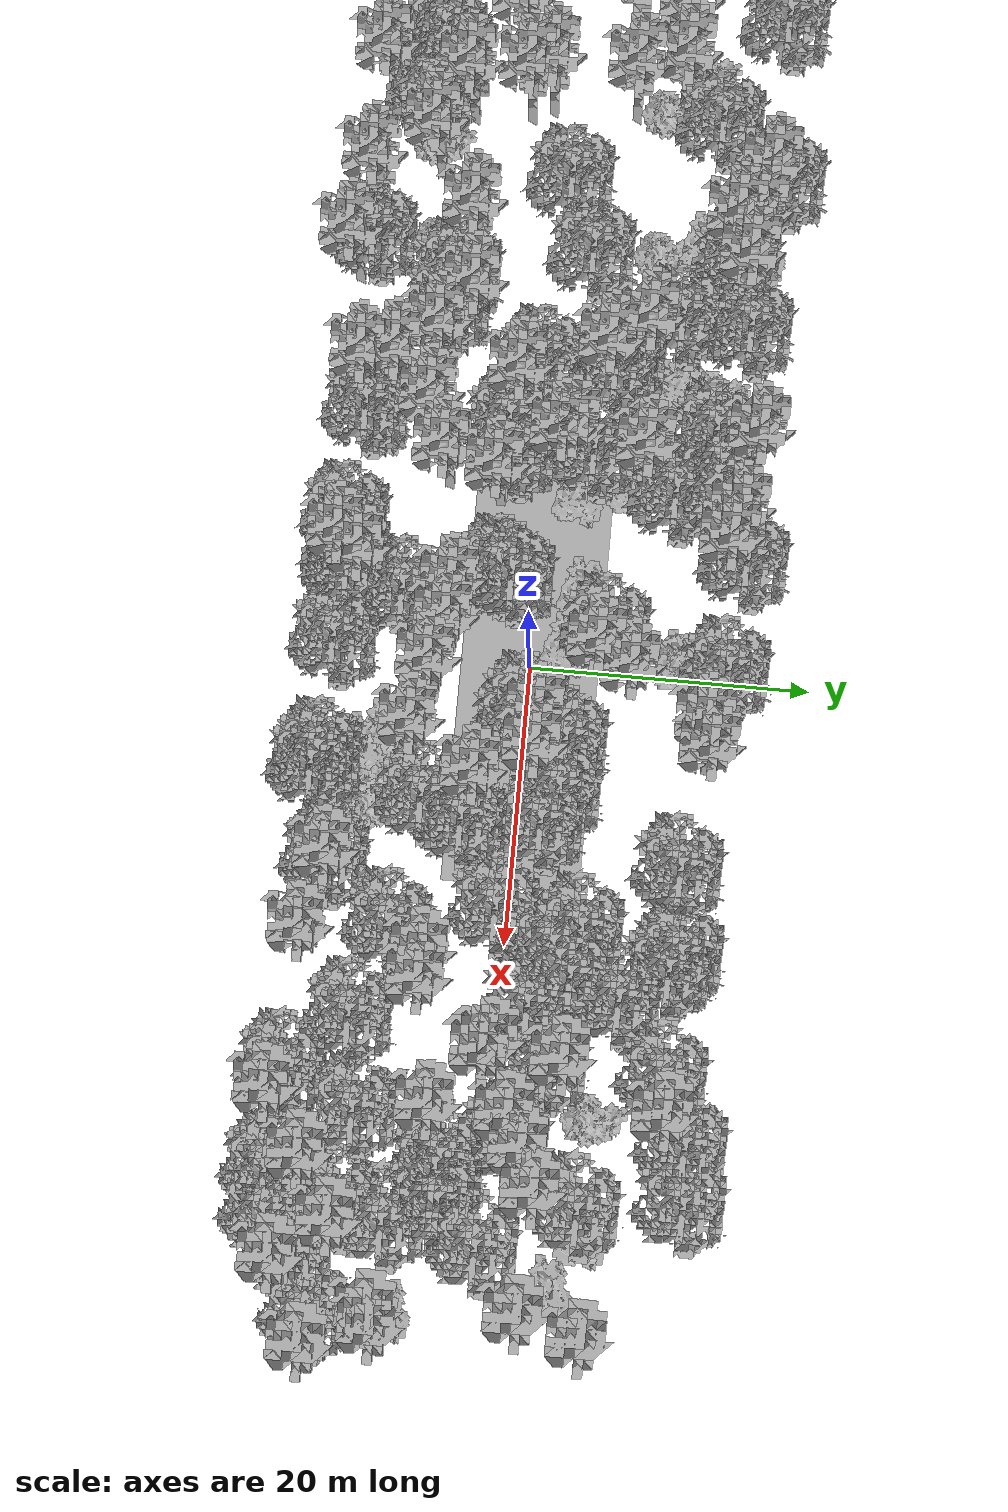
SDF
<sdf version="1.7">
    <world name="default">
        <plugin name="mrs_gazebo_static_transform_republisher_plugin" filename="libMrsGazeboCommonResources_StaticTransformRepublisher.so"/>
        <spherical_coordinates>
            <surface_model>EARTH_WGS84</surface_model>
            <latitude_deg>47.3977</latitude_deg>
            <longitude_deg>8.54559</longitude_deg>
            <elevation>0</elevation>
            <heading_deg>0</heading_deg>
        </spherical_coordinates>
        <physics name="default_physics" default="0" type="ode">
            <ode>
                <solver>
                    <type>quick</type>
                    <iters>10</iters>
                    <sor>1.3</sor>
                    <use_dynamic_moi_rescaling>0</use_dynamic_moi_rescaling>
                </solver>
                <constraints>
                    <cfm>0</cfm>
                    <erp>0.2</erp>
                    <contact_max_correcting_vel>1000</contact_max_correcting_vel>
                    <contact_surface_layer>0.001</contact_surface_layer>
                </constraints>
            </ode>
            <max_step_size>0.004</max_step_size>
            <real_time_factor>1</real_time_factor>
            <real_time_update_rate>250</real_time_update_rate>
        </physics>
        <scene>
            <shadows>0</shadows>
            <ambient>0.4 0.4 0.4 1</ambient>
            <background>0.7 0.7 0.7 1</background>
        </scene>
        <light name="sun" type="directional">
            <pose>0 0 1000 0.4 0.2 0</pose>
            <diffuse>1 1 1 1</diffuse>
            <specular>0.6 0.6 0.6 1</specular>
            <direction>0.1 0.1 -0.9</direction>
            <attenuation>
                <range>20</range>
                <constant>0.5</constant>
                <linear>0.01</linear>
                <quadratic>0.001</quadratic>
            </attenuation>
            <cast_shadows>1</cast_shadows>
            <spot>
                <inner_angle>0</inner_angle>
                <outer_angle>0</outer_angle>
                <falloff>0</falloff>
            </spot>
        </light>
        <model name="ground_plane">
            <static>1</static>
            <link name="link">
                <collision name="collision">
                    <pose>-50 0 0 0 -0 0</pose>
                    <geometry>
                        <plane>
                            <normal>0 0 1</normal>
                            <size>100 100</size>
                        </plane>
                    </geometry>
                    <surface>
                        <contact>
                            <ode>
                                <min_depth>0.01</min_depth>
                                <max_vel>0</max_vel>
                            </ode>
                        </contact>
                        <friction>
                            <ode/>
                            <torsional>
                                <ode/>
                            </torsional>
                        </friction>
                        <bounce/>
                    </surface>
                    <max_contacts>10</max_contacts>
                </collision>
                <visual name="grass">
                    <pose>0 0 0 0 -0 0</pose>
                    <cast_shadows>0</cast_shadows>
                    <geometry>
                        <mesh>
                            <scale>0.5814285714285714 0.18142857142857144 0.1</scale>
                            <uri>file://grass_plane/meshes/grass_plane.dae</uri>
                        </mesh>
                    </geometry>
                </visual>
                <self_collide>0</self_collide>
                <enable_wind>0</enable_wind>
                <kinematic>0</kinematic>
            </link>
        </model>
        <model name="the_void">
            <static>1</static>
            <link name="link">
                <pose>0 0 0.1 0 -0 0</pose>
                <visual name="the_void">
                    <pose>0 0 2 0 -0 0</pose>
                    <geometry>
                        <sphere>
                            <radius>0.25</radius>
                        </sphere>
                    </geometry>
                    <material>
                        <script>
                            <uri>file://media/materials/scripts/Gazebo.material</uri>
                            <name>Gazebo/Black</name>
                        </script>
                    </material>
                </visual>
                <self_collide>0</self_collide>
                <enable_wind>0</enable_wind>
                <kinematic>0</kinematic>
            </link>
            <pose>-1000 -1000 0 0 -0 0</pose>
        </model>
        <gui fullscreen="0">
            <camera name="camera">
                <pose>35.1577 98.6044 40.0204 0 0.407996 -1.99761</pose>
                <view_controller>orbit</view_controller>
                <projection_type>perspective</projection_type>
            </camera>
        </gui>
        <plugin name="mrs_gazebo_rviz_cam_synchronizer" filename="libMrsGazeboCommonResources_RvizCameraSynchronizer.so">
            <target_frame_id>gazebo_user_camera</target_frame_id>
            <world_origin_frame_id>uav1/gps_origin</world_origin_frame_id>
            <frame_to_follow>uav1</frame_to_follow>
        </plugin>
        <gravity>0 0 -9.8066</gravity>
        <magnetic_field>6e-06 2.3e-05 -4.2e-05</magnetic_field>
        <atmosphere type="adiabatic"/>
        <wind/>
        <model name="Tree 0">
            <static>1</static>
            <pose>46.44234237809738 -10.756084124833425 0 1.57079 -0 0</pose>
            <link name="link">
                <pose>0 0 0 0 -0 0</pose>
                <collision name="collision">
                    <geometry>
                        <mesh>
                            <scale>3.5 5 3.5</scale>
                            <uri>model://tree_2/meshes/tree_2.obj</uri>
                        </mesh>
                    </geometry>
                    <max_contacts>10</max_contacts>
                    <surface>
                        <contact>
                            <ode/>
                        </contact>
                        <bounce/>
                        <friction>
                            <torsional>
                                <ode/>
                            </torsional>
                            <ode/>
                        </friction>
                    </surface>
                </collision>
                <visual name="visual">
                    <geometry>
                        <mesh>
                            <scale>3.5 5 3.5</scale>
                            <uri>model://tree_2/meshes/tree_2.obj</uri>
                        </mesh>
                    </geometry>
                </visual>
                <self_collide>0</self_collide>
                <enable_wind>0</enable_wind>
                <kinematic>0</kinematic>
            </link>
        </model>
        <model name="Tree 1">
            <static>1</static>
            <pose>-31.017285858310263 6.9304984635334606 0 1.57079 -0 0</pose>
            <link name="link">
                <pose>0 0 0 0 -0 0</pose>
                <collision name="collision">
                    <geometry>
                        <mesh>
                            <scale>4 2.5 4</scale>
                            <uri>model://tree_1/meshes/tree_1.obj</uri>
                        </mesh>
                    </geometry>
                    <max_contacts>10</max_contacts>
                    <surface>
                        <contact>
                            <ode/>
                        </contact>
                        <bounce/>
                        <friction>
                            <torsional>
                                <ode/>
                            </torsional>
                            <ode/>
                        </friction>
                    </surface>
                </collision>
                <visual name="visual">
                    <geometry>
                        <mesh>
                            <scale>4 2.5 4</scale>
                            <uri>model://tree_1/meshes/tree_1.obj</uri>
                        </mesh>
                    </geometry>
                </visual>
                <self_collide>0</self_collide>
                <enable_wind>0</enable_wind>
                <kinematic>0</kinematic>
            </link>
        </model>
        <model name="Tree 2">
            <static>1</static>
            <pose>-24.036398271626272 -7.637599285313509 0 1.57079 -0 0</pose>
            <link name="link">
                <pose>0 0 0 0 -0 0</pose>
                <collision name="collision">
                    <geometry>
                        <mesh>
                            <scale>3.5 5 3.5</scale>
                            <uri>model://tree_2/meshes/tree_2.obj</uri>
                        </mesh>
                    </geometry>
                    <max_contacts>10</max_contacts>
                    <surface>
                        <contact>
                            <ode/>
                        </contact>
                        <bounce/>
                        <friction>
                            <torsional>
                                <ode/>
                            </torsional>
                            <ode/>
                        </friction>
                    </surface>
                </collision>
                <visual name="visual">
                    <geometry>
                        <mesh>
                            <scale>3.5 5 3.5</scale>
                            <uri>model://tree_2/meshes/tree_2.obj</uri>
                        </mesh>
                    </geometry>
                </visual>
                <self_collide>0</self_collide>
                <enable_wind>0</enable_wind>
                <kinematic>0</kinematic>
            </link>
        </model>
        <model name="Tree 3">
            <static>1</static>
            <pose>26.230850330044063 -9.717977953429486 0 1.57079 -0 0</pose>
            <link name="link">
                <pose>0 0 0 0 -0 0</pose>
                <collision name="collision">
                    <geometry>
                        <mesh>
                            <scale>3.5 5 3.5</scale>
                            <uri>model://tree_2/meshes/tree_2.obj</uri>
                        </mesh>
                    </geometry>
                    <max_contacts>10</max_contacts>
                    <surface>
                        <contact>
                            <ode/>
                        </contact>
                        <bounce/>
                        <friction>
                            <torsional>
                                <ode/>
                            </torsional>
                            <ode/>
                        </friction>
                    </surface>
                </collision>
                <visual name="visual">
                    <geometry>
                        <mesh>
                            <scale>3.5 5 3.5</scale>
                            <uri>model://tree_2/meshes/tree_2.obj</uri>
                        </mesh>
                    </geometry>
                </visual>
                <self_collide>0</self_collide>
                <enable_wind>0</enable_wind>
                <kinematic>0</kinematic>
            </link>
        </model>
        <model name="Tree 4">
            <static>1</static>
            <pose>46.77839195121835 -6.231885729458671 0 1.57079 -0 0</pose>
            <link name="link">
                <pose>0 0 0 0 -0 0</pose>
                <collision name="collision">
                    <geometry>
                        <mesh>
                            <scale>3.5 5 3.5</scale>
                            <uri>model://tree_9/meshes/tree_9.obj</uri>
                        </mesh>
                    </geometry>
                    <max_contacts>10</max_contacts>
                    <surface>
                        <contact>
                            <ode/>
                        </contact>
                        <bounce/>
                        <friction>
                            <torsional>
                                <ode/>
                            </torsional>
                            <ode/>
                        </friction>
                    </surface>
                </collision>
                <visual name="visual">
                    <geometry>
                        <mesh>
                            <scale>3.5 5 3.5</scale>
                            <uri>model://tree_9/meshes/tree_9.obj</uri>
                        </mesh>
                    </geometry>
                </visual>
                <self_collide>0</self_collide>
                <enable_wind>0</enable_wind>
                <kinematic>0</kinematic>
            </link>
        </model>
        <model name="Tree 5">
            <static>1</static>
            <pose>43.62478168935962 4.813290201069382 0 1.57079 -0 0</pose>
            <link name="link">
                <pose>0 0 0 0 -0 0</pose>
                <collision name="collision">
                    <geometry>
                        <mesh>
                            <scale>3 2 3</scale>
                            <uri>model://tree_3/meshes/tree_3.obj</uri>
                        </mesh>
                    </geometry>
                    <max_contacts>10</max_contacts>
                    <surface>
                        <contact>
                            <ode/>
                        </contact>
                        <bounce/>
                        <friction>
                            <torsional>
                                <ode/>
                            </torsional>
                            <ode/>
                        </friction>
                    </surface>
                </collision>
                <visual name="visual">
                    <geometry>
                        <mesh>
                            <scale>3 2 3</scale>
                            <uri>model://tree_3/meshes/tree_3.obj</uri>
                        </mesh>
                    </geometry>
                </visual>
                <self_collide>0</self_collide>
                <enable_wind>0</enable_wind>
                <kinematic>0</kinematic>
            </link>
        </model>
        <model name="Tree 6">
            <static>1</static>
            <pose>12.257597133794576 -3.4394781878889944 0 1.57079 -0 0</pose>
            <link name="link">
                <pose>0 0 0 0 -0 0</pose>
                <collision name="collision">
                    <geometry>
                        <mesh>
                            <scale>3.5 5 3.5</scale>
                            <uri>model://tree_2/meshes/tree_2.obj</uri>
                        </mesh>
                    </geometry>
                    <max_contacts>10</max_contacts>
                    <surface>
                        <contact>
                            <ode/>
                        </contact>
                        <bounce/>
                        <friction>
                            <torsional>
                                <ode/>
                            </torsional>
                            <ode/>
                        </friction>
                    </surface>
                </collision>
                <visual name="visual">
                    <geometry>
                        <mesh>
                            <scale>3.5 5 3.5</scale>
                            <uri>model://tree_2/meshes/tree_2.obj</uri>
                        </mesh>
                    </geometry>
                </visual>
                <self_collide>0</self_collide>
                <enable_wind>0</enable_wind>
                <kinematic>0</kinematic>
            </link>
        </model>
        <model name="Tree 7">
            <static>1</static>
            <pose>-13.908793462417066 -2.199686056153894 0 1.57079 -0 0</pose>
            <link name="link">
                <pose>0 0 0 0 -0 0</pose>
                <collision name="collision">
                    <geometry>
                        <mesh>
                            <scale>3.5 5 3.5</scale>
                            <uri>model://tree_2/meshes/tree_2.obj</uri>
                        </mesh>
                    </geometry>
                    <max_contacts>10</max_contacts>
                    <surface>
                        <contact>
                            <ode/>
                        </contact>
                        <bounce/>
                        <friction>
                            <torsional>
                                <ode/>
                            </torsional>
                            <ode/>
                        </friction>
                    </surface>
                </collision>
                <visual name="visual">
                    <geometry>
                        <mesh>
                            <scale>3.5 5 3.5</scale>
                            <uri>model://tree_2/meshes/tree_2.obj</uri>
                        </mesh>
                    </geometry>
                </visual>
                <self_collide>0</self_collide>
                <enable_wind>0</enable_wind>
                <kinematic>0</kinematic>
            </link>
        </model>
        <model name="Tree 8">
            <static>1</static>
            <pose>39.88170658094448 -6.213259696053058 0 1.57079 -0 0</pose>
            <link name="link">
                <pose>0 0 0 0 -0 0</pose>
                <collision name="collision">
                    <geometry>
                        <mesh>
                            <scale>3.5 5 3.5</scale>
                            <uri>model://tree_2/meshes/tree_2.obj</uri>
                        </mesh>
                    </geometry>
                    <max_contacts>10</max_contacts>
                    <surface>
                        <contact>
                            <ode/>
                        </contact>
                        <bounce/>
                        <friction>
                            <torsional>
                                <ode/>
                            </torsional>
                            <ode/>
                        </friction>
                    </surface>
                </collision>
                <visual name="visual">
                    <geometry>
                        <mesh>
                            <scale>3.5 5 3.5</scale>
                            <uri>model://tree_2/meshes/tree_2.obj</uri>
                        </mesh>
                    </geometry>
                </visual>
                <self_collide>0</self_collide>
                <enable_wind>0</enable_wind>
                <kinematic>0</kinematic>
            </link>
        </model>
        <model name="Tree 9">
            <static>1</static>
            <pose>-45.899195435918614 -4.327483313472856 0 1.57079 -0 0</pose>
            <link name="link">
                <pose>0 0 0 0 -0 0</pose>
                <collision name="collision">
                    <geometry>
                        <mesh>
                            <scale>3.5 5 3.5</scale>
                            <uri>model://tree_9/meshes/tree_9.obj</uri>
                        </mesh>
                    </geometry>
                    <max_contacts>10</max_contacts>
                    <surface>
                        <contact>
                            <ode/>
                        </contact>
                        <bounce/>
                        <friction>
                            <torsional>
                                <ode/>
                            </torsional>
                            <ode/>
                        </friction>
                    </surface>
                </collision>
                <visual name="visual">
                    <geometry>
                        <mesh>
                            <scale>3.5 5 3.5</scale>
                            <uri>model://tree_9/meshes/tree_9.obj</uri>
                        </mesh>
                    </geometry>
                </visual>
                <self_collide>0</self_collide>
                <enable_wind>0</enable_wind>
                <kinematic>0</kinematic>
            </link>
        </model>
        <model name="Tree 10">
            <static>1</static>
            <pose>-1.5145191692231847 10.884960249035881 0 1.57079 -0 0</pose>
            <link name="link">
                <pose>0 0 0 0 -0 0</pose>
                <collision name="collision">
                    <geometry>
                        <mesh>
                            <scale>4 2.5 4</scale>
                            <uri>model://tree_1/meshes/tree_1.obj</uri>
                        </mesh>
                    </geometry>
                    <max_contacts>10</max_contacts>
                    <surface>
                        <contact>
                            <ode/>
                        </contact>
                        <bounce/>
                        <friction>
                            <torsional>
                                <ode/>
                            </torsional>
                            <ode/>
                        </friction>
                    </surface>
                </collision>
                <visual name="visual">
                    <geometry>
                        <mesh>
                            <scale>4 2.5 4</scale>
                            <uri>model://tree_1/meshes/tree_1.obj</uri>
                        </mesh>
                    </geometry>
                </visual>
                <self_collide>0</self_collide>
                <enable_wind>0</enable_wind>
                <kinematic>0</kinematic>
            </link>
        </model>
        <model name="Tree 11">
            <static>1</static>
            <pose>-21.812975868504175 -8.057135958250296 0 1.57079 -0 0</pose>
            <link name="link">
                <pose>0 0 0 0 -0 0</pose>
                <collision name="collision">
                    <geometry>
                        <mesh>
                            <scale>3.5 5 3.5</scale>
                            <uri>model://tree_9/meshes/tree_9.obj</uri>
                        </mesh>
                    </geometry>
                    <max_contacts>10</max_contacts>
                    <surface>
                        <contact>
                            <ode/>
                        </contact>
                        <bounce/>
                        <friction>
                            <torsional>
                                <ode/>
                            </torsional>
                            <ode/>
                        </friction>
                    </surface>
                </collision>
                <visual name="visual">
                    <geometry>
                        <mesh>
                            <scale>3.5 5 3.5</scale>
                            <uri>model://tree_9/meshes/tree_9.obj</uri>
                        </mesh>
                    </geometry>
                </visual>
                <self_collide>0</self_collide>
                <enable_wind>0</enable_wind>
                <kinematic>0</kinematic>
            </link>
        </model>
        <model name="Tree 12">
            <static>1</static>
            <pose>-16.13570186410201 -12.644520403151208 0 1.57079 -0 0</pose>
            <link name="link">
                <pose>0 0 0 0 -0 0</pose>
                <collision name="collision">
                    <geometry>
                        <mesh>
                            <scale>3.5 5 3.5</scale>
                            <uri>model://tree_2/meshes/tree_2.obj</uri>
                        </mesh>
                    </geometry>
                    <max_contacts>10</max_contacts>
                    <surface>
                        <contact>
                            <ode/>
                        </contact>
                        <bounce/>
                        <friction>
                            <torsional>
                                <ode/>
                            </torsional>
                            <ode/>
                        </friction>
                    </surface>
                </collision>
                <visual name="visual">
                    <geometry>
                        <mesh>
                            <scale>3.5 5 3.5</scale>
                            <uri>model://tree_2/meshes/tree_2.obj</uri>
                        </mesh>
                    </geometry>
                </visual>
                <self_collide>0</self_collide>
                <enable_wind>0</enable_wind>
                <kinematic>0</kinematic>
            </link>
        </model>
        <model name="Tree 13">
            <static>1</static>
            <pose>45.245463994499914 3.2660481772489938 0 1.57079 -0 0</pose>
            <link name="link">
                <pose>0 0 0 0 -0 0</pose>
                <collision name="collision">
                    <geometry>
                        <mesh>
                            <scale>3.5 5 3.5</scale>
                            <uri>model://tree_9/meshes/tree_9.obj</uri>
                        </mesh>
                    </geometry>
                    <max_contacts>10</max_contacts>
                    <surface>
                        <contact>
                            <ode/>
                        </contact>
                        <bounce/>
                        <friction>
                            <torsional>
                                <ode/>
                            </torsional>
                            <ode/>
                        </friction>
                    </surface>
                </collision>
                <visual name="visual">
                    <geometry>
                        <mesh>
                            <scale>3.5 5 3.5</scale>
                            <uri>model://tree_9/meshes/tree_9.obj</uri>
                        </mesh>
                    </geometry>
                </visual>
                <self_collide>0</self_collide>
                <enable_wind>0</enable_wind>
                <kinematic>0</kinematic>
            </link>
        </model>
        <model name="Tree 14">
            <static>1</static>
            <pose>-42.7610196851699 -9.306988958430832 0 1.57079 -0 0</pose>
            <link name="link">
                <pose>0 0 0 0 -0 0</pose>
                <collision name="collision">
                    <geometry>
                        <mesh>
                            <scale>3.5 5 3.5</scale>
                            <uri>model://tree_2/meshes/tree_2.obj</uri>
                        </mesh>
                    </geometry>
                    <max_contacts>10</max_contacts>
                    <surface>
                        <contact>
                            <ode/>
                        </contact>
                        <bounce/>
                        <friction>
                            <torsional>
                                <ode/>
                            </torsional>
                            <ode/>
                        </friction>
                    </surface>
                </collision>
                <visual name="visual">
                    <geometry>
                        <mesh>
                            <scale>3.5 5 3.5</scale>
                            <uri>model://tree_2/meshes/tree_2.obj</uri>
                        </mesh>
                    </geometry>
                </visual>
                <self_collide>0</self_collide>
                <enable_wind>0</enable_wind>
                <kinematic>0</kinematic>
            </link>
        </model>
        <model name="Tree 15">
            <static>1</static>
            <pose>-48.23645949559417 3.5121281507048963 0 1.57079 -0 0</pose>
            <link name="link">
                <pose>0 0 0 0 -0 0</pose>
                <collision name="collision">
                    <geometry>
                        <mesh>
                            <scale>3.5 5 3.5</scale>
                            <uri>model://tree_9/meshes/tree_9.obj</uri>
                        </mesh>
                    </geometry>
                    <max_contacts>10</max_contacts>
                    <surface>
                        <contact>
                            <ode/>
                        </contact>
                        <bounce/>
                        <friction>
                            <torsional>
                                <ode/>
                            </torsional>
                            <ode/>
                        </friction>
                    </surface>
                </collision>
                <visual name="visual">
                    <geometry>
                        <mesh>
                            <scale>3.5 5 3.5</scale>
                            <uri>model://tree_9/meshes/tree_9.obj</uri>
                        </mesh>
                    </geometry>
                </visual>
                <self_collide>0</self_collide>
                <enable_wind>0</enable_wind>
                <kinematic>0</kinematic>
            </link>
        </model>
        <model name="Tree 16">
            <static>1</static>
            <pose>46.46912115306617 7.537182974908205 0 1.57079 -0 0</pose>
            <link name="link">
                <pose>0 0 0 0 -0 0</pose>
                <collision name="collision">
                    <geometry>
                        <mesh>
                            <scale>3.5 5 3.5</scale>
                            <uri>model://tree_9/meshes/tree_9.obj</uri>
                        </mesh>
                    </geometry>
                    <max_contacts>10</max_contacts>
                    <surface>
                        <contact>
                            <ode/>
                        </contact>
                        <bounce/>
                        <friction>
                            <torsional>
                                <ode/>
                            </torsional>
                            <ode/>
                        </friction>
                    </surface>
                </collision>
                <visual name="visual">
                    <geometry>
                        <mesh>
                            <scale>3.5 5 3.5</scale>
                            <uri>model://tree_9/meshes/tree_9.obj</uri>
                        </mesh>
                    </geometry>
                </visual>
                <self_collide>0</self_collide>
                <enable_wind>0</enable_wind>
                <kinematic>0</kinematic>
            </link>
        </model>
        <model name="Tree 17">
            <static>1</static>
            <pose>12.033492077888852 1.9867467809147676 0 1.57079 -0 0</pose>
            <link name="link">
                <pose>0 0 0 0 -0 0</pose>
                <collision name="collision">
                    <geometry>
                        <mesh>
                            <scale>3.5 5 3.5</scale>
                            <uri>model://tree_2/meshes/tree_2.obj</uri>
                        </mesh>
                    </geometry>
                    <max_contacts>10</max_contacts>
                    <surface>
                        <contact>
                            <ode/>
                        </contact>
                        <bounce/>
                        <friction>
                            <torsional>
                                <ode/>
                            </torsional>
                            <ode/>
                        </friction>
                    </surface>
                </collision>
                <visual name="visual">
                    <geometry>
                        <mesh>
                            <scale>3.5 5 3.5</scale>
                            <uri>model://tree_2/meshes/tree_2.obj</uri>
                        </mesh>
                    </geometry>
                </visual>
                <self_collide>0</self_collide>
                <enable_wind>0</enable_wind>
                <kinematic>0</kinematic>
            </link>
        </model>
        <model name="Tree 18">
            <static>1</static>
            <pose>-12.638492599856498 2.162255533944254 0 1.57079 -0 0</pose>
            <link name="link">
                <pose>0 0 0 0 -0 0</pose>
                <collision name="collision">
                    <geometry>
                        <mesh>
                            <scale>3 2 3</scale>
                            <uri>model://tree_3/meshes/tree_3.obj</uri>
                        </mesh>
                    </geometry>
                    <max_contacts>10</max_contacts>
                    <surface>
                        <contact>
                            <ode/>
                        </contact>
                        <bounce/>
                        <friction>
                            <torsional>
                                <ode/>
                            </torsional>
                            <ode/>
                        </friction>
                    </surface>
                </collision>
                <visual name="visual">
                    <geometry>
                        <mesh>
                            <scale>3 2 3</scale>
                            <uri>model://tree_3/meshes/tree_3.obj</uri>
                        </mesh>
                    </geometry>
                </visual>
                <self_collide>0</self_collide>
                <enable_wind>0</enable_wind>
                <kinematic>0</kinematic>
            </link>
        </model>
        <model name="Tree 19">
            <static>1</static>
            <pose>45.95892816855037 -6.172525978426117 0 1.57079 -0 0</pose>
            <link name="link">
                <pose>0 0 0 0 -0 0</pose>
                <collision name="collision">
                    <geometry>
                        <mesh>
                            <scale>3 2 3</scale>
                            <uri>model://tree_3/meshes/tree_3.obj</uri>
                        </mesh>
                    </geometry>
                    <max_contacts>10</max_contacts>
                    <surface>
                        <contact>
                            <ode/>
                        </contact>
                        <bounce/>
                        <friction>
                            <torsional>
                                <ode/>
                            </torsional>
                            <ode/>
                        </friction>
                    </surface>
                </collision>
                <visual name="visual">
                    <geometry>
                        <mesh>
                            <scale>3 2 3</scale>
                            <uri>model://tree_3/meshes/tree_3.obj</uri>
                        </mesh>
                    </geometry>
                </visual>
                <self_collide>0</self_collide>
                <enable_wind>0</enable_wind>
                <kinematic>0</kinematic>
            </link>
        </model>
        <model name="Tree 20">
            <static>1</static>
            <pose>20.278932603489096 12.200697511291253 0 1.57079 -0 0</pose>
            <link name="link">
                <pose>0 0 0 0 -0 0</pose>
                <collision name="collision">
                    <geometry>
                        <mesh>
                            <scale>3.5 5 3.5</scale>
                            <uri>model://tree_2/meshes/tree_2.obj</uri>
                        </mesh>
                    </geometry>
                    <max_contacts>10</max_contacts>
                    <surface>
                        <contact>
                            <ode/>
                        </contact>
                        <bounce/>
                        <friction>
                            <torsional>
                                <ode/>
                            </torsional>
                            <ode/>
                        </friction>
                    </surface>
                </collision>
                <visual name="visual">
                    <geometry>
                        <mesh>
                            <scale>3.5 5 3.5</scale>
                            <uri>model://tree_2/meshes/tree_2.obj</uri>
                        </mesh>
                    </geometry>
                </visual>
                <self_collide>0</self_collide>
                <enable_wind>0</enable_wind>
                <kinematic>0</kinematic>
            </link>
        </model>
        <model name="Tree 21">
            <static>1</static>
            <pose>10.91396890119536 -6.259870758829594 0 1.57079 -0 0</pose>
            <link name="link">
                <pose>0 0 0 0 -0 0</pose>
                <collision name="collision">
                    <geometry>
                        <mesh>
                            <scale>3.5 5 3.5</scale>
                            <uri>model://tree_2/meshes/tree_2.obj</uri>
                        </mesh>
                    </geometry>
                    <max_contacts>10</max_contacts>
                    <surface>
                        <contact>
                            <ode/>
                        </contact>
                        <bounce/>
                        <friction>
                            <torsional>
                                <ode/>
                            </torsional>
                            <ode/>
                        </friction>
                    </surface>
                </collision>
                <visual name="visual">
                    <geometry>
                        <mesh>
                            <scale>3.5 5 3.5</scale>
                            <uri>model://tree_2/meshes/tree_2.obj</uri>
                        </mesh>
                    </geometry>
                </visual>
                <self_collide>0</self_collide>
                <enable_wind>0</enable_wind>
                <kinematic>0</kinematic>
            </link>
        </model>
        <model name="Tree 22">
            <static>1</static>
            <pose>-42.68242296811453 7.53280757684221 0 1.57079 -0 0</pose>
            <link name="link">
                <pose>0 0 0 0 -0 0</pose>
                <collision name="collision">
                    <geometry>
                        <mesh>
                            <scale>3.5 5 3.5</scale>
                            <uri>model://tree_9/meshes/tree_9.obj</uri>
                        </mesh>
                    </geometry>
                    <max_contacts>10</max_contacts>
                    <surface>
                        <contact>
                            <ode/>
                        </contact>
                        <bounce/>
                        <friction>
                            <torsional>
                                <ode/>
                            </torsional>
                            <ode/>
                        </friction>
                    </surface>
                </collision>
                <visual name="visual">
                    <geometry>
                        <mesh>
                            <scale>3.5 5 3.5</scale>
                            <uri>model://tree_9/meshes/tree_9.obj</uri>
                        </mesh>
                    </geometry>
                </visual>
                <self_collide>0</self_collide>
                <enable_wind>0</enable_wind>
                <kinematic>0</kinematic>
            </link>
        </model>
        <model name="Tree 23">
            <static>1</static>
            <pose>-5.414956104736845 -2.4101769137004805 0 1.57079 -0 0</pose>
            <link name="link">
                <pose>0 0 0 0 -0 0</pose>
                <collision name="collision">
                    <geometry>
                        <mesh>
                            <scale>3.5 5 3.5</scale>
                            <uri>model://tree_2/meshes/tree_2.obj</uri>
                        </mesh>
                    </geometry>
                    <max_contacts>10</max_contacts>
                    <surface>
                        <contact>
                            <ode/>
                        </contact>
                        <bounce/>
                        <friction>
                            <torsional>
                                <ode/>
                            </torsional>
                            <ode/>
                        </friction>
                    </surface>
                </collision>
                <visual name="visual">
                    <geometry>
                        <mesh>
                            <scale>3.5 5 3.5</scale>
                            <uri>model://tree_2/meshes/tree_2.obj</uri>
                        </mesh>
                    </geometry>
                </visual>
                <self_collide>0</self_collide>
                <enable_wind>0</enable_wind>
                <kinematic>0</kinematic>
            </link>
        </model>
        <model name="Tree 24">
            <static>1</static>
            <pose>-23.02265946576647 -1.7180948324284238 0 1.57079 -0 0</pose>
            <link name="link">
                <pose>0 0 0 0 -0 0</pose>
                <collision name="collision">
                    <geometry>
                        <mesh>
                            <scale>3 2 3</scale>
                            <uri>model://tree_3/meshes/tree_3.obj</uri>
                        </mesh>
                    </geometry>
                    <max_contacts>10</max_contacts>
                    <surface>
                        <contact>
                            <ode/>
                        </contact>
                        <bounce/>
                        <friction>
                            <torsional>
                                <ode/>
                            </torsional>
                            <ode/>
                        </friction>
                    </surface>
                </collision>
                <visual name="visual">
                    <geometry>
                        <mesh>
                            <scale>3 2 3</scale>
                            <uri>model://tree_3/meshes/tree_3.obj</uri>
                        </mesh>
                    </geometry>
                </visual>
                <self_collide>0</self_collide>
                <enable_wind>0</enable_wind>
                <kinematic>0</kinematic>
            </link>
        </model>
        <model name="Tree 25">
            <static>1</static>
            <pose>-13.55741859512898 6.050680133643091 0 1.57079 -0 0</pose>
            <link name="link">
                <pose>0 0 0 0 -0 0</pose>
                <collision name="collision">
                    <geometry>
                        <mesh>
                            <scale>3 2 3</scale>
                            <uri>model://tree_3/meshes/tree_3.obj</uri>
                        </mesh>
                    </geometry>
                    <max_contacts>10</max_contacts>
                    <surface>
                        <contact>
                            <ode/>
                        </contact>
                        <bounce/>
                        <friction>
                            <torsional>
                                <ode/>
                            </torsional>
                            <ode/>
                        </friction>
                    </surface>
                </collision>
                <visual name="visual">
                    <geometry>
                        <mesh>
                            <scale>3 2 3</scale>
                            <uri>model://tree_3/meshes/tree_3.obj</uri>
                        </mesh>
                    </geometry>
                </visual>
                <self_collide>0</self_collide>
                <enable_wind>0</enable_wind>
                <kinematic>0</kinematic>
            </link>
        </model>
        <model name="Tree 26">
            <static>1</static>
            <pose>-16.36699653730335 11.6769706178248 0 1.57079 -0 0</pose>
            <link name="link">
                <pose>0 0 0 0 -0 0</pose>
                <collision name="collision">
                    <geometry>
                        <mesh>
                            <scale>3.5 5 3.5</scale>
                            <uri>model://tree_2/meshes/tree_2.obj</uri>
                        </mesh>
                    </geometry>
                    <max_contacts>10</max_contacts>
                    <surface>
                        <contact>
                            <ode/>
                        </contact>
                        <bounce/>
                        <friction>
                            <torsional>
                                <ode/>
                            </torsional>
                            <ode/>
                        </friction>
                    </surface>
                </collision>
                <visual name="visual">
                    <geometry>
                        <mesh>
                            <scale>3.5 5 3.5</scale>
                            <uri>model://tree_2/meshes/tree_2.obj</uri>
                        </mesh>
                    </geometry>
                </visual>
                <self_collide>0</self_collide>
                <enable_wind>0</enable_wind>
                <kinematic>0</kinematic>
            </link>
        </model>
        <model name="Tree 27">
            <static>1</static>
            <pose>-15.021074206600922 1.051469061175606 0 1.57079 -0 0</pose>
            <link name="link">
                <pose>0 0 0 0 -0 0</pose>
                <collision name="collision">
                    <geometry>
                        <mesh>
                            <scale>3.5 5 3.5</scale>
                            <uri>model://tree_9/meshes/tree_9.obj</uri>
                        </mesh>
                    </geometry>
                    <max_contacts>10</max_contacts>
                    <surface>
                        <contact>
                            <ode/>
                        </contact>
                        <bounce/>
                        <friction>
                            <torsional>
                                <ode/>
                            </torsional>
                            <ode/>
                        </friction>
                    </surface>
                </collision>
                <visual name="visual">
                    <geometry>
                        <mesh>
                            <scale>3.5 5 3.5</scale>
                            <uri>model://tree_9/meshes/tree_9.obj</uri>
                        </mesh>
                    </geometry>
                </visual>
                <self_collide>0</self_collide>
                <enable_wind>0</enable_wind>
                <kinematic>0</kinematic>
            </link>
        </model>
        <model name="Tree 28">
            <static>1</static>
            <pose>5.483641039165377 -0.23342204951496015 0 1.57079 -0 0</pose>
            <link name="link">
                <pose>0 0 0 0 -0 0</pose>
                <collision name="collision">
                    <geometry>
                        <mesh>
                            <scale>3.5 5 3.5</scale>
                            <uri>model://tree_2/meshes/tree_2.obj</uri>
                        </mesh>
                    </geometry>
                    <max_contacts>10</max_contacts>
                    <surface>
                        <contact>
                            <ode/>
                        </contact>
                        <bounce/>
                        <friction>
                            <torsional>
                                <ode/>
                            </torsional>
                            <ode/>
                        </friction>
                    </surface>
                </collision>
                <visual name="visual">
                    <geometry>
                        <mesh>
                            <scale>3.5 5 3.5</scale>
                            <uri>model://tree_2/meshes/tree_2.obj</uri>
                        </mesh>
                    </geometry>
                </visual>
                <self_collide>0</self_collide>
                <enable_wind>0</enable_wind>
                <kinematic>0</kinematic>
            </link>
        </model>
        <model name="Tree 29">
            <static>1</static>
            <pose>35.246683009240556 -2.729741963374302 0 1.57079 -0 0</pose>
            <link name="link">
                <pose>0 0 0 0 -0 0</pose>
                <collision name="collision">
                    <geometry>
                        <mesh>
                            <scale>3.5 5 3.5</scale>
                            <uri>model://tree_2/meshes/tree_2.obj</uri>
                        </mesh>
                    </geometry>
                    <max_contacts>10</max_contacts>
                    <surface>
                        <contact>
                            <ode/>
                        </contact>
                        <bounce/>
                        <friction>
                            <torsional>
                                <ode/>
                            </torsional>
                            <ode/>
                        </friction>
                    </surface>
                </collision>
                <visual name="visual">
                    <geometry>
                        <mesh>
                            <scale>3.5 5 3.5</scale>
                            <uri>model://tree_2/meshes/tree_2.obj</uri>
                        </mesh>
                    </geometry>
                </visual>
                <self_collide>0</self_collide>
                <enable_wind>0</enable_wind>
                <kinematic>0</kinematic>
            </link>
        </model>
        <model name="Tree 30">
            <static>1</static>
            <pose>5.7039060267208725 -10.096312875466905 0 1.57079 -0 0</pose>
            <link name="link">
                <pose>0 0 0 0 -0 0</pose>
                <collision name="collision">
                    <geometry>
                        <mesh>
                            <scale>3 2 3</scale>
                            <uri>model://tree_3/meshes/tree_3.obj</uri>
                        </mesh>
                    </geometry>
                    <max_contacts>10</max_contacts>
                    <surface>
                        <contact>
                            <ode/>
                        </contact>
                        <bounce/>
                        <friction>
                            <torsional>
                                <ode/>
                            </torsional>
                            <ode/>
                        </friction>
                    </surface>
                </collision>
                <visual name="visual">
                    <geometry>
                        <mesh>
                            <scale>3 2 3</scale>
                            <uri>model://tree_3/meshes/tree_3.obj</uri>
                        </mesh>
                    </geometry>
                </visual>
                <self_collide>0</self_collide>
                <enable_wind>0</enable_wind>
                <kinematic>0</kinematic>
            </link>
        </model>
        <model name="Tree 31">
            <static>1</static>
            <pose>37.08894391293546 13.711898287033748 0 1.57079 -0 0</pose>
            <link name="link">
                <pose>0 0 0 0 -0 0</pose>
                <collision name="collision">
                    <geometry>
                        <mesh>
                            <scale>3.5 5 3.5</scale>
                            <uri>model://tree_2/meshes/tree_2.obj</uri>
                        </mesh>
                    </geometry>
                    <max_contacts>10</max_contacts>
                    <surface>
                        <contact>
                            <ode/>
                        </contact>
                        <bounce/>
                        <friction>
                            <torsional>
                                <ode/>
                            </torsional>
                            <ode/>
                        </friction>
                    </surface>
                </collision>
                <visual name="visual">
                    <geometry>
                        <mesh>
                            <scale>3.5 5 3.5</scale>
                            <uri>model://tree_2/meshes/tree_2.obj</uri>
                        </mesh>
                    </geometry>
                </visual>
                <self_collide>0</self_collide>
                <enable_wind>0</enable_wind>
                <kinematic>0</kinematic>
            </link>
        </model>
        <model name="Tree 32">
            <static>1</static>
            <pose>-35.034220263809544 14.986196836698753 0 1.57079 -0 0</pose>
            <link name="link">
                <pose>0 0 0 0 -0 0</pose>
                <collision name="collision">
                    <geometry>
                        <mesh>
                            <scale>3.5 5 3.5</scale>
                            <uri>model://tree_2/meshes/tree_2.obj</uri>
                        </mesh>
                    </geometry>
                    <max_contacts>10</max_contacts>
                    <surface>
                        <contact>
                            <ode/>
                        </contact>
                        <bounce/>
                        <friction>
                            <torsional>
                                <ode/>
                            </torsional>
                            <ode/>
                        </friction>
                    </surface>
                </collision>
                <visual name="visual">
                    <geometry>
                        <mesh>
                            <scale>3.5 5 3.5</scale>
                            <uri>model://tree_2/meshes/tree_2.obj</uri>
                        </mesh>
                    </geometry>
                </visual>
                <self_collide>0</self_collide>
                <enable_wind>0</enable_wind>
                <kinematic>0</kinematic>
            </link>
        </model>
        <model name="Tree 33">
            <static>1</static>
            <pose>-4.749658928216654 -12.88066514435735 0 1.57079 -0 0</pose>
            <link name="link">
                <pose>0 0 0 0 -0 0</pose>
                <collision name="collision">
                    <geometry>
                        <mesh>
                            <scale>3.5 5 3.5</scale>
                            <uri>model://tree_2/meshes/tree_2.obj</uri>
                        </mesh>
                    </geometry>
                    <max_contacts>10</max_contacts>
                    <surface>
                        <contact>
                            <ode/>
                        </contact>
                        <bounce/>
                        <friction>
                            <torsional>
                                <ode/>
                            </torsional>
                            <ode/>
                        </friction>
                    </surface>
                </collision>
                <visual name="visual">
                    <geometry>
                        <mesh>
                            <scale>3.5 5 3.5</scale>
                            <uri>model://tree_2/meshes/tree_2.obj</uri>
                        </mesh>
                    </geometry>
                </visual>
                <self_collide>0</self_collide>
                <enable_wind>0</enable_wind>
                <kinematic>0</kinematic>
            </link>
        </model>
        <model name="Tree 34">
            <static>1</static>
            <pose>33.14917026470475 13.499310667846164 0 1.57079 -0 0</pose>
            <link name="link">
                <pose>0 0 0 0 -0 0</pose>
                <collision name="collision">
                    <geometry>
                        <mesh>
                            <scale>3.5 5 3.5</scale>
                            <uri>model://tree_2/meshes/tree_2.obj</uri>
                        </mesh>
                    </geometry>
                    <max_contacts>10</max_contacts>
                    <surface>
                        <contact>
                            <ode/>
                        </contact>
                        <bounce/>
                        <friction>
                            <torsional>
                                <ode/>
                            </torsional>
                            <ode/>
                        </friction>
                    </surface>
                </collision>
                <visual name="visual">
                    <geometry>
                        <mesh>
                            <scale>3.5 5 3.5</scale>
                            <uri>model://tree_2/meshes/tree_2.obj</uri>
                        </mesh>
                    </geometry>
                </visual>
                <self_collide>0</self_collide>
                <enable_wind>0</enable_wind>
                <kinematic>0</kinematic>
            </link>
        </model>
        <model name="Tree 35">
            <static>1</static>
            <pose>15.699044890828361 -12.399530788900833 0 1.57079 -0 0</pose>
            <link name="link">
                <pose>0 0 0 0 -0 0</pose>
                <collision name="collision">
                    <geometry>
                        <mesh>
                            <scale>3.5 5 3.5</scale>
                            <uri>model://tree_2/meshes/tree_2.obj</uri>
                        </mesh>
                    </geometry>
                    <max_contacts>10</max_contacts>
                    <surface>
                        <contact>
                            <ode/>
                        </contact>
                        <bounce/>
                        <friction>
                            <torsional>
                                <ode/>
                            </torsional>
                            <ode/>
                        </friction>
                    </surface>
                </collision>
                <visual name="visual">
                    <geometry>
                        <mesh>
                            <scale>3.5 5 3.5</scale>
                            <uri>model://tree_2/meshes/tree_2.obj</uri>
                        </mesh>
                    </geometry>
                </visual>
                <self_collide>0</self_collide>
                <enable_wind>0</enable_wind>
                <kinematic>0</kinematic>
            </link>
        </model>
        <model name="Tree 36">
            <static>1</static>
            <pose>14.433897121870402 11.704759739705779 0 1.57079 -0 0</pose>
            <link name="link">
                <pose>0 0 0 0 -0 0</pose>
                <collision name="collision">
                    <geometry>
                        <mesh>
                            <scale>3.5 5 3.5</scale>
                            <uri>model://tree_2/meshes/tree_2.obj</uri>
                        </mesh>
                    </geometry>
                    <max_contacts>10</max_contacts>
                    <surface>
                        <contact>
                            <ode/>
                        </contact>
                        <bounce/>
                        <friction>
                            <torsional>
                                <ode/>
                            </torsional>
                            <ode/>
                        </friction>
                    </surface>
                </collision>
                <visual name="visual">
                    <geometry>
                        <mesh>
                            <scale>3.5 5 3.5</scale>
                            <uri>model://tree_2/meshes/tree_2.obj</uri>
                        </mesh>
                    </geometry>
                </visual>
                <self_collide>0</self_collide>
                <enable_wind>0</enable_wind>
                <kinematic>0</kinematic>
            </link>
        </model>
        <model name="Tree 37">
            <static>1</static>
            <pose>-41.77976140808428 6.666664197930416 0 1.57079 -0 0</pose>
            <link name="link">
                <pose>0 0 0 0 -0 0</pose>
                <collision name="collision">
                    <geometry>
                        <mesh>
                            <scale>4 2.5 4</scale>
                            <uri>model://tree_1/meshes/tree_1.obj</uri>
                        </mesh>
                    </geometry>
                    <max_contacts>10</max_contacts>
                    <surface>
                        <contact>
                            <ode/>
                        </contact>
                        <bounce/>
                        <friction>
                            <torsional>
                                <ode/>
                            </torsional>
                            <ode/>
                        </friction>
                    </surface>
                </collision>
                <visual name="visual">
                    <geometry>
                        <mesh>
                            <scale>4 2.5 4</scale>
                            <uri>model://tree_1/meshes/tree_1.obj</uri>
                        </mesh>
                    </geometry>
                </visual>
                <self_collide>0</self_collide>
                <enable_wind>0</enable_wind>
                <kinematic>0</kinematic>
            </link>
        </model>
        <model name="Tree 38">
            <static>1</static>
            <pose>31.651971686746805 -14.640383326197247 0 1.57079 -0 0</pose>
            <link name="link">
                <pose>0 0 0 0 -0 0</pose>
                <collision name="collision">
                    <geometry>
                        <mesh>
                            <scale>3.5 5 3.5</scale>
                            <uri>model://tree_9/meshes/tree_9.obj</uri>
                        </mesh>
                    </geometry>
                    <max_contacts>10</max_contacts>
                    <surface>
                        <contact>
                            <ode/>
                        </contact>
                        <bounce/>
                        <friction>
                            <torsional>
                                <ode/>
                            </torsional>
                            <ode/>
                        </friction>
                    </surface>
                </collision>
                <visual name="visual">
                    <geometry>
                        <mesh>
                            <scale>3.5 5 3.5</scale>
                            <uri>model://tree_9/meshes/tree_9.obj</uri>
                        </mesh>
                    </geometry>
                </visual>
                <self_collide>0</self_collide>
                <enable_wind>0</enable_wind>
                <kinematic>0</kinematic>
            </link>
        </model>
        <model name="Tree 39">
            <static>1</static>
            <pose>-36.23988977945848 -9.599269248660965 0 1.57079 -0 0</pose>
            <link name="link">
                <pose>0 0 0 0 -0 0</pose>
                <collision name="collision">
                    <geometry>
                        <mesh>
                            <scale>3.5 5 3.5</scale>
                            <uri>model://tree_9/meshes/tree_9.obj</uri>
                        </mesh>
                    </geometry>
                    <max_contacts>10</max_contacts>
                    <surface>
                        <contact>
                            <ode/>
                        </contact>
                        <bounce/>
                        <friction>
                            <torsional>
                                <ode/>
                            </torsional>
                            <ode/>
                        </friction>
                    </surface>
                </collision>
                <visual name="visual">
                    <geometry>
                        <mesh>
                            <scale>3.5 5 3.5</scale>
                            <uri>model://tree_9/meshes/tree_9.obj</uri>
                        </mesh>
                    </geometry>
                </visual>
                <self_collide>0</self_collide>
                <enable_wind>0</enable_wind>
                <kinematic>0</kinematic>
            </link>
        </model>
        <model name="Tree 40">
            <static>1</static>
            <pose>33.622242706259556 1.582234339890661 0 1.57079 -0 0</pose>
            <link name="link">
                <pose>0 0 0 0 -0 0</pose>
                <collision name="collision">
                    <geometry>
                        <mesh>
                            <scale>3.5 5 3.5</scale>
                            <uri>model://tree_2/meshes/tree_2.obj</uri>
                        </mesh>
                    </geometry>
                    <max_contacts>10</max_contacts>
                    <surface>
                        <contact>
                            <ode/>
                        </contact>
                        <bounce/>
                        <friction>
                            <torsional>
                                <ode/>
                            </torsional>
                            <ode/>
                        </friction>
                    </surface>
                </collision>
                <visual name="visual">
                    <geometry>
                        <mesh>
                            <scale>3.5 5 3.5</scale>
                            <uri>model://tree_2/meshes/tree_2.obj</uri>
                        </mesh>
                    </geometry>
                </visual>
                <self_collide>0</self_collide>
                <enable_wind>0</enable_wind>
                <kinematic>0</kinematic>
            </link>
        </model>
        <model name="Tree 41">
            <static>1</static>
            <pose>-16.0083089753336 14.668592147911948 0 1.57079 -0 0</pose>
            <link name="link">
                <pose>0 0 0 0 -0 0</pose>
                <collision name="collision">
                    <geometry>
                        <mesh>
                            <scale>3.5 5 3.5</scale>
                            <uri>model://tree_9/meshes/tree_9.obj</uri>
                        </mesh>
                    </geometry>
                    <max_contacts>10</max_contacts>
                    <surface>
                        <contact>
                            <ode/>
                        </contact>
                        <bounce/>
                        <friction>
                            <torsional>
                                <ode/>
                            </torsional>
                            <ode/>
                        </friction>
                    </surface>
                </collision>
                <visual name="visual">
                    <geometry>
                        <mesh>
                            <scale>3.5 5 3.5</scale>
                            <uri>model://tree_9/meshes/tree_9.obj</uri>
                        </mesh>
                    </geometry>
                </visual>
                <self_collide>0</self_collide>
                <enable_wind>0</enable_wind>
                <kinematic>0</kinematic>
            </link>
        </model>
        <model name="Tree 42">
            <static>1</static>
            <pose>38.058702898133205 6.694309310965451 0 1.57079 -0 0</pose>
            <link name="link">
                <pose>0 0 0 0 -0 0</pose>
                <collision name="collision">
                    <geometry>
                        <mesh>
                            <scale>3.5 5 3.5</scale>
                            <uri>model://tree_2/meshes/tree_2.obj</uri>
                        </mesh>
                    </geometry>
                    <max_contacts>10</max_contacts>
                    <surface>
                        <contact>
                            <ode/>
                        </contact>
                        <bounce/>
                        <friction>
                            <torsional>
                                <ode/>
                            </torsional>
                            <ode/>
                        </friction>
                    </surface>
                </collision>
                <visual name="visual">
                    <geometry>
                        <mesh>
                            <scale>3.5 5 3.5</scale>
                            <uri>model://tree_2/meshes/tree_2.obj</uri>
                        </mesh>
                    </geometry>
                </visual>
                <self_collide>0</self_collide>
                <enable_wind>0</enable_wind>
                <kinematic>0</kinematic>
            </link>
        </model>
        <model name="Tree 43">
            <static>1</static>
            <pose>21.29463465197867 4.019802528284156 0 1.57079 -0 0</pose>
            <link name="link">
                <pose>0 0 0 0 -0 0</pose>
                <collision name="collision">
                    <geometry>
                        <mesh>
                            <scale>3.5 5 3.5</scale>
                            <uri>model://tree_2/meshes/tree_2.obj</uri>
                        </mesh>
                    </geometry>
                    <max_contacts>10</max_contacts>
                    <surface>
                        <contact>
                            <ode/>
                        </contact>
                        <bounce/>
                        <friction>
                            <torsional>
                                <ode/>
                            </torsional>
                            <ode/>
                        </friction>
                    </surface>
                </collision>
                <visual name="visual">
                    <geometry>
                        <mesh>
                            <scale>3.5 5 3.5</scale>
                            <uri>model://tree_2/meshes/tree_2.obj</uri>
                        </mesh>
                    </geometry>
                </visual>
                <self_collide>0</self_collide>
                <enable_wind>0</enable_wind>
                <kinematic>0</kinematic>
            </link>
        </model>
        <model name="Tree 44">
            <static>1</static>
            <pose>32.06771527927923 1.5101250419992631 0 1.57079 -0 0</pose>
            <link name="link">
                <pose>0 0 0 0 -0 0</pose>
                <collision name="collision">
                    <geometry>
                        <mesh>
                            <scale>3.5 5 3.5</scale>
                            <uri>model://tree_9/meshes/tree_9.obj</uri>
                        </mesh>
                    </geometry>
                    <max_contacts>10</max_contacts>
                    <surface>
                        <contact>
                            <ode/>
                        </contact>
                        <bounce/>
                        <friction>
                            <torsional>
                                <ode/>
                            </torsional>
                            <ode/>
                        </friction>
                    </surface>
                </collision>
                <visual name="visual">
                    <geometry>
                        <mesh>
                            <scale>3.5 5 3.5</scale>
                            <uri>model://tree_9/meshes/tree_9.obj</uri>
                        </mesh>
                    </geometry>
                </visual>
                <self_collide>0</self_collide>
                <enable_wind>0</enable_wind>
                <kinematic>0</kinematic>
            </link>
        </model>
        <model name="Tree 45">
            <static>1</static>
            <pose>19.88949454965031 -7.677687940242672 0 1.57079 -0 0</pose>
            <link name="link">
                <pose>0 0 0 0 -0 0</pose>
                <collision name="collision">
                    <geometry>
                        <mesh>
                            <scale>3.5 5 3.5</scale>
                            <uri>model://tree_2/meshes/tree_2.obj</uri>
                        </mesh>
                    </geometry>
                    <max_contacts>10</max_contacts>
                    <surface>
                        <contact>
                            <ode/>
                        </contact>
                        <bounce/>
                        <friction>
                            <torsional>
                                <ode/>
                            </torsional>
                            <ode/>
                        </friction>
                    </surface>
                </collision>
                <visual name="visual">
                    <geometry>
                        <mesh>
                            <scale>3.5 5 3.5</scale>
                            <uri>model://tree_2/meshes/tree_2.obj</uri>
                        </mesh>
                    </geometry>
                </visual>
                <self_collide>0</self_collide>
                <enable_wind>0</enable_wind>
                <kinematic>0</kinematic>
            </link>
        </model>
        <model name="Tree 46">
            <static>1</static>
            <pose>27.922222320662684 -0.5163308460730409 0 1.57079 -0 0</pose>
            <link name="link">
                <pose>0 0 0 0 -0 0</pose>
                <collision name="collision">
                    <geometry>
                        <mesh>
                            <scale>3.5 5 3.5</scale>
                            <uri>model://tree_9/meshes/tree_9.obj</uri>
                        </mesh>
                    </geometry>
                    <max_contacts>10</max_contacts>
                    <surface>
                        <contact>
                            <ode/>
                        </contact>
                        <bounce/>
                        <friction>
                            <torsional>
                                <ode/>
                            </torsional>
                            <ode/>
                        </friction>
                    </surface>
                </collision>
                <visual name="visual">
                    <geometry>
                        <mesh>
                            <scale>3.5 5 3.5</scale>
                            <uri>model://tree_9/meshes/tree_9.obj</uri>
                        </mesh>
                    </geometry>
                </visual>
                <self_collide>0</self_collide>
                <enable_wind>0</enable_wind>
                <kinematic>0</kinematic>
            </link>
        </model>
        <model name="Tree 47">
            <static>1</static>
            <pose>-31.411772230798963 11.926480216817257 0 1.57079 -0 0</pose>
            <link name="link">
                <pose>0 0 0 0 -0 0</pose>
                <collision name="collision">
                    <geometry>
                        <mesh>
                            <scale>3.5 5 3.5</scale>
                            <uri>model://tree_9/meshes/tree_9.obj</uri>
                        </mesh>
                    </geometry>
                    <max_contacts>10</max_contacts>
                    <surface>
                        <contact>
                            <ode/>
                        </contact>
                        <bounce/>
                        <friction>
                            <torsional>
                                <ode/>
                            </torsional>
                            <ode/>
                        </friction>
                    </surface>
                </collision>
                <visual name="visual">
                    <geometry>
                        <mesh>
                            <scale>3.5 5 3.5</scale>
                            <uri>model://tree_9/meshes/tree_9.obj</uri>
                        </mesh>
                    </geometry>
                </visual>
                <self_collide>0</self_collide>
                <enable_wind>0</enable_wind>
                <kinematic>0</kinematic>
            </link>
        </model>
        <model name="Tree 48">
            <static>1</static>
            <pose>9.21684178712659 -2.8588024753292114 0 1.57079 -0 0</pose>
            <link name="link">
                <pose>0 0 0 0 -0 0</pose>
                <collision name="collision">
                    <geometry>
                        <mesh>
                            <scale>3.5 5 3.5</scale>
                            <uri>model://tree_9/meshes/tree_9.obj</uri>
                        </mesh>
                    </geometry>
                    <max_contacts>10</max_contacts>
                    <surface>
                        <contact>
                            <ode/>
                        </contact>
                        <bounce/>
                        <friction>
                            <torsional>
                                <ode/>
                            </torsional>
                            <ode/>
                        </friction>
                    </surface>
                </collision>
                <visual name="visual">
                    <geometry>
                        <mesh>
                            <scale>3.5 5 3.5</scale>
                            <uri>model://tree_9/meshes/tree_9.obj</uri>
                        </mesh>
                    </geometry>
                </visual>
                <self_collide>0</self_collide>
                <enable_wind>0</enable_wind>
                <kinematic>0</kinematic>
            </link>
        </model>
        <model name="Tree 49">
            <static>1</static>
            <pose>-8.2995701722854 -13.35281474670138 0 1.57079 -0 0</pose>
            <link name="link">
                <pose>0 0 0 0 -0 0</pose>
                <collision name="collision">
                    <geometry>
                        <mesh>
                            <scale>3.5 5 3.5</scale>
                            <uri>model://tree_2/meshes/tree_2.obj</uri>
                        </mesh>
                    </geometry>
                    <max_contacts>10</max_contacts>
                    <surface>
                        <contact>
                            <ode/>
                        </contact>
                        <bounce/>
                        <friction>
                            <torsional>
                                <ode/>
                            </torsional>
                            <ode/>
                        </friction>
                    </surface>
                </collision>
                <visual name="visual">
                    <geometry>
                        <mesh>
                            <scale>3.5 5 3.5</scale>
                            <uri>model://tree_2/meshes/tree_2.obj</uri>
                        </mesh>
                    </geometry>
                </visual>
                <self_collide>0</self_collide>
                <enable_wind>0</enable_wind>
                <kinematic>0</kinematic>
            </link>
        </model>
        <model name="Tree 50">
            <static>1</static>
            <pose>24.546027498975775 2.1943663099120343 0 1.57079 -0 0</pose>
            <link name="link">
                <pose>0 0 0 0 -0 0</pose>
                <collision name="collision">
                    <geometry>
                        <mesh>
                            <scale>3.5 5 3.5</scale>
                            <uri>model://tree_2/meshes/tree_2.obj</uri>
                        </mesh>
                    </geometry>
                    <max_contacts>10</max_contacts>
                    <surface>
                        <contact>
                            <ode/>
                        </contact>
                        <bounce/>
                        <friction>
                            <torsional>
                                <ode/>
                            </torsional>
                            <ode/>
                        </friction>
                    </surface>
                </collision>
                <visual name="visual">
                    <geometry>
                        <mesh>
                            <scale>3.5 5 3.5</scale>
                            <uri>model://tree_2/meshes/tree_2.obj</uri>
                        </mesh>
                    </geometry>
                </visual>
                <self_collide>0</self_collide>
                <enable_wind>0</enable_wind>
                <kinematic>0</kinematic>
            </link>
        </model>
        <model name="Tree 51">
            <static>1</static>
            <pose>6.156285142564336 13.060197871663483 0 1.57079 -0 0</pose>
            <link name="link">
                <pose>0 0 0 0 -0 0</pose>
                <collision name="collision">
                    <geometry>
                        <mesh>
                            <scale>3.5 5 3.5</scale>
                            <uri>model://tree_9/meshes/tree_9.obj</uri>
                        </mesh>
                    </geometry>
                    <max_contacts>10</max_contacts>
                    <surface>
                        <contact>
                            <ode/>
                        </contact>
                        <bounce/>
                        <friction>
                            <torsional>
                                <ode/>
                            </torsional>
                            <ode/>
                        </friction>
                    </surface>
                </collision>
                <visual name="visual">
                    <geometry>
                        <mesh>
                            <scale>3.5 5 3.5</scale>
                            <uri>model://tree_9/meshes/tree_9.obj</uri>
                        </mesh>
                    </geometry>
                </visual>
                <self_collide>0</self_collide>
                <enable_wind>0</enable_wind>
                <kinematic>0</kinematic>
            </link>
        </model>
        <model name="Tree 52">
            <static>1</static>
            <pose>20.386854774955296 3.5400161686565426 0 1.57079 -0 0</pose>
            <link name="link">
                <pose>0 0 0 0 -0 0</pose>
                <collision name="collision">
                    <geometry>
                        <mesh>
                            <scale>3.5 5 3.5</scale>
                            <uri>model://tree_2/meshes/tree_2.obj</uri>
                        </mesh>
                    </geometry>
                    <max_contacts>10</max_contacts>
                    <surface>
                        <contact>
                            <ode/>
                        </contact>
                        <bounce/>
                        <friction>
                            <torsional>
                                <ode/>
                            </torsional>
                            <ode/>
                        </friction>
                    </surface>
                </collision>
                <visual name="visual">
                    <geometry>
                        <mesh>
                            <scale>3.5 5 3.5</scale>
                            <uri>model://tree_2/meshes/tree_2.obj</uri>
                        </mesh>
                    </geometry>
                </visual>
                <self_collide>0</self_collide>
                <enable_wind>0</enable_wind>
                <kinematic>0</kinematic>
            </link>
        </model>
        <model name="Tree 53">
            <static>1</static>
            <pose>-24.03082268183487 13.491867719478737 0 1.57079 -0 0</pose>
            <link name="link">
                <pose>0 0 0 0 -0 0</pose>
                <collision name="collision">
                    <geometry>
                        <mesh>
                            <scale>3.5 5 3.5</scale>
                            <uri>model://tree_2/meshes/tree_2.obj</uri>
                        </mesh>
                    </geometry>
                    <max_contacts>10</max_contacts>
                    <surface>
                        <contact>
                            <ode/>
                        </contact>
                        <bounce/>
                        <friction>
                            <torsional>
                                <ode/>
                            </torsional>
                            <ode/>
                        </friction>
                    </surface>
                </collision>
                <visual name="visual">
                    <geometry>
                        <mesh>
                            <scale>3.5 5 3.5</scale>
                            <uri>model://tree_2/meshes/tree_2.obj</uri>
                        </mesh>
                    </geometry>
                </visual>
                <self_collide>0</self_collide>
                <enable_wind>0</enable_wind>
                <kinematic>0</kinematic>
            </link>
        </model>
        <model name="Tree 54">
            <static>1</static>
            <pose>-46.789588330577864 14.409671609686157 0 1.57079 -0 0</pose>
            <link name="link">
                <pose>0 0 0 0 -0 0</pose>
                <collision name="collision">
                    <geometry>
                        <mesh>
                            <scale>3.5 5 3.5</scale>
                            <uri>model://tree_2/meshes/tree_2.obj</uri>
                        </mesh>
                    </geometry>
                    <max_contacts>10</max_contacts>
                    <surface>
                        <contact>
                            <ode/>
                        </contact>
                        <bounce/>
                        <friction>
                            <torsional>
                                <ode/>
                            </torsional>
                            <ode/>
                        </friction>
                    </surface>
                </collision>
                <visual name="visual">
                    <geometry>
                        <mesh>
                            <scale>3.5 5 3.5</scale>
                            <uri>model://tree_2/meshes/tree_2.obj</uri>
                        </mesh>
                    </geometry>
                </visual>
                <self_collide>0</self_collide>
                <enable_wind>0</enable_wind>
                <kinematic>0</kinematic>
            </link>
        </model>
        <model name="Tree 55">
            <static>1</static>
            <pose>9.260439472353951 -11.455964216970532 0 1.57079 -0 0</pose>
            <link name="link">
                <pose>0 0 0 0 -0 0</pose>
                <collision name="collision">
                    <geometry>
                        <mesh>
                            <scale>4 2.5 4</scale>
                            <uri>model://tree_1/meshes/tree_1.obj</uri>
                        </mesh>
                    </geometry>
                    <max_contacts>10</max_contacts>
                    <surface>
                        <contact>
                            <ode/>
                        </contact>
                        <bounce/>
                        <friction>
                            <torsional>
                                <ode/>
                            </torsional>
                            <ode/>
                        </friction>
                    </surface>
                </collision>
                <visual name="visual">
                    <geometry>
                        <mesh>
                            <scale>4 2.5 4</scale>
                            <uri>model://tree_1/meshes/tree_1.obj</uri>
                        </mesh>
                    </geometry>
                </visual>
                <self_collide>0</self_collide>
                <enable_wind>0</enable_wind>
                <kinematic>0</kinematic>
            </link>
        </model>
        <model name="Tree 56">
            <static>1</static>
            <pose>-3.342462809764676 -8.898649006200401 0 1.57079 -0 0</pose>
            <link name="link">
                <pose>0 0 0 0 -0 0</pose>
                <collision name="collision">
                    <geometry>
                        <mesh>
                            <scale>3.5 5 3.5</scale>
                            <uri>model://tree_2/meshes/tree_2.obj</uri>
                        </mesh>
                    </geometry>
                    <max_contacts>10</max_contacts>
                    <surface>
                        <contact>
                            <ode/>
                        </contact>
                        <bounce/>
                        <friction>
                            <torsional>
                                <ode/>
                            </torsional>
                            <ode/>
                        </friction>
                    </surface>
                </collision>
                <visual name="visual">
                    <geometry>
                        <mesh>
                            <scale>3.5 5 3.5</scale>
                            <uri>model://tree_2/meshes/tree_2.obj</uri>
                        </mesh>
                    </geometry>
                </visual>
                <self_collide>0</self_collide>
                <enable_wind>0</enable_wind>
                <kinematic>0</kinematic>
            </link>
        </model>
        <model name="Tree 57">
            <static>1</static>
            <pose>46.33204173582793 -11.72100695816027 0 1.57079 -0 0</pose>
            <link name="link">
                <pose>0 0 0 0 -0 0</pose>
                <collision name="collision">
                    <geometry>
                        <mesh>
                            <scale>3 2 3</scale>
                            <uri>model://tree_3/meshes/tree_3.obj</uri>
                        </mesh>
                    </geometry>
                    <max_contacts>10</max_contacts>
                    <surface>
                        <contact>
                            <ode/>
                        </contact>
                        <bounce/>
                        <friction>
                            <torsional>
                                <ode/>
                            </torsional>
                            <ode/>
                        </friction>
                    </surface>
                </collision>
                <visual name="visual">
                    <geometry>
                        <mesh>
                            <scale>3 2 3</scale>
                            <uri>model://tree_3/meshes/tree_3.obj</uri>
                        </mesh>
                    </geometry>
                </visual>
                <self_collide>0</self_collide>
                <enable_wind>0</enable_wind>
                <kinematic>0</kinematic>
            </link>
        </model>
        <model name="Tree 58">
            <static>1</static>
            <pose>40.023696653133584 -9.654218644020368 0 1.57079 -0 0</pose>
            <link name="link">
                <pose>0 0 0 0 -0 0</pose>
                <collision name="collision">
                    <geometry>
                        <mesh>
                            <scale>3.5 5 3.5</scale>
                            <uri>model://tree_9/meshes/tree_9.obj</uri>
                        </mesh>
                    </geometry>
                    <max_contacts>10</max_contacts>
                    <surface>
                        <contact>
                            <ode/>
                        </contact>
                        <bounce/>
                        <friction>
                            <torsional>
                                <ode/>
                            </torsional>
                            <ode/>
                        </friction>
                    </surface>
                </collision>
                <visual name="visual">
                    <geometry>
                        <mesh>
                            <scale>3.5 5 3.5</scale>
                            <uri>model://tree_9/meshes/tree_9.obj</uri>
                        </mesh>
                    </geometry>
                </visual>
                <self_collide>0</self_collide>
                <enable_wind>0</enable_wind>
                <kinematic>0</kinematic>
            </link>
        </model>
        <model name="Tree 59">
            <static>1</static>
            <pose>-43.76363269815392 -9.77239044266799 0 1.57079 -0 0</pose>
            <link name="link">
                <pose>0 0 0 0 -0 0</pose>
                <collision name="collision">
                    <geometry>
                        <mesh>
                            <scale>3.5 5 3.5</scale>
                            <uri>model://tree_2/meshes/tree_2.obj</uri>
                        </mesh>
                    </geometry>
                    <max_contacts>10</max_contacts>
                    <surface>
                        <contact>
                            <ode/>
                        </contact>
                        <bounce/>
                        <friction>
                            <torsional>
                                <ode/>
                            </torsional>
                            <ode/>
                        </friction>
                    </surface>
                </collision>
                <visual name="visual">
                    <geometry>
                        <mesh>
                            <scale>3.5 5 3.5</scale>
                            <uri>model://tree_2/meshes/tree_2.obj</uri>
                        </mesh>
                    </geometry>
                </visual>
                <self_collide>0</self_collide>
                <enable_wind>0</enable_wind>
                <kinematic>0</kinematic>
            </link>
        </model>
        <model name="Tree 60">
            <static>1</static>
            <pose>11.603635441869116 -12.822718276974292 0 1.57079 -0 0</pose>
            <link name="link">
                <pose>0 0 0 0 -0 0</pose>
                <collision name="collision">
                    <geometry>
                        <mesh>
                            <scale>4 2.5 4</scale>
                            <uri>model://tree_1/meshes/tree_1.obj</uri>
                        </mesh>
                    </geometry>
                    <max_contacts>10</max_contacts>
                    <surface>
                        <contact>
                            <ode/>
                        </contact>
                        <bounce/>
                        <friction>
                            <torsional>
                                <ode/>
                            </torsional>
                            <ode/>
                        </friction>
                    </surface>
                </collision>
                <visual name="visual">
                    <geometry>
                        <mesh>
                            <scale>4 2.5 4</scale>
                            <uri>model://tree_1/meshes/tree_1.obj</uri>
                        </mesh>
                    </geometry>
                </visual>
                <self_collide>0</self_collide>
                <enable_wind>0</enable_wind>
                <kinematic>0</kinematic>
            </link>
        </model>
        <model name="Tree 61">
            <static>1</static>
            <pose>-16.678890668065407 -8.140371658824016 0 1.57079 -0 0</pose>
            <link name="link">
                <pose>0 0 0 0 -0 0</pose>
                <collision name="collision">
                    <geometry>
                        <mesh>
                            <scale>3.5 5 3.5</scale>
                            <uri>model://tree_9/meshes/tree_9.obj</uri>
                        </mesh>
                    </geometry>
                    <max_contacts>10</max_contacts>
                    <surface>
                        <contact>
                            <ode/>
                        </contact>
                        <bounce/>
                        <friction>
                            <torsional>
                                <ode/>
                            </torsional>
                            <ode/>
                        </friction>
                    </surface>
                </collision>
                <visual name="visual">
                    <geometry>
                        <mesh>
                            <scale>3.5 5 3.5</scale>
                            <uri>model://tree_9/meshes/tree_9.obj</uri>
                        </mesh>
                    </geometry>
                </visual>
                <self_collide>0</self_collide>
                <enable_wind>0</enable_wind>
                <kinematic>0</kinematic>
            </link>
        </model>
        <model name="Tree 62">
            <static>1</static>
            <pose>-31.5384249679083 13.70037050727976 0 1.57079 -0 0</pose>
            <link name="link">
                <pose>0 0 0 0 -0 0</pose>
                <collision name="collision">
                    <geometry>
                        <mesh>
                            <scale>3 2 3</scale>
                            <uri>model://tree_3/meshes/tree_3.obj</uri>
                        </mesh>
                    </geometry>
                    <max_contacts>10</max_contacts>
                    <surface>
                        <contact>
                            <ode/>
                        </contact>
                        <bounce/>
                        <friction>
                            <torsional>
                                <ode/>
                            </torsional>
                            <ode/>
                        </friction>
                    </surface>
                </collision>
                <visual name="visual">
                    <geometry>
                        <mesh>
                            <scale>3 2 3</scale>
                            <uri>model://tree_3/meshes/tree_3.obj</uri>
                        </mesh>
                    </geometry>
                </visual>
                <self_collide>0</self_collide>
                <enable_wind>0</enable_wind>
                <kinematic>0</kinematic>
            </link>
        </model>
        <model name="Tree 63">
            <static>1</static>
            <pose>19.09893333977044 5.349836359904657 0 1.57079 -0 0</pose>
            <link name="link">
                <pose>0 0 0 0 -0 0</pose>
                <collision name="collision">
                    <geometry>
                        <mesh>
                            <scale>3.5 5 3.5</scale>
                            <uri>model://tree_2/meshes/tree_2.obj</uri>
                        </mesh>
                    </geometry>
                    <max_contacts>10</max_contacts>
                    <surface>
                        <contact>
                            <ode/>
                        </contact>
                        <bounce/>
                        <friction>
                            <torsional>
                                <ode/>
                            </torsional>
                            <ode/>
                        </friction>
                    </surface>
                </collision>
                <visual name="visual">
                    <geometry>
                        <mesh>
                            <scale>3.5 5 3.5</scale>
                            <uri>model://tree_2/meshes/tree_2.obj</uri>
                        </mesh>
                    </geometry>
                </visual>
                <self_collide>0</self_collide>
                <enable_wind>0</enable_wind>
                <kinematic>0</kinematic>
            </link>
        </model>
        <model name="Tree 64">
            <static>1</static>
            <pose>32.59403298368298 -8.851362704827547 0 1.57079 -0 0</pose>
            <link name="link">
                <pose>0 0 0 0 -0 0</pose>
                <collision name="collision">
                    <geometry>
                        <mesh>
                            <scale>3.5 5 3.5</scale>
                            <uri>model://tree_2/meshes/tree_2.obj</uri>
                        </mesh>
                    </geometry>
                    <max_contacts>10</max_contacts>
                    <surface>
                        <contact>
                            <ode/>
                        </contact>
                        <bounce/>
                        <friction>
                            <torsional>
                                <ode/>
                            </torsional>
                            <ode/>
                        </friction>
                    </surface>
                </collision>
                <visual name="visual">
                    <geometry>
                        <mesh>
                            <scale>3.5 5 3.5</scale>
                            <uri>model://tree_2/meshes/tree_2.obj</uri>
                        </mesh>
                    </geometry>
                </visual>
                <self_collide>0</self_collide>
                <enable_wind>0</enable_wind>
                <kinematic>0</kinematic>
            </link>
        </model>
        <model name="Tree 65">
            <static>1</static>
            <pose>-10.406628564743798 13.805071548987648 0 1.57079 -0 0</pose>
            <link name="link">
                <pose>0 0 0 0 -0 0</pose>
                <collision name="collision">
                    <geometry>
                        <mesh>
                            <scale>3.5 5 3.5</scale>
                            <uri>model://tree_9/meshes/tree_9.obj</uri>
                        </mesh>
                    </geometry>
                    <max_contacts>10</max_contacts>
                    <surface>
                        <contact>
                            <ode/>
                        </contact>
                        <bounce/>
                        <friction>
                            <torsional>
                                <ode/>
                            </torsional>
                            <ode/>
                        </friction>
                    </surface>
                </collision>
                <visual name="visual">
                    <geometry>
                        <mesh>
                            <scale>3.5 5 3.5</scale>
                            <uri>model://tree_9/meshes/tree_9.obj</uri>
                        </mesh>
                    </geometry>
                </visual>
                <self_collide>0</self_collide>
                <enable_wind>0</enable_wind>
                <kinematic>0</kinematic>
            </link>
        </model>
        <model name="Tree 66">
            <static>1</static>
            <pose>-40.644650435972174 -7.589495280926368 0 1.57079 -0 0</pose>
            <link name="link">
                <pose>0 0 0 0 -0 0</pose>
                <collision name="collision">
                    <geometry>
                        <mesh>
                            <scale>3.5 5 3.5</scale>
                            <uri>model://tree_9/meshes/tree_9.obj</uri>
                        </mesh>
                    </geometry>
                    <max_contacts>10</max_contacts>
                    <surface>
                        <contact>
                            <ode/>
                        </contact>
                        <bounce/>
                        <friction>
                            <torsional>
                                <ode/>
                            </torsional>
                            <ode/>
                        </friction>
                    </surface>
                </collision>
                <visual name="visual">
                    <geometry>
                        <mesh>
                            <scale>3.5 5 3.5</scale>
                            <uri>model://tree_9/meshes/tree_9.obj</uri>
                        </mesh>
                    </geometry>
                </visual>
                <self_collide>0</self_collide>
                <enable_wind>0</enable_wind>
                <kinematic>0</kinematic>
            </link>
        </model>
        <model name="Tree 67">
            <static>1</static>
            <pose>-35.1279631487692 14.064554300863382 0 1.57079 -0 0</pose>
            <link name="link">
                <pose>0 0 0 0 -0 0</pose>
                <collision name="collision">
                    <geometry>
                        <mesh>
                            <scale>3.5 5 3.5</scale>
                            <uri>model://tree_9/meshes/tree_9.obj</uri>
                        </mesh>
                    </geometry>
                    <max_contacts>10</max_contacts>
                    <surface>
                        <contact>
                            <ode/>
                        </contact>
                        <bounce/>
                        <friction>
                            <torsional>
                                <ode/>
                            </torsional>
                            <ode/>
                        </friction>
                    </surface>
                </collision>
                <visual name="visual">
                    <geometry>
                        <mesh>
                            <scale>3.5 5 3.5</scale>
                            <uri>model://tree_9/meshes/tree_9.obj</uri>
                        </mesh>
                    </geometry>
                </visual>
                <self_collide>0</self_collide>
                <enable_wind>0</enable_wind>
                <kinematic>0</kinematic>
            </link>
        </model>
        <model name="Tree 68">
            <static>1</static>
            <pose>30.19097776993118 -13.942390440455483 0 1.57079 -0 0</pose>
            <link name="link">
                <pose>0 0 0 0 -0 0</pose>
                <collision name="collision">
                    <geometry>
                        <mesh>
                            <scale>3.5 5 3.5</scale>
                            <uri>model://tree_2/meshes/tree_2.obj</uri>
                        </mesh>
                    </geometry>
                    <max_contacts>10</max_contacts>
                    <surface>
                        <contact>
                            <ode/>
                        </contact>
                        <bounce/>
                        <friction>
                            <torsional>
                                <ode/>
                            </torsional>
                            <ode/>
                        </friction>
                    </surface>
                </collision>
                <visual name="visual">
                    <geometry>
                        <mesh>
                            <scale>3.5 5 3.5</scale>
                            <uri>model://tree_2/meshes/tree_2.obj</uri>
                        </mesh>
                    </geometry>
                </visual>
                <self_collide>0</self_collide>
                <enable_wind>0</enable_wind>
                <kinematic>0</kinematic>
            </link>
        </model>
        <model name="Tree 69">
            <static>1</static>
            <pose>-46.62187636038604 7.370027068411595 0 1.57079 -0 0</pose>
            <link name="link">
                <pose>0 0 0 0 -0 0</pose>
                <collision name="collision">
                    <geometry>
                        <mesh>
                            <scale>3.5 5 3.5</scale>
                            <uri>model://tree_9/meshes/tree_9.obj</uri>
                        </mesh>
                    </geometry>
                    <max_contacts>10</max_contacts>
                    <surface>
                        <contact>
                            <ode/>
                        </contact>
                        <bounce/>
                        <friction>
                            <torsional>
                                <ode/>
                            </torsional>
                            <ode/>
                        </friction>
                    </surface>
                </collision>
                <visual name="visual">
                    <geometry>
                        <mesh>
                            <scale>3.5 5 3.5</scale>
                            <uri>model://tree_9/meshes/tree_9.obj</uri>
                        </mesh>
                    </geometry>
                </visual>
                <self_collide>0</self_collide>
                <enable_wind>0</enable_wind>
                <kinematic>0</kinematic>
            </link>
        </model>
        <model name="Tree 70">
            <static>1</static>
            <pose>42.532105885869896 -12.212203134545808 0 1.57079 -0 0</pose>
            <link name="link">
                <pose>0 0 0 0 -0 0</pose>
                <collision name="collision">
                    <geometry>
                        <mesh>
                            <scale>3.5 5 3.5</scale>
                            <uri>model://tree_2/meshes/tree_2.obj</uri>
                        </mesh>
                    </geometry>
                    <max_contacts>10</max_contacts>
                    <surface>
                        <contact>
                            <ode/>
                        </contact>
                        <bounce/>
                        <friction>
                            <torsional>
                                <ode/>
                            </torsional>
                            <ode/>
                        </friction>
                    </surface>
                </collision>
                <visual name="visual">
                    <geometry>
                        <mesh>
                            <scale>3.5 5 3.5</scale>
                            <uri>model://tree_2/meshes/tree_2.obj</uri>
                        </mesh>
                    </geometry>
                </visual>
                <self_collide>0</self_collide>
                <enable_wind>0</enable_wind>
                <kinematic>0</kinematic>
            </link>
        </model>
        <model name="Tree 71">
            <static>1</static>
            <pose>-32.10564157468142 9.708246957991623 0 1.57079 -0 0</pose>
            <link name="link">
                <pose>0 0 0 0 -0 0</pose>
                <collision name="collision">
                    <geometry>
                        <mesh>
                            <scale>3 2 3</scale>
                            <uri>model://tree_3/meshes/tree_3.obj</uri>
                        </mesh>
                    </geometry>
                    <max_contacts>10</max_contacts>
                    <surface>
                        <contact>
                            <ode/>
                        </contact>
                        <bounce/>
                        <friction>
                            <torsional>
                                <ode/>
                            </torsional>
                            <ode/>
                        </friction>
                    </surface>
                </collision>
                <visual name="visual">
                    <geometry>
                        <mesh>
                            <scale>3 2 3</scale>
                            <uri>model://tree_3/meshes/tree_3.obj</uri>
                        </mesh>
                    </geometry>
                </visual>
                <self_collide>0</self_collide>
                <enable_wind>0</enable_wind>
                <kinematic>0</kinematic>
            </link>
        </model>
        <model name="Tree 72">
            <static>1</static>
            <pose>38.167577482382114 -2.6263656185236037 0 1.57079 -0 0</pose>
            <link name="link">
                <pose>0 0 0 0 -0 0</pose>
                <collision name="collision">
                    <geometry>
                        <mesh>
                            <scale>3.5 5 3.5</scale>
                            <uri>model://tree_2/meshes/tree_2.obj</uri>
                        </mesh>
                    </geometry>
                    <max_contacts>10</max_contacts>
                    <surface>
                        <contact>
                            <ode/>
                        </contact>
                        <bounce/>
                        <friction>
                            <torsional>
                                <ode/>
                            </torsional>
                            <ode/>
                        </friction>
                    </surface>
                </collision>
                <visual name="visual">
                    <geometry>
                        <mesh>
                            <scale>3.5 5 3.5</scale>
                            <uri>model://tree_2/meshes/tree_2.obj</uri>
                        </mesh>
                    </geometry>
                </visual>
                <self_collide>0</self_collide>
                <enable_wind>0</enable_wind>
                <kinematic>0</kinematic>
            </link>
        </model>
        <model name="Tree 73">
            <static>1</static>
            <pose>31.8563833819682 -3.8118212932501354 0 1.57079 -0 0</pose>
            <link name="link">
                <pose>0 0 0 0 -0 0</pose>
                <collision name="collision">
                    <geometry>
                        <mesh>
                            <scale>3.5 5 3.5</scale>
                            <uri>model://tree_9/meshes/tree_9.obj</uri>
                        </mesh>
                    </geometry>
                    <max_contacts>10</max_contacts>
                    <surface>
                        <contact>
                            <ode/>
                        </contact>
                        <bounce/>
                        <friction>
                            <torsional>
                                <ode/>
                            </torsional>
                            <ode/>
                        </friction>
                    </surface>
                </collision>
                <visual name="visual">
                    <geometry>
                        <mesh>
                            <scale>3.5 5 3.5</scale>
                            <uri>model://tree_9/meshes/tree_9.obj</uri>
                        </mesh>
                    </geometry>
                </visual>
                <self_collide>0</self_collide>
                <enable_wind>0</enable_wind>
                <kinematic>0</kinematic>
            </link>
        </model>
        <model name="Tree 74">
            <static>1</static>
            <pose>28.457238593920806 3.6970628210355265 0 1.57079 -0 0</pose>
            <link name="link">
                <pose>0 0 0 0 -0 0</pose>
                <collision name="collision">
                    <geometry>
                        <mesh>
                            <scale>3.5 5 3.5</scale>
                            <uri>model://tree_2/meshes/tree_2.obj</uri>
                        </mesh>
                    </geometry>
                    <max_contacts>10</max_contacts>
                    <surface>
                        <contact>
                            <ode/>
                        </contact>
                        <bounce/>
                        <friction>
                            <torsional>
                                <ode/>
                            </torsional>
                            <ode/>
                        </friction>
                    </surface>
                </collision>
                <visual name="visual">
                    <geometry>
                        <mesh>
                            <scale>3.5 5 3.5</scale>
                            <uri>model://tree_2/meshes/tree_2.obj</uri>
                        </mesh>
                    </geometry>
                </visual>
                <self_collide>0</self_collide>
                <enable_wind>0</enable_wind>
                <kinematic>0</kinematic>
            </link>
        </model>
        <model name="Tree 75">
            <static>1</static>
            <pose>-13.126093351037198 -6.897403100708292 0 1.57079 -0 0</pose>
            <link name="link">
                <pose>0 0 0 0 -0 0</pose>
                <collision name="collision">
                    <geometry>
                        <mesh>
                            <scale>3.5 5 3.5</scale>
                            <uri>model://tree_9/meshes/tree_9.obj</uri>
                        </mesh>
                    </geometry>
                    <max_contacts>10</max_contacts>
                    <surface>
                        <contact>
                            <ode/>
                        </contact>
                        <bounce/>
                        <friction>
                            <torsional>
                                <ode/>
                            </torsional>
                            <ode/>
                        </friction>
                    </surface>
                </collision>
                <visual name="visual">
                    <geometry>
                        <mesh>
                            <scale>3.5 5 3.5</scale>
                            <uri>model://tree_9/meshes/tree_9.obj</uri>
                        </mesh>
                    </geometry>
                </visual>
                <self_collide>0</self_collide>
                <enable_wind>0</enable_wind>
                <kinematic>0</kinematic>
            </link>
        </model>
        <model name="Tree 76">
            <static>1</static>
            <pose>-4.994225809803595 -1.5106086896235489 0 1.57079 -0 0</pose>
            <link name="link">
                <pose>0 0 0 0 -0 0</pose>
                <collision name="collision">
                    <geometry>
                        <mesh>
                            <scale>3.5 5 3.5</scale>
                            <uri>model://tree_2/meshes/tree_2.obj</uri>
                        </mesh>
                    </geometry>
                    <max_contacts>10</max_contacts>
                    <surface>
                        <contact>
                            <ode/>
                        </contact>
                        <bounce/>
                        <friction>
                            <torsional>
                                <ode/>
                            </torsional>
                            <ode/>
                        </friction>
                    </surface>
                </collision>
                <visual name="visual">
                    <geometry>
                        <mesh>
                            <scale>3.5 5 3.5</scale>
                            <uri>model://tree_2/meshes/tree_2.obj</uri>
                        </mesh>
                    </geometry>
                </visual>
                <self_collide>0</self_collide>
                <enable_wind>0</enable_wind>
                <kinematic>0</kinematic>
            </link>
        </model>
        <model name="Tree 77">
            <static>1</static>
            <pose>20.77809187120924 -13.472006076348713 0 1.57079 -0 0</pose>
            <link name="link">
                <pose>0 0 0 0 -0 0</pose>
                <collision name="collision">
                    <geometry>
                        <mesh>
                            <scale>3.5 5 3.5</scale>
                            <uri>model://tree_9/meshes/tree_9.obj</uri>
                        </mesh>
                    </geometry>
                    <max_contacts>10</max_contacts>
                    <surface>
                        <contact>
                            <ode/>
                        </contact>
                        <bounce/>
                        <friction>
                            <torsional>
                                <ode/>
                            </torsional>
                            <ode/>
                        </friction>
                    </surface>
                </collision>
                <visual name="visual">
                    <geometry>
                        <mesh>
                            <scale>3.5 5 3.5</scale>
                            <uri>model://tree_9/meshes/tree_9.obj</uri>
                        </mesh>
                    </geometry>
                </visual>
                <self_collide>0</self_collide>
                <enable_wind>0</enable_wind>
                <kinematic>0</kinematic>
            </link>
        </model>
        <model name="Tree 78">
            <static>1</static>
            <pose>-21.534989645376218 3.8657509846976943 0 1.57079 -0 0</pose>
            <link name="link">
                <pose>0 0 0 0 -0 0</pose>
                <collision name="collision">
                    <geometry>
                        <mesh>
                            <scale>3.5 5 3.5</scale>
                            <uri>model://tree_9/meshes/tree_9.obj</uri>
                        </mesh>
                    </geometry>
                    <max_contacts>10</max_contacts>
                    <surface>
                        <contact>
                            <ode/>
                        </contact>
                        <bounce/>
                        <friction>
                            <torsional>
                                <ode/>
                            </torsional>
                            <ode/>
                        </friction>
                    </surface>
                </collision>
                <visual name="visual">
                    <geometry>
                        <mesh>
                            <scale>3.5 5 3.5</scale>
                            <uri>model://tree_9/meshes/tree_9.obj</uri>
                        </mesh>
                    </geometry>
                </visual>
                <self_collide>0</self_collide>
                <enable_wind>0</enable_wind>
                <kinematic>0</kinematic>
            </link>
        </model>
        <model name="Tree 79">
            <static>1</static>
            <pose>21.756864564329717 -5.114468650336848 0 1.57079 -0 0</pose>
            <link name="link">
                <pose>0 0 0 0 -0 0</pose>
                <collision name="collision">
                    <geometry>
                        <mesh>
                            <scale>3.5 5 3.5</scale>
                            <uri>model://tree_9/meshes/tree_9.obj</uri>
                        </mesh>
                    </geometry>
                    <max_contacts>10</max_contacts>
                    <surface>
                        <contact>
                            <ode/>
                        </contact>
                        <bounce/>
                        <friction>
                            <torsional>
                                <ode/>
                            </torsional>
                            <ode/>
                        </friction>
                    </surface>
                </collision>
                <visual name="visual">
                    <geometry>
                        <mesh>
                            <scale>3.5 5 3.5</scale>
                            <uri>model://tree_9/meshes/tree_9.obj</uri>
                        </mesh>
                    </geometry>
                </visual>
                <self_collide>0</self_collide>
                <enable_wind>0</enable_wind>
                <kinematic>0</kinematic>
            </link>
        </model>
        <model name="Tree 80">
            <static>1</static>
            <pose>-3.3941998187642497 -8.77212401705589 0 1.57079 -0 0</pose>
            <link name="link">
                <pose>0 0 0 0 -0 0</pose>
                <collision name="collision">
                    <geometry>
                        <mesh>
                            <scale>3 2 3</scale>
                            <uri>model://tree_3/meshes/tree_3.obj</uri>
                        </mesh>
                    </geometry>
                    <max_contacts>10</max_contacts>
                    <surface>
                        <contact>
                            <ode/>
                        </contact>
                        <bounce/>
                        <friction>
                            <torsional>
                                <ode/>
                            </torsional>
                            <ode/>
                        </friction>
                    </surface>
                </collision>
                <visual name="visual">
                    <geometry>
                        <mesh>
                            <scale>3 2 3</scale>
                            <uri>model://tree_3/meshes/tree_3.obj</uri>
                        </mesh>
                    </geometry>
                </visual>
                <self_collide>0</self_collide>
                <enable_wind>0</enable_wind>
                <kinematic>0</kinematic>
            </link>
        </model>
        <model name="Tree 81">
            <static>1</static>
            <pose>-5.658306415519306 -13.036344834615912 0 1.57079 -0 0</pose>
            <link name="link">
                <pose>0 0 0 0 -0 0</pose>
                <collision name="collision">
                    <geometry>
                        <mesh>
                            <scale>3.5 5 3.5</scale>
                            <uri>model://tree_2/meshes/tree_2.obj</uri>
                        </mesh>
                    </geometry>
                    <max_contacts>10</max_contacts>
                    <surface>
                        <contact>
                            <ode/>
                        </contact>
                        <bounce/>
                        <friction>
                            <torsional>
                                <ode/>
                            </torsional>
                            <ode/>
                        </friction>
                    </surface>
                </collision>
                <visual name="visual">
                    <geometry>
                        <mesh>
                            <scale>3.5 5 3.5</scale>
                            <uri>model://tree_2/meshes/tree_2.obj</uri>
                        </mesh>
                    </geometry>
                </visual>
                <self_collide>0</self_collide>
                <enable_wind>0</enable_wind>
                <kinematic>0</kinematic>
            </link>
        </model>
        <model name="Tree 82">
            <static>1</static>
            <pose>-15.318363558699112 1.7920786326565903 0 1.57079 -0 0</pose>
            <link name="link">
                <pose>0 0 0 0 -0 0</pose>
                <collision name="collision">
                    <geometry>
                        <mesh>
                            <scale>3.5 5 3.5</scale>
                            <uri>model://tree_9/meshes/tree_9.obj</uri>
                        </mesh>
                    </geometry>
                    <max_contacts>10</max_contacts>
                    <surface>
                        <contact>
                            <ode/>
                        </contact>
                        <bounce/>
                        <friction>
                            <torsional>
                                <ode/>
                            </torsional>
                            <ode/>
                        </friction>
                    </surface>
                </collision>
                <visual name="visual">
                    <geometry>
                        <mesh>
                            <scale>3.5 5 3.5</scale>
                            <uri>model://tree_9/meshes/tree_9.obj</uri>
                        </mesh>
                    </geometry>
                </visual>
                <self_collide>0</self_collide>
                <enable_wind>0</enable_wind>
                <kinematic>0</kinematic>
            </link>
        </model>
        <model name="Tree 83">
            <static>1</static>
            <pose>0.3708828283997292 13.817760275779836 0 1.57079 -0 0</pose>
            <link name="link">
                <pose>0 0 0 0 -0 0</pose>
                <collision name="collision">
                    <geometry>
                        <mesh>
                            <scale>3.5 5 3.5</scale>
                            <uri>model://tree_2/meshes/tree_2.obj</uri>
                        </mesh>
                    </geometry>
                    <max_contacts>10</max_contacts>
                    <surface>
                        <contact>
                            <ode/>
                        </contact>
                        <bounce/>
                        <friction>
                            <torsional>
                                <ode/>
                            </torsional>
                            <ode/>
                        </friction>
                    </surface>
                </collision>
                <visual name="visual">
                    <geometry>
                        <mesh>
                            <scale>3.5 5 3.5</scale>
                            <uri>model://tree_2/meshes/tree_2.obj</uri>
                        </mesh>
                    </geometry>
                </visual>
                <self_collide>0</self_collide>
                <enable_wind>0</enable_wind>
                <kinematic>0</kinematic>
            </link>
        </model>
        <model name="Tree 84">
            <static>1</static>
            <pose>-0.4744339508518891 4.870449482646638 0 1.57079 -0 0</pose>
            <link name="link">
                <pose>0 0 0 0 -0 0</pose>
                <collision name="collision">
                    <geometry>
                        <mesh>
                            <scale>3.5 5 3.5</scale>
                            <uri>model://tree_9/meshes/tree_9.obj</uri>
                        </mesh>
                    </geometry>
                    <max_contacts>10</max_contacts>
                    <surface>
                        <contact>
                            <ode/>
                        </contact>
                        <bounce/>
                        <friction>
                            <torsional>
                                <ode/>
                            </torsional>
                            <ode/>
                        </friction>
                    </surface>
                </collision>
                <visual name="visual">
                    <geometry>
                        <mesh>
                            <scale>3.5 5 3.5</scale>
                            <uri>model://tree_9/meshes/tree_9.obj</uri>
                        </mesh>
                    </geometry>
                </visual>
                <self_collide>0</self_collide>
                <enable_wind>0</enable_wind>
                <kinematic>0</kinematic>
            </link>
        </model>
        <model name="Tree 85">
            <static>1</static>
            <pose>-11.737780107880326 9.247656114327533 0 1.57079 -0 0</pose>
            <link name="link">
                <pose>0 0 0 0 -0 0</pose>
                <collision name="collision">
                    <geometry>
                        <mesh>
                            <scale>3.5 5 3.5</scale>
                            <uri>model://tree_2/meshes/tree_2.obj</uri>
                        </mesh>
                    </geometry>
                    <max_contacts>10</max_contacts>
                    <surface>
                        <contact>
                            <ode/>
                        </contact>
                        <bounce/>
                        <friction>
                            <torsional>
                                <ode/>
                            </torsional>
                            <ode/>
                        </friction>
                    </surface>
                </collision>
                <visual name="visual">
                    <geometry>
                        <mesh>
                            <scale>3.5 5 3.5</scale>
                            <uri>model://tree_2/meshes/tree_2.obj</uri>
                        </mesh>
                    </geometry>
                </visual>
                <self_collide>0</self_collide>
                <enable_wind>0</enable_wind>
                <kinematic>0</kinematic>
            </link>
        </model>
        <model name="Tree 86">
            <static>1</static>
            <pose>6.18026446856031 3.1679912262248564 0 1.57079 -0 0</pose>
            <link name="link">
                <pose>0 0 0 0 -0 0</pose>
                <collision name="collision">
                    <geometry>
                        <mesh>
                            <scale>3.5 5 3.5</scale>
                            <uri>model://tree_2/meshes/tree_2.obj</uri>
                        </mesh>
                    </geometry>
                    <max_contacts>10</max_contacts>
                    <surface>
                        <contact>
                            <ode/>
                        </contact>
                        <bounce/>
                        <friction>
                            <torsional>
                                <ode/>
                            </torsional>
                            <ode/>
                        </friction>
                    </surface>
                </collision>
                <visual name="visual">
                    <geometry>
                        <mesh>
                            <scale>3.5 5 3.5</scale>
                            <uri>model://tree_2/meshes/tree_2.obj</uri>
                        </mesh>
                    </geometry>
                </visual>
                <self_collide>0</self_collide>
                <enable_wind>0</enable_wind>
                <kinematic>0</kinematic>
            </link>
        </model>
        <model name="Tree 87">
            <static>1</static>
            <pose>35.820080222283266 -11.997940688318103 0 1.57079 -0 0</pose>
            <link name="link">
                <pose>0 0 0 0 -0 0</pose>
                <collision name="collision">
                    <geometry>
                        <mesh>
                            <scale>3.5 5 3.5</scale>
                            <uri>model://tree_9/meshes/tree_9.obj</uri>
                        </mesh>
                    </geometry>
                    <max_contacts>10</max_contacts>
                    <surface>
                        <contact>
                            <ode/>
                        </contact>
                        <bounce/>
                        <friction>
                            <torsional>
                                <ode/>
                            </torsional>
                            <ode/>
                        </friction>
                    </surface>
                </collision>
                <visual name="visual">
                    <geometry>
                        <mesh>
                            <scale>3.5 5 3.5</scale>
                            <uri>model://tree_9/meshes/tree_9.obj</uri>
                        </mesh>
                    </geometry>
                </visual>
                <self_collide>0</self_collide>
                <enable_wind>0</enable_wind>
                <kinematic>0</kinematic>
            </link>
        </model>
        <model name="Tree 88">
            <static>1</static>
            <pose>1.8088391954337766 -6.633378280942505 0 1.57079 -0 0</pose>
            <link name="link">
                <pose>0 0 0 0 -0 0</pose>
                <collision name="collision">
                    <geometry>
                        <mesh>
                            <scale>3.5 5 3.5</scale>
                            <uri>model://tree_9/meshes/tree_9.obj</uri>
                        </mesh>
                    </geometry>
                    <max_contacts>10</max_contacts>
                    <surface>
                        <contact>
                            <ode/>
                        </contact>
                        <bounce/>
                        <friction>
                            <torsional>
                                <ode/>
                            </torsional>
                            <ode/>
                        </friction>
                    </surface>
                </collision>
                <visual name="visual">
                    <geometry>
                        <mesh>
                            <scale>3.5 5 3.5</scale>
                            <uri>model://tree_9/meshes/tree_9.obj</uri>
                        </mesh>
                    </geometry>
                </visual>
                <self_collide>0</self_collide>
                <enable_wind>0</enable_wind>
                <kinematic>0</kinematic>
            </link>
        </model>
        <model name="Tree 89">
            <static>1</static>
            <pose>-22.933935068211948 6.248751325975594 0 1.57079 -0 0</pose>
            <link name="link">
                <pose>0 0 0 0 -0 0</pose>
                <collision name="collision">
                    <geometry>
                        <mesh>
                            <scale>3 2 3</scale>
                            <uri>model://tree_3/meshes/tree_3.obj</uri>
                        </mesh>
                    </geometry>
                    <max_contacts>10</max_contacts>
                    <surface>
                        <contact>
                            <ode/>
                        </contact>
                        <bounce/>
                        <friction>
                            <torsional>
                                <ode/>
                            </torsional>
                            <ode/>
                        </friction>
                    </surface>
                </collision>
                <visual name="visual">
                    <geometry>
                        <mesh>
                            <scale>3 2 3</scale>
                            <uri>model://tree_3/meshes/tree_3.obj</uri>
                        </mesh>
                    </geometry>
                </visual>
                <self_collide>0</self_collide>
                <enable_wind>0</enable_wind>
                <kinematic>0</kinematic>
            </link>
        </model>
        <model name="Tree 90">
            <static>1</static>
            <pose>-1.1906902733155462 -5.712001681837776 0 1.57079 -0 0</pose>
            <link name="link">
                <pose>0 0 0 0 -0 0</pose>
                <collision name="collision">
                    <geometry>
                        <mesh>
                            <scale>3.5 5 3.5</scale>
                            <uri>model://tree_9/meshes/tree_9.obj</uri>
                        </mesh>
                    </geometry>
                    <max_contacts>10</max_contacts>
                    <surface>
                        <contact>
                            <ode/>
                        </contact>
                        <bounce/>
                        <friction>
                            <torsional>
                                <ode/>
                            </torsional>
                            <ode/>
                        </friction>
                    </surface>
                </collision>
                <visual name="visual">
                    <geometry>
                        <mesh>
                            <scale>3.5 5 3.5</scale>
                            <uri>model://tree_9/meshes/tree_9.obj</uri>
                        </mesh>
                    </geometry>
                </visual>
                <self_collide>0</self_collide>
                <enable_wind>0</enable_wind>
                <kinematic>0</kinematic>
            </link>
        </model>
        <model name="Tree 91">
            <static>1</static>
            <pose>-27.86861348212988 -14.758549177129721 0 1.57079 -0 0</pose>
            <link name="link">
                <pose>0 0 0 0 -0 0</pose>
                <collision name="collision">
                    <geometry>
                        <mesh>
                            <scale>3.5 5 3.5</scale>
                            <uri>model://tree_9/meshes/tree_9.obj</uri>
                        </mesh>
                    </geometry>
                    <max_contacts>10</max_contacts>
                    <surface>
                        <contact>
                            <ode/>
                        </contact>
                        <bounce/>
                        <friction>
                            <torsional>
                                <ode/>
                            </torsional>
                            <ode/>
                        </friction>
                    </surface>
                </collision>
                <visual name="visual">
                    <geometry>
                        <mesh>
                            <scale>3.5 5 3.5</scale>
                            <uri>model://tree_9/meshes/tree_9.obj</uri>
                        </mesh>
                    </geometry>
                </visual>
                <self_collide>0</self_collide>
                <enable_wind>0</enable_wind>
                <kinematic>0</kinematic>
            </link>
        </model>
        <model name="Tree 92">
            <static>1</static>
            <pose>-8.402968227619596 13.24716391809099 0 1.57079 -0 0</pose>
            <link name="link">
                <pose>0 0 0 0 -0 0</pose>
                <collision name="collision">
                    <geometry>
                        <mesh>
                            <scale>3.5 5 3.5</scale>
                            <uri>model://tree_9/meshes/tree_9.obj</uri>
                        </mesh>
                    </geometry>
                    <max_contacts>10</max_contacts>
                    <surface>
                        <contact>
                            <ode/>
                        </contact>
                        <bounce/>
                        <friction>
                            <torsional>
                                <ode/>
                            </torsional>
                            <ode/>
                        </friction>
                    </surface>
                </collision>
                <visual name="visual">
                    <geometry>
                        <mesh>
                            <scale>3.5 5 3.5</scale>
                            <uri>model://tree_9/meshes/tree_9.obj</uri>
                        </mesh>
                    </geometry>
                </visual>
                <self_collide>0</self_collide>
                <enable_wind>0</enable_wind>
                <kinematic>0</kinematic>
            </link>
        </model>
        <model name="Tree 93">
            <static>1</static>
            <pose>-19.280615075987516 -13.190573992926142 0 1.57079 -0 0</pose>
            <link name="link">
                <pose>0 0 0 0 -0 0</pose>
                <collision name="collision">
                    <geometry>
                        <mesh>
                            <scale>3.5 5 3.5</scale>
                            <uri>model://tree_9/meshes/tree_9.obj</uri>
                        </mesh>
                    </geometry>
                    <max_contacts>10</max_contacts>
                    <surface>
                        <contact>
                            <ode/>
                        </contact>
                        <bounce/>
                        <friction>
                            <torsional>
                                <ode/>
                            </torsional>
                            <ode/>
                        </friction>
                    </surface>
                </collision>
                <visual name="visual">
                    <geometry>
                        <mesh>
                            <scale>3.5 5 3.5</scale>
                            <uri>model://tree_9/meshes/tree_9.obj</uri>
                        </mesh>
                    </geometry>
                </visual>
                <self_collide>0</self_collide>
                <enable_wind>0</enable_wind>
                <kinematic>0</kinematic>
            </link>
        </model>
        <model name="Tree 94">
            <static>1</static>
            <pose>-21.3558278304267 8.944934060037085 0 1.57079 -0 0</pose>
            <link name="link">
                <pose>0 0 0 0 -0 0</pose>
                <collision name="collision">
                    <geometry>
                        <mesh>
                            <scale>3 2 3</scale>
                            <uri>model://tree_3/meshes/tree_3.obj</uri>
                        </mesh>
                    </geometry>
                    <max_contacts>10</max_contacts>
                    <surface>
                        <contact>
                            <ode/>
                        </contact>
                        <bounce/>
                        <friction>
                            <torsional>
                                <ode/>
                            </torsional>
                            <ode/>
                        </friction>
                    </surface>
                </collision>
                <visual name="visual">
                    <geometry>
                        <mesh>
                            <scale>3 2 3</scale>
                            <uri>model://tree_3/meshes/tree_3.obj</uri>
                        </mesh>
                    </geometry>
                </visual>
                <self_collide>0</self_collide>
                <enable_wind>0</enable_wind>
                <kinematic>0</kinematic>
            </link>
        </model>
        <model name="Tree 95">
            <static>1</static>
            <pose>-7.419305736321078 14.500296651506936 0 1.57079 -0 0</pose>
            <link name="link">
                <pose>0 0 0 0 -0 0</pose>
                <collision name="collision">
                    <geometry>
                        <mesh>
                            <scale>3.5 5 3.5</scale>
                            <uri>model://tree_2/meshes/tree_2.obj</uri>
                        </mesh>
                    </geometry>
                    <max_contacts>10</max_contacts>
                    <surface>
                        <contact>
                            <ode/>
                        </contact>
                        <bounce/>
                        <friction>
                            <torsional>
                                <ode/>
                            </torsional>
                            <ode/>
                        </friction>
                    </surface>
                </collision>
                <visual name="visual">
                    <geometry>
                        <mesh>
                            <scale>3.5 5 3.5</scale>
                            <uri>model://tree_2/meshes/tree_2.obj</uri>
                        </mesh>
                    </geometry>
                </visual>
                <self_collide>0</self_collide>
                <enable_wind>0</enable_wind>
                <kinematic>0</kinematic>
            </link>
        </model>
        <model name="Tree 96">
            <static>1</static>
            <pose>-5.768754816608542 3.125177054611939 0 1.57079 -0 0</pose>
            <link name="link">
                <pose>0 0 0 0 -0 0</pose>
                <collision name="collision">
                    <geometry>
                        <mesh>
                            <scale>3 2 3</scale>
                            <uri>model://tree_3/meshes/tree_3.obj</uri>
                        </mesh>
                    </geometry>
                    <max_contacts>10</max_contacts>
                    <surface>
                        <contact>
                            <ode/>
                        </contact>
                        <bounce/>
                        <friction>
                            <torsional>
                                <ode/>
                            </torsional>
                            <ode/>
                        </friction>
                    </surface>
                </collision>
                <visual name="visual">
                    <geometry>
                        <mesh>
                            <scale>3 2 3</scale>
                            <uri>model://tree_3/meshes/tree_3.obj</uri>
                        </mesh>
                    </geometry>
                </visual>
                <self_collide>0</self_collide>
                <enable_wind>0</enable_wind>
                <kinematic>0</kinematic>
            </link>
        </model>
        <model name="Tree 97">
            <static>1</static>
            <pose>37.056969328337885 -14.278539791182713 0 1.57079 -0 0</pose>
            <link name="link">
                <pose>0 0 0 0 -0 0</pose>
                <collision name="collision">
                    <geometry>
                        <mesh>
                            <scale>3.5 5 3.5</scale>
                            <uri>model://tree_2/meshes/tree_2.obj</uri>
                        </mesh>
                    </geometry>
                    <max_contacts>10</max_contacts>
                    <surface>
                        <contact>
                            <ode/>
                        </contact>
                        <bounce/>
                        <friction>
                            <torsional>
                                <ode/>
                            </torsional>
                            <ode/>
                        </friction>
                    </surface>
                </collision>
                <visual name="visual">
                    <geometry>
                        <mesh>
                            <scale>3.5 5 3.5</scale>
                            <uri>model://tree_2/meshes/tree_2.obj</uri>
                        </mesh>
                    </geometry>
                </visual>
                <self_collide>0</self_collide>
                <enable_wind>0</enable_wind>
                <kinematic>0</kinematic>
            </link>
        </model>
        <model name="Tree 98">
            <static>1</static>
            <pose>0.41367612994005754 -13.280911073992712 0 1.57079 -0 0</pose>
            <link name="link">
                <pose>0 0 0 0 -0 0</pose>
                <collision name="collision">
                    <geometry>
                        <mesh>
                            <scale>3.5 5 3.5</scale>
                            <uri>model://tree_2/meshes/tree_2.obj</uri>
                        </mesh>
                    </geometry>
                    <max_contacts>10</max_contacts>
                    <surface>
                        <contact>
                            <ode/>
                        </contact>
                        <bounce/>
                        <friction>
                            <torsional>
                                <ode/>
                            </torsional>
                            <ode/>
                        </friction>
                    </surface>
                </collision>
                <visual name="visual">
                    <geometry>
                        <mesh>
                            <scale>3.5 5 3.5</scale>
                            <uri>model://tree_2/meshes/tree_2.obj</uri>
                        </mesh>
                    </geometry>
                </visual>
                <self_collide>0</self_collide>
                <enable_wind>0</enable_wind>
                <kinematic>0</kinematic>
            </link>
        </model>
        <model name="Tree 99">
            <static>1</static>
            <pose>-1.0705091185393059 10.314867613298453 0 1.57079 -0 0</pose>
            <link name="link">
                <pose>0 0 0 0 -0 0</pose>
                <collision name="collision">
                    <geometry>
                        <mesh>
                            <scale>3 2 3</scale>
                            <uri>model://tree_3/meshes/tree_3.obj</uri>
                        </mesh>
                    </geometry>
                    <max_contacts>10</max_contacts>
                    <surface>
                        <contact>
                            <ode/>
                        </contact>
                        <bounce/>
                        <friction>
                            <torsional>
                                <ode/>
                            </torsional>
                            <ode/>
                        </friction>
                    </surface>
                </collision>
                <visual name="visual">
                    <geometry>
                        <mesh>
                            <scale>3 2 3</scale>
                            <uri>model://tree_3/meshes/tree_3.obj</uri>
                        </mesh>
                    </geometry>
                </visual>
                <self_collide>0</self_collide>
                <enable_wind>0</enable_wind>
                <kinematic>0</kinematic>
            </link>
        </model>
        <model name="Tree 100">
            <static>1</static>
            <pose>-12.95366010316885 11.961133227363181 0 1.57079 -0 0</pose>
            <link name="link">
                <pose>0 0 0 0 -0 0</pose>
                <collision name="collision">
                    <geometry>
                        <mesh>
                            <scale>3.5 5 3.5</scale>
                            <uri>model://tree_2/meshes/tree_2.obj</uri>
                        </mesh>
                    </geometry>
                    <max_contacts>10</max_contacts>
                    <surface>
                        <contact>
                            <ode/>
                        </contact>
                        <bounce/>
                        <friction>
                            <torsional>
                                <ode/>
                            </torsional>
                            <ode/>
                        </friction>
                    </surface>
                </collision>
                <visual name="visual">
                    <geometry>
                        <mesh>
                            <scale>3.5 5 3.5</scale>
                            <uri>model://tree_2/meshes/tree_2.obj</uri>
                        </mesh>
                    </geometry>
                </visual>
                <self_collide>0</self_collide>
                <enable_wind>0</enable_wind>
                <kinematic>0</kinematic>
            </link>
        </model>
        <model name="Tree 101">
            <static>1</static>
            <pose>27.298237606302934 0.03997944381172758 0 1.57079 -0 0</pose>
            <link name="link">
                <pose>0 0 0 0 -0 0</pose>
                <collision name="collision">
                    <geometry>
                        <mesh>
                            <scale>3.5 5 3.5</scale>
                            <uri>model://tree_9/meshes/tree_9.obj</uri>
                        </mesh>
                    </geometry>
                    <max_contacts>10</max_contacts>
                    <surface>
                        <contact>
                            <ode/>
                        </contact>
                        <bounce/>
                        <friction>
                            <torsional>
                                <ode/>
                            </torsional>
                            <ode/>
                        </friction>
                    </surface>
                </collision>
                <visual name="visual">
                    <geometry>
                        <mesh>
                            <scale>3.5 5 3.5</scale>
                            <uri>model://tree_9/meshes/tree_9.obj</uri>
                        </mesh>
                    </geometry>
                </visual>
                <self_collide>0</self_collide>
                <enable_wind>0</enable_wind>
                <kinematic>0</kinematic>
            </link>
        </model>
        <model name="Tree 102">
            <static>1</static>
            <pose>-16.649795824390395 -12.229276654599207 0 1.57079 -0 0</pose>
            <link name="link">
                <pose>0 0 0 0 -0 0</pose>
                <collision name="collision">
                    <geometry>
                        <mesh>
                            <scale>3 2 3</scale>
                            <uri>model://tree_3/meshes/tree_3.obj</uri>
                        </mesh>
                    </geometry>
                    <max_contacts>10</max_contacts>
                    <surface>
                        <contact>
                            <ode/>
                        </contact>
                        <bounce/>
                        <friction>
                            <torsional>
                                <ode/>
                            </torsional>
                            <ode/>
                        </friction>
                    </surface>
                </collision>
                <visual name="visual">
                    <geometry>
                        <mesh>
                            <scale>3 2 3</scale>
                            <uri>model://tree_3/meshes/tree_3.obj</uri>
                        </mesh>
                    </geometry>
                </visual>
                <self_collide>0</self_collide>
                <enable_wind>0</enable_wind>
                <kinematic>0</kinematic>
            </link>
        </model>
        <model name="Tree 103">
            <static>1</static>
            <pose>-28.601667793684246 13.04839550977334 0 1.57079 -0 0</pose>
            <link name="link">
                <pose>0 0 0 0 -0 0</pose>
                <collision name="collision">
                    <geometry>
                        <mesh>
                            <scale>3.5 5 3.5</scale>
                            <uri>model://tree_9/meshes/tree_9.obj</uri>
                        </mesh>
                    </geometry>
                    <max_contacts>10</max_contacts>
                    <surface>
                        <contact>
                            <ode/>
                        </contact>
                        <bounce/>
                        <friction>
                            <torsional>
                                <ode/>
                            </torsional>
                            <ode/>
                        </friction>
                    </surface>
                </collision>
                <visual name="visual">
                    <geometry>
                        <mesh>
                            <scale>3.5 5 3.5</scale>
                            <uri>model://tree_9/meshes/tree_9.obj</uri>
                        </mesh>
                    </geometry>
                </visual>
                <self_collide>0</self_collide>
                <enable_wind>0</enable_wind>
                <kinematic>0</kinematic>
            </link>
        </model>
        <model name="Tree 104">
            <static>1</static>
            <pose>-13.812977119838663 12.24610550512676 0 1.57079 -0 0</pose>
            <link name="link">
                <pose>0 0 0 0 -0 0</pose>
                <collision name="collision">
                    <geometry>
                        <mesh>
                            <scale>3.5 5 3.5</scale>
                            <uri>model://tree_2/meshes/tree_2.obj</uri>
                        </mesh>
                    </geometry>
                    <max_contacts>10</max_contacts>
                    <surface>
                        <contact>
                            <ode/>
                        </contact>
                        <bounce/>
                        <friction>
                            <torsional>
                                <ode/>
                            </torsional>
                            <ode/>
                        </friction>
                    </surface>
                </collision>
                <visual name="visual">
                    <geometry>
                        <mesh>
                            <scale>3.5 5 3.5</scale>
                            <uri>model://tree_2/meshes/tree_2.obj</uri>
                        </mesh>
                    </geometry>
                </visual>
                <self_collide>0</self_collide>
                <enable_wind>0</enable_wind>
                <kinematic>0</kinematic>
            </link>
        </model>
        <model name="Tree 105">
            <static>1</static>
            <pose>-3.6475363088835238 -5.521651015562391 0 1.57079 -0 0</pose>
            <link name="link">
                <pose>0 0 0 0 -0 0</pose>
                <collision name="collision">
                    <geometry>
                        <mesh>
                            <scale>3.5 5 3.5</scale>
                            <uri>model://tree_9/meshes/tree_9.obj</uri>
                        </mesh>
                    </geometry>
                    <max_contacts>10</max_contacts>
                    <surface>
                        <contact>
                            <ode/>
                        </contact>
                        <bounce/>
                        <friction>
                            <torsional>
                                <ode/>
                            </torsional>
                            <ode/>
                        </friction>
                    </surface>
                </collision>
                <visual name="visual">
                    <geometry>
                        <mesh>
                            <scale>3.5 5 3.5</scale>
                            <uri>model://tree_9/meshes/tree_9.obj</uri>
                        </mesh>
                    </geometry>
                </visual>
                <self_collide>0</self_collide>
                <enable_wind>0</enable_wind>
                <kinematic>0</kinematic>
            </link>
        </model>
        <model name="Tree 106">
            <static>1</static>
            <pose>15.549893884039605 -12.23140828380389 0 1.57079 -0 0</pose>
            <link name="link">
                <pose>0 0 0 0 -0 0</pose>
                <collision name="collision">
                    <geometry>
                        <mesh>
                            <scale>3.5 5 3.5</scale>
                            <uri>model://tree_9/meshes/tree_9.obj</uri>
                        </mesh>
                    </geometry>
                    <max_contacts>10</max_contacts>
                    <surface>
                        <contact>
                            <ode/>
                        </contact>
                        <bounce/>
                        <friction>
                            <torsional>
                                <ode/>
                            </torsional>
                            <ode/>
                        </friction>
                    </surface>
                </collision>
                <visual name="visual">
                    <geometry>
                        <mesh>
                            <scale>3.5 5 3.5</scale>
                            <uri>model://tree_9/meshes/tree_9.obj</uri>
                        </mesh>
                    </geometry>
                </visual>
                <self_collide>0</self_collide>
                <enable_wind>0</enable_wind>
                <kinematic>0</kinematic>
            </link>
        </model>
        <model name="Tree 107">
            <static>1</static>
            <pose>-17.870791775646257 6.022888656186236 0 1.57079 -0 0</pose>
            <link name="link">
                <pose>0 0 0 0 -0 0</pose>
                <collision name="collision">
                    <geometry>
                        <mesh>
                            <scale>3 2 3</scale>
                            <uri>model://tree_3/meshes/tree_3.obj</uri>
                        </mesh>
                    </geometry>
                    <max_contacts>10</max_contacts>
                    <surface>
                        <contact>
                            <ode/>
                        </contact>
                        <bounce/>
                        <friction>
                            <torsional>
                                <ode/>
                            </torsional>
                            <ode/>
                        </friction>
                    </surface>
                </collision>
                <visual name="visual">
                    <geometry>
                        <mesh>
                            <scale>3 2 3</scale>
                            <uri>model://tree_3/meshes/tree_3.obj</uri>
                        </mesh>
                    </geometry>
                </visual>
                <self_collide>0</self_collide>
                <enable_wind>0</enable_wind>
                <kinematic>0</kinematic>
            </link>
        </model>
        <model name="Tree 108">
            <static>1</static>
            <pose>4.343054627445902 12.617350449992301 0 1.57079 -0 0</pose>
            <link name="link">
                <pose>0 0 0 0 -0 0</pose>
                <collision name="collision">
                    <geometry>
                        <mesh>
                            <scale>3.5 5 3.5</scale>
                            <uri>model://tree_9/meshes/tree_9.obj</uri>
                        </mesh>
                    </geometry>
                    <max_contacts>10</max_contacts>
                    <surface>
                        <contact>
                            <ode/>
                        </contact>
                        <bounce/>
                        <friction>
                            <torsional>
                                <ode/>
                            </torsional>
                            <ode/>
                        </friction>
                    </surface>
                </collision>
                <visual name="visual">
                    <geometry>
                        <mesh>
                            <scale>3.5 5 3.5</scale>
                            <uri>model://tree_9/meshes/tree_9.obj</uri>
                        </mesh>
                    </geometry>
                </visual>
                <self_collide>0</self_collide>
                <enable_wind>0</enable_wind>
                <kinematic>0</kinematic>
            </link>
        </model>
        <model name="Tree 109">
            <static>1</static>
            <pose>-24.82236451346596 -5.8713492316715605 0 1.57079 -0 0</pose>
            <link name="link">
                <pose>0 0 0 0 -0 0</pose>
                <collision name="collision">
                    <geometry>
                        <mesh>
                            <scale>3.5 5 3.5</scale>
                            <uri>model://tree_9/meshes/tree_9.obj</uri>
                        </mesh>
                    </geometry>
                    <max_contacts>10</max_contacts>
                    <surface>
                        <contact>
                            <ode/>
                        </contact>
                        <bounce/>
                        <friction>
                            <torsional>
                                <ode/>
                            </torsional>
                            <ode/>
                        </friction>
                    </surface>
                </collision>
                <visual name="visual">
                    <geometry>
                        <mesh>
                            <scale>3.5 5 3.5</scale>
                            <uri>model://tree_9/meshes/tree_9.obj</uri>
                        </mesh>
                    </geometry>
                </visual>
                <self_collide>0</self_collide>
                <enable_wind>0</enable_wind>
                <kinematic>0</kinematic>
            </link>
        </model>
        <model name="Tree 110">
            <static>1</static>
            <pose>4.083087683660736 0.22668755951099406 0 1.57079 -0 0</pose>
            <link name="link">
                <pose>0 0 0 0 -0 0</pose>
                <collision name="collision">
                    <geometry>
                        <mesh>
                            <scale>3.5 5 3.5</scale>
                            <uri>model://tree_2/meshes/tree_2.obj</uri>
                        </mesh>
                    </geometry>
                    <max_contacts>10</max_contacts>
                    <surface>
                        <contact>
                            <ode/>
                        </contact>
                        <bounce/>
                        <friction>
                            <torsional>
                                <ode/>
                            </torsional>
                            <ode/>
                        </friction>
                    </surface>
                </collision>
                <visual name="visual">
                    <geometry>
                        <mesh>
                            <scale>3.5 5 3.5</scale>
                            <uri>model://tree_2/meshes/tree_2.obj</uri>
                        </mesh>
                    </geometry>
                </visual>
                <self_collide>0</self_collide>
                <enable_wind>0</enable_wind>
                <kinematic>0</kinematic>
            </link>
        </model>
        <model name="Tree 111">
            <static>1</static>
            <pose>28.617630091143596 11.816536806002944 0 1.57079 -0 0</pose>
            <link name="link">
                <pose>0 0 0 0 -0 0</pose>
                <collision name="collision">
                    <geometry>
                        <mesh>
                            <scale>3.5 5 3.5</scale>
                            <uri>model://tree_2/meshes/tree_2.obj</uri>
                        </mesh>
                    </geometry>
                    <max_contacts>10</max_contacts>
                    <surface>
                        <contact>
                            <ode/>
                        </contact>
                        <bounce/>
                        <friction>
                            <torsional>
                                <ode/>
                            </torsional>
                            <ode/>
                        </friction>
                    </surface>
                </collision>
                <visual name="visual">
                    <geometry>
                        <mesh>
                            <scale>3.5 5 3.5</scale>
                            <uri>model://tree_2/meshes/tree_2.obj</uri>
                        </mesh>
                    </geometry>
                </visual>
                <self_collide>0</self_collide>
                <enable_wind>0</enable_wind>
                <kinematic>0</kinematic>
            </link>
        </model>
        <model name="Tree 112">
            <static>1</static>
            <pose>22.360862342491828 4.880785770955132 0 1.57079 -0 0</pose>
            <link name="link">
                <pose>0 0 0 0 -0 0</pose>
                <collision name="collision">
                    <geometry>
                        <mesh>
                            <scale>3.5 5 3.5</scale>
                            <uri>model://tree_2/meshes/tree_2.obj</uri>
                        </mesh>
                    </geometry>
                    <max_contacts>10</max_contacts>
                    <surface>
                        <contact>
                            <ode/>
                        </contact>
                        <bounce/>
                        <friction>
                            <torsional>
                                <ode/>
                            </torsional>
                            <ode/>
                        </friction>
                    </surface>
                </collision>
                <visual name="visual">
                    <geometry>
                        <mesh>
                            <scale>3.5 5 3.5</scale>
                            <uri>model://tree_2/meshes/tree_2.obj</uri>
                        </mesh>
                    </geometry>
                </visual>
                <self_collide>0</self_collide>
                <enable_wind>0</enable_wind>
                <kinematic>0</kinematic>
            </link>
        </model>
        <model name="Tree 113">
            <static>1</static>
            <pose>-41.7516209506543 4.17158539502865 0 1.57079 -0 0</pose>
            <link name="link">
                <pose>0 0 0 0 -0 0</pose>
                <collision name="collision">
                    <geometry>
                        <mesh>
                            <scale>3.5 5 3.5</scale>
                            <uri>model://tree_9/meshes/tree_9.obj</uri>
                        </mesh>
                    </geometry>
                    <max_contacts>10</max_contacts>
                    <surface>
                        <contact>
                            <ode/>
                        </contact>
                        <bounce/>
                        <friction>
                            <torsional>
                                <ode/>
                            </torsional>
                            <ode/>
                        </friction>
                    </surface>
                </collision>
                <visual name="visual">
                    <geometry>
                        <mesh>
                            <scale>3.5 5 3.5</scale>
                            <uri>model://tree_9/meshes/tree_9.obj</uri>
                        </mesh>
                    </geometry>
                </visual>
                <self_collide>0</self_collide>
                <enable_wind>0</enable_wind>
                <kinematic>0</kinematic>
            </link>
        </model>
        <model name="Tree 114">
            <static>1</static>
            <pose>-19.694823240189127 -10.876399539550942 0 1.57079 -0 0</pose>
            <link name="link">
                <pose>0 0 0 0 -0 0</pose>
                <collision name="collision">
                    <geometry>
                        <mesh>
                            <scale>3.5 5 3.5</scale>
                            <uri>model://tree_9/meshes/tree_9.obj</uri>
                        </mesh>
                    </geometry>
                    <max_contacts>10</max_contacts>
                    <surface>
                        <contact>
                            <ode/>
                        </contact>
                        <bounce/>
                        <friction>
                            <torsional>
                                <ode/>
                            </torsional>
                            <ode/>
                        </friction>
                    </surface>
                </collision>
                <visual name="visual">
                    <geometry>
                        <mesh>
                            <scale>3.5 5 3.5</scale>
                            <uri>model://tree_9/meshes/tree_9.obj</uri>
                        </mesh>
                    </geometry>
                </visual>
                <self_collide>0</self_collide>
                <enable_wind>0</enable_wind>
                <kinematic>0</kinematic>
            </link>
        </model>
        <model name="Tree 115">
            <static>1</static>
            <pose>-1.908818513266901 5.398783398512837 0 1.57079 -0 0</pose>
            <link name="link">
                <pose>0 0 0 0 -0 0</pose>
                <collision name="collision">
                    <geometry>
                        <mesh>
                            <scale>3.5 5 3.5</scale>
                            <uri>model://tree_2/meshes/tree_2.obj</uri>
                        </mesh>
                    </geometry>
                    <max_contacts>10</max_contacts>
                    <surface>
                        <contact>
                            <ode/>
                        </contact>
                        <bounce/>
                        <friction>
                            <torsional>
                                <ode/>
                            </torsional>
                            <ode/>
                        </friction>
                    </surface>
                </collision>
                <visual name="visual">
                    <geometry>
                        <mesh>
                            <scale>3.5 5 3.5</scale>
                            <uri>model://tree_2/meshes/tree_2.obj</uri>
                        </mesh>
                    </geometry>
                </visual>
                <self_collide>0</self_collide>
                <enable_wind>0</enable_wind>
                <kinematic>0</kinematic>
            </link>
        </model>
        <model name="Tree 116">
            <static>1</static>
            <pose>37.04264641310144 3.6372498178266355 0 1.57079 -0 0</pose>
            <link name="link">
                <pose>0 0 0 0 -0 0</pose>
                <collision name="collision">
                    <geometry>
                        <mesh>
                            <scale>3.5 5 3.5</scale>
                            <uri>model://tree_9/meshes/tree_9.obj</uri>
                        </mesh>
                    </geometry>
                    <max_contacts>10</max_contacts>
                    <surface>
                        <contact>
                            <ode/>
                        </contact>
                        <bounce/>
                        <friction>
                            <torsional>
                                <ode/>
                            </torsional>
                            <ode/>
                        </friction>
                    </surface>
                </collision>
                <visual name="visual">
                    <geometry>
                        <mesh>
                            <scale>3.5 5 3.5</scale>
                            <uri>model://tree_9/meshes/tree_9.obj</uri>
                        </mesh>
                    </geometry>
                </visual>
                <self_collide>0</self_collide>
                <enable_wind>0</enable_wind>
                <kinematic>0</kinematic>
            </link>
        </model>
        <model name="Tree 117">
            <static>1</static>
            <pose>-31.579929109677053 13.353376242980566 0 1.57079 -0 0</pose>
            <link name="link">
                <pose>0 0 0 0 -0 0</pose>
                <collision name="collision">
                    <geometry>
                        <mesh>
                            <scale>3.5 5 3.5</scale>
                            <uri>model://tree_9/meshes/tree_9.obj</uri>
                        </mesh>
                    </geometry>
                    <max_contacts>10</max_contacts>
                    <surface>
                        <contact>
                            <ode/>
                        </contact>
                        <bounce/>
                        <friction>
                            <torsional>
                                <ode/>
                            </torsional>
                            <ode/>
                        </friction>
                    </surface>
                </collision>
                <visual name="visual">
                    <geometry>
                        <mesh>
                            <scale>3.5 5 3.5</scale>
                            <uri>model://tree_9/meshes/tree_9.obj</uri>
                        </mesh>
                    </geometry>
                </visual>
                <self_collide>0</self_collide>
                <enable_wind>0</enable_wind>
                <kinematic>0</kinematic>
            </link>
        </model>
        <model name="Tree 118">
            <static>1</static>
            <pose>-34.05352056269554 0.16553730559924063 0 1.57079 -0 0</pose>
            <link name="link">
                <pose>0 0 0 0 -0 0</pose>
                <collision name="collision">
                    <geometry>
                        <mesh>
                            <scale>3.5 5 3.5</scale>
                            <uri>model://tree_2/meshes/tree_2.obj</uri>
                        </mesh>
                    </geometry>
                    <max_contacts>10</max_contacts>
                    <surface>
                        <contact>
                            <ode/>
                        </contact>
                        <bounce/>
                        <friction>
                            <torsional>
                                <ode/>
                            </torsional>
                            <ode/>
                        </friction>
                    </surface>
                </collision>
                <visual name="visual">
                    <geometry>
                        <mesh>
                            <scale>3.5 5 3.5</scale>
                            <uri>model://tree_2/meshes/tree_2.obj</uri>
                        </mesh>
                    </geometry>
                </visual>
                <self_collide>0</self_collide>
                <enable_wind>0</enable_wind>
                <kinematic>0</kinematic>
            </link>
        </model>
        <model name="Tree 119">
            <static>1</static>
            <pose>11.725811448798964 -12.211251277631456 0 1.57079 -0 0</pose>
            <link name="link">
                <pose>0 0 0 0 -0 0</pose>
                <collision name="collision">
                    <geometry>
                        <mesh>
                            <scale>4 2.5 4</scale>
                            <uri>model://tree_1/meshes/tree_1.obj</uri>
                        </mesh>
                    </geometry>
                    <max_contacts>10</max_contacts>
                    <surface>
                        <contact>
                            <ode/>
                        </contact>
                        <bounce/>
                        <friction>
                            <torsional>
                                <ode/>
                            </torsional>
                            <ode/>
                        </friction>
                    </surface>
                </collision>
                <visual name="visual">
                    <geometry>
                        <mesh>
                            <scale>4 2.5 4</scale>
                            <uri>model://tree_1/meshes/tree_1.obj</uri>
                        </mesh>
                    </geometry>
                </visual>
                <self_collide>0</self_collide>
                <enable_wind>0</enable_wind>
                <kinematic>0</kinematic>
            </link>
        </model>
        <model name="Tree 120">
            <static>1</static>
            <pose>-41.017997083781665 -3.442777390085462 0 1.57079 -0 0</pose>
            <link name="link">
                <pose>0 0 0 0 -0 0</pose>
                <collision name="collision">
                    <geometry>
                        <mesh>
                            <scale>3.5 5 3.5</scale>
                            <uri>model://tree_9/meshes/tree_9.obj</uri>
                        </mesh>
                    </geometry>
                    <max_contacts>10</max_contacts>
                    <surface>
                        <contact>
                            <ode/>
                        </contact>
                        <bounce/>
                        <friction>
                            <torsional>
                                <ode/>
                            </torsional>
                            <ode/>
                        </friction>
                    </surface>
                </collision>
                <visual name="visual">
                    <geometry>
                        <mesh>
                            <scale>3.5 5 3.5</scale>
                            <uri>model://tree_9/meshes/tree_9.obj</uri>
                        </mesh>
                    </geometry>
                </visual>
                <self_collide>0</self_collide>
                <enable_wind>0</enable_wind>
                <kinematic>0</kinematic>
            </link>
        </model>
        <model name="Tree 121">
            <static>1</static>
            <pose>34.21984364225588 2.608205622509839 0 1.57079 -0 0</pose>
            <link name="link">
                <pose>0 0 0 0 -0 0</pose>
                <collision name="collision">
                    <geometry>
                        <mesh>
                            <scale>3.5 5 3.5</scale>
                            <uri>model://tree_9/meshes/tree_9.obj</uri>
                        </mesh>
                    </geometry>
                    <max_contacts>10</max_contacts>
                    <surface>
                        <contact>
                            <ode/>
                        </contact>
                        <bounce/>
                        <friction>
                            <torsional>
                                <ode/>
                            </torsional>
                            <ode/>
                        </friction>
                    </surface>
                </collision>
                <visual name="visual">
                    <geometry>
                        <mesh>
                            <scale>3.5 5 3.5</scale>
                            <uri>model://tree_9/meshes/tree_9.obj</uri>
                        </mesh>
                    </geometry>
                </visual>
                <self_collide>0</self_collide>
                <enable_wind>0</enable_wind>
                <kinematic>0</kinematic>
            </link>
        </model>
        <model name="Tree 122">
            <static>1</static>
            <pose>23.718608412006205 7.587461049277774 0 1.57079 -0 0</pose>
            <link name="link">
                <pose>0 0 0 0 -0 0</pose>
                <collision name="collision">
                    <geometry>
                        <mesh>
                            <scale>3 2 3</scale>
                            <uri>model://tree_3/meshes/tree_3.obj</uri>
                        </mesh>
                    </geometry>
                    <max_contacts>10</max_contacts>
                    <surface>
                        <contact>
                            <ode/>
                        </contact>
                        <bounce/>
                        <friction>
                            <torsional>
                                <ode/>
                            </torsional>
                            <ode/>
                        </friction>
                    </surface>
                </collision>
                <visual name="visual">
                    <geometry>
                        <mesh>
                            <scale>3 2 3</scale>
                            <uri>model://tree_3/meshes/tree_3.obj</uri>
                        </mesh>
                    </geometry>
                </visual>
                <self_collide>0</self_collide>
                <enable_wind>0</enable_wind>
                <kinematic>0</kinematic>
            </link>
        </model>
        <model name="Tree 123">
            <static>1</static>
            <pose>-20.683749165055946 -0.7430971974417702 0 1.57079 -0 0</pose>
            <link name="link">
                <pose>0 0 0 0 -0 0</pose>
                <collision name="collision">
                    <geometry>
                        <mesh>
                            <scale>3.5 5 3.5</scale>
                            <uri>model://tree_2/meshes/tree_2.obj</uri>
                        </mesh>
                    </geometry>
                    <max_contacts>10</max_contacts>
                    <surface>
                        <contact>
                            <ode/>
                        </contact>
                        <bounce/>
                        <friction>
                            <torsional>
                                <ode/>
                            </torsional>
                            <ode/>
                        </friction>
                    </surface>
                </collision>
                <visual name="visual">
                    <geometry>
                        <mesh>
                            <scale>3.5 5 3.5</scale>
                            <uri>model://tree_2/meshes/tree_2.obj</uri>
                        </mesh>
                    </geometry>
                </visual>
                <self_collide>0</self_collide>
                <enable_wind>0</enable_wind>
                <kinematic>0</kinematic>
            </link>
        </model>
        <model name="Tree 124">
            <static>1</static>
            <pose>-26.48971115000607 -7.192222008752176 0 1.57079 -0 0</pose>
            <link name="link">
                <pose>0 0 0 0 -0 0</pose>
                <collision name="collision">
                    <geometry>
                        <mesh>
                            <scale>3.5 5 3.5</scale>
                            <uri>model://tree_2/meshes/tree_2.obj</uri>
                        </mesh>
                    </geometry>
                    <max_contacts>10</max_contacts>
                    <surface>
                        <contact>
                            <ode/>
                        </contact>
                        <bounce/>
                        <friction>
                            <torsional>
                                <ode/>
                            </torsional>
                            <ode/>
                        </friction>
                    </surface>
                </collision>
                <visual name="visual">
                    <geometry>
                        <mesh>
                            <scale>3.5 5 3.5</scale>
                            <uri>model://tree_2/meshes/tree_2.obj</uri>
                        </mesh>
                    </geometry>
                </visual>
                <self_collide>0</self_collide>
                <enable_wind>0</enable_wind>
                <kinematic>0</kinematic>
            </link>
        </model>
        <model name="Tree 125">
            <static>1</static>
            <pose>-29.903497581223707 11.926582782417075 0 1.57079 -0 0</pose>
            <link name="link">
                <pose>0 0 0 0 -0 0</pose>
                <collision name="collision">
                    <geometry>
                        <mesh>
                            <scale>3 2 3</scale>
                            <uri>model://tree_3/meshes/tree_3.obj</uri>
                        </mesh>
                    </geometry>
                    <max_contacts>10</max_contacts>
                    <surface>
                        <contact>
                            <ode/>
                        </contact>
                        <bounce/>
                        <friction>
                            <torsional>
                                <ode/>
                            </torsional>
                            <ode/>
                        </friction>
                    </surface>
                </collision>
                <visual name="visual">
                    <geometry>
                        <mesh>
                            <scale>3 2 3</scale>
                            <uri>model://tree_3/meshes/tree_3.obj</uri>
                        </mesh>
                    </geometry>
                </visual>
                <self_collide>0</self_collide>
                <enable_wind>0</enable_wind>
                <kinematic>0</kinematic>
            </link>
        </model>
        <model name="Tree 126">
            <static>1</static>
            <pose>-20.541194995835248 4.328291028700203 0 1.57079 -0 0</pose>
            <link name="link">
                <pose>0 0 0 0 -0 0</pose>
                <collision name="collision">
                    <geometry>
                        <mesh>
                            <scale>3.5 5 3.5</scale>
                            <uri>model://tree_2/meshes/tree_2.obj</uri>
                        </mesh>
                    </geometry>
                    <max_contacts>10</max_contacts>
                    <surface>
                        <contact>
                            <ode/>
                        </contact>
                        <bounce/>
                        <friction>
                            <torsional>
                                <ode/>
                            </torsional>
                            <ode/>
                        </friction>
                    </surface>
                </collision>
                <visual name="visual">
                    <geometry>
                        <mesh>
                            <scale>3.5 5 3.5</scale>
                            <uri>model://tree_2/meshes/tree_2.obj</uri>
                        </mesh>
                    </geometry>
                </visual>
                <self_collide>0</self_collide>
                <enable_wind>0</enable_wind>
                <kinematic>0</kinematic>
            </link>
        </model>
        <model name="Tree 127">
            <static>1</static>
            <pose>-14.34531824518298 3.374209729767241 0 1.57079 -0 0</pose>
            <link name="link">
                <pose>0 0 0 0 -0 0</pose>
                <collision name="collision">
                    <geometry>
                        <mesh>
                            <scale>3.5 5 3.5</scale>
                            <uri>model://tree_2/meshes/tree_2.obj</uri>
                        </mesh>
                    </geometry>
                    <max_contacts>10</max_contacts>
                    <surface>
                        <contact>
                            <ode/>
                        </contact>
                        <bounce/>
                        <friction>
                            <torsional>
                                <ode/>
                            </torsional>
                            <ode/>
                        </friction>
                    </surface>
                </collision>
                <visual name="visual">
                    <geometry>
                        <mesh>
                            <scale>3.5 5 3.5</scale>
                            <uri>model://tree_2/meshes/tree_2.obj</uri>
                        </mesh>
                    </geometry>
                </visual>
                <self_collide>0</self_collide>
                <enable_wind>0</enable_wind>
                <kinematic>0</kinematic>
            </link>
        </model>
        <model name="Tree 128">
            <static>1</static>
            <pose>6.1282649768443065 -7.4030112325026485 0 1.57079 -0 0</pose>
            <link name="link">
                <pose>0 0 0 0 -0 0</pose>
                <collision name="collision">
                    <geometry>
                        <mesh>
                            <scale>3.5 5 3.5</scale>
                            <uri>model://tree_9/meshes/tree_9.obj</uri>
                        </mesh>
                    </geometry>
                    <max_contacts>10</max_contacts>
                    <surface>
                        <contact>
                            <ode/>
                        </contact>
                        <bounce/>
                        <friction>
                            <torsional>
                                <ode/>
                            </torsional>
                            <ode/>
                        </friction>
                    </surface>
                </collision>
                <visual name="visual">
                    <geometry>
                        <mesh>
                            <scale>3.5 5 3.5</scale>
                            <uri>model://tree_9/meshes/tree_9.obj</uri>
                        </mesh>
                    </geometry>
                </visual>
                <self_collide>0</self_collide>
                <enable_wind>0</enable_wind>
                <kinematic>0</kinematic>
            </link>
        </model>
        <model name="Tree 129">
            <static>1</static>
            <pose>48.28610267093606 -10.78665014191192 0 1.57079 -0 0</pose>
            <link name="link">
                <pose>0 0 0 0 -0 0</pose>
                <collision name="collision">
                    <geometry>
                        <mesh>
                            <scale>3.5 5 3.5</scale>
                            <uri>model://tree_9/meshes/tree_9.obj</uri>
                        </mesh>
                    </geometry>
                    <max_contacts>10</max_contacts>
                    <surface>
                        <contact>
                            <ode/>
                        </contact>
                        <bounce/>
                        <friction>
                            <torsional>
                                <ode/>
                            </torsional>
                            <ode/>
                        </friction>
                    </surface>
                </collision>
                <visual name="visual">
                    <geometry>
                        <mesh>
                            <scale>3.5 5 3.5</scale>
                            <uri>model://tree_9/meshes/tree_9.obj</uri>
                        </mesh>
                    </geometry>
                </visual>
                <self_collide>0</self_collide>
                <enable_wind>0</enable_wind>
                <kinematic>0</kinematic>
            </link>
        </model>
        <model name="Tree 130">
            <static>1</static>
            <pose>-45.050648889440026 9.011979447625954 0 1.57079 -0 0</pose>
            <link name="link">
                <pose>0 0 0 0 -0 0</pose>
                <collision name="collision">
                    <geometry>
                        <mesh>
                            <scale>4 2.5 4</scale>
                            <uri>model://tree_1/meshes/tree_1.obj</uri>
                        </mesh>
                    </geometry>
                    <max_contacts>10</max_contacts>
                    <surface>
                        <contact>
                            <ode/>
                        </contact>
                        <bounce/>
                        <friction>
                            <torsional>
                                <ode/>
                            </torsional>
                            <ode/>
                        </friction>
                    </surface>
                </collision>
                <visual name="visual">
                    <geometry>
                        <mesh>
                            <scale>4 2.5 4</scale>
                            <uri>model://tree_1/meshes/tree_1.obj</uri>
                        </mesh>
                    </geometry>
                </visual>
                <self_collide>0</self_collide>
                <enable_wind>0</enable_wind>
                <kinematic>0</kinematic>
            </link>
        </model>
        <model name="Tree 131">
            <static>1</static>
            <pose>-41.48775681909926 -13.53875500361805 0 1.57079 -0 0</pose>
            <link name="link">
                <pose>0 0 0 0 -0 0</pose>
                <collision name="collision">
                    <geometry>
                        <mesh>
                            <scale>3.5 5 3.5</scale>
                            <uri>model://tree_9/meshes/tree_9.obj</uri>
                        </mesh>
                    </geometry>
                    <max_contacts>10</max_contacts>
                    <surface>
                        <contact>
                            <ode/>
                        </contact>
                        <bounce/>
                        <friction>
                            <torsional>
                                <ode/>
                            </torsional>
                            <ode/>
                        </friction>
                    </surface>
                </collision>
                <visual name="visual">
                    <geometry>
                        <mesh>
                            <scale>3.5 5 3.5</scale>
                            <uri>model://tree_9/meshes/tree_9.obj</uri>
                        </mesh>
                    </geometry>
                </visual>
                <self_collide>0</self_collide>
                <enable_wind>0</enable_wind>
                <kinematic>0</kinematic>
            </link>
        </model>
        <model name="Tree 132">
            <static>1</static>
            <pose>4.641286792839836 1.1357048728358947 0 1.57079 -0 0</pose>
            <link name="link">
                <pose>0 0 0 0 -0 0</pose>
                <collision name="collision">
                    <geometry>
                        <mesh>
                            <scale>3.5 5 3.5</scale>
                            <uri>model://tree_9/meshes/tree_9.obj</uri>
                        </mesh>
                    </geometry>
                    <max_contacts>10</max_contacts>
                    <surface>
                        <contact>
                            <ode/>
                        </contact>
                        <bounce/>
                        <friction>
                            <torsional>
                                <ode/>
                            </torsional>
                            <ode/>
                        </friction>
                    </surface>
                </collision>
                <visual name="visual">
                    <geometry>
                        <mesh>
                            <scale>3.5 5 3.5</scale>
                            <uri>model://tree_9/meshes/tree_9.obj</uri>
                        </mesh>
                    </geometry>
                </visual>
                <self_collide>0</self_collide>
                <enable_wind>0</enable_wind>
                <kinematic>0</kinematic>
            </link>
        </model>
        <model name="Tree 133">
            <static>1</static>
            <pose>31.548967914928156 7.141350465561423 0 1.57079 -0 0</pose>
            <link name="link">
                <pose>0 0 0 0 -0 0</pose>
                <collision name="collision">
                    <geometry>
                        <mesh>
                            <scale>4 2.5 4</scale>
                            <uri>model://tree_1/meshes/tree_1.obj</uri>
                        </mesh>
                    </geometry>
                    <max_contacts>10</max_contacts>
                    <surface>
                        <contact>
                            <ode/>
                        </contact>
                        <bounce/>
                        <friction>
                            <torsional>
                                <ode/>
                            </torsional>
                            <ode/>
                        </friction>
                    </surface>
                </collision>
                <visual name="visual">
                    <geometry>
                        <mesh>
                            <scale>4 2.5 4</scale>
                            <uri>model://tree_1/meshes/tree_1.obj</uri>
                        </mesh>
                    </geometry>
                </visual>
                <self_collide>0</self_collide>
                <enable_wind>0</enable_wind>
                <kinematic>0</kinematic>
            </link>
        </model>
        <model name="Tree 134">
            <static>1</static>
            <pose>11.193312910563485 -5.917736585405478 0 1.57079 -0 0</pose>
            <link name="link">
                <pose>0 0 0 0 -0 0</pose>
                <collision name="collision">
                    <geometry>
                        <mesh>
                            <scale>3 2 3</scale>
                            <uri>model://tree_3/meshes/tree_3.obj</uri>
                        </mesh>
                    </geometry>
                    <max_contacts>10</max_contacts>
                    <surface>
                        <contact>
                            <ode/>
                        </contact>
                        <bounce/>
                        <friction>
                            <torsional>
                                <ode/>
                            </torsional>
                            <ode/>
                        </friction>
                    </surface>
                </collision>
                <visual name="visual">
                    <geometry>
                        <mesh>
                            <scale>3 2 3</scale>
                            <uri>model://tree_3/meshes/tree_3.obj</uri>
                        </mesh>
                    </geometry>
                </visual>
                <self_collide>0</self_collide>
                <enable_wind>0</enable_wind>
                <kinematic>0</kinematic>
            </link>
        </model>
        <model name="Tree 135">
            <static>1</static>
            <pose>-1.6609394254836118 2.273741434919927 0 1.57079 -0 0</pose>
            <link name="link">
                <pose>0 0 0 0 -0 0</pose>
                <collision name="collision">
                    <geometry>
                        <mesh>
                            <scale>3 2 3</scale>
                            <uri>model://tree_3/meshes/tree_3.obj</uri>
                        </mesh>
                    </geometry>
                    <max_contacts>10</max_contacts>
                    <surface>
                        <contact>
                            <ode/>
                        </contact>
                        <bounce/>
                        <friction>
                            <torsional>
                                <ode/>
                            </torsional>
                            <ode/>
                        </friction>
                    </surface>
                </collision>
                <visual name="visual">
                    <geometry>
                        <mesh>
                            <scale>3 2 3</scale>
                            <uri>model://tree_3/meshes/tree_3.obj</uri>
                        </mesh>
                    </geometry>
                </visual>
                <self_collide>0</self_collide>
                <enable_wind>0</enable_wind>
                <kinematic>0</kinematic>
            </link>
        </model>
        <model name="Tree 136">
            <static>1</static>
            <pose>18.165590344412834 -0.5325744983288914 0 1.57079 -0 0</pose>
            <link name="link">
                <pose>0 0 0 0 -0 0</pose>
                <collision name="collision">
                    <geometry>
                        <mesh>
                            <scale>3.5 5 3.5</scale>
                            <uri>model://tree_2/meshes/tree_2.obj</uri>
                        </mesh>
                    </geometry>
                    <max_contacts>10</max_contacts>
                    <surface>
                        <contact>
                            <ode/>
                        </contact>
                        <bounce/>
                        <friction>
                            <torsional>
                                <ode/>
                            </torsional>
                            <ode/>
                        </friction>
                    </surface>
                </collision>
                <visual name="visual">
                    <geometry>
                        <mesh>
                            <scale>3.5 5 3.5</scale>
                            <uri>model://tree_2/meshes/tree_2.obj</uri>
                        </mesh>
                    </geometry>
                </visual>
                <self_collide>0</self_collide>
                <enable_wind>0</enable_wind>
                <kinematic>0</kinematic>
            </link>
        </model>
        <model name="Tree 137">
            <static>1</static>
            <pose>-14.441529428845364 7.051244524848833 0 1.57079 -0 0</pose>
            <link name="link">
                <pose>0 0 0 0 -0 0</pose>
                <collision name="collision">
                    <geometry>
                        <mesh>
                            <scale>3.5 5 3.5</scale>
                            <uri>model://tree_9/meshes/tree_9.obj</uri>
                        </mesh>
                    </geometry>
                    <max_contacts>10</max_contacts>
                    <surface>
                        <contact>
                            <ode/>
                        </contact>
                        <bounce/>
                        <friction>
                            <torsional>
                                <ode/>
                            </torsional>
                            <ode/>
                        </friction>
                    </surface>
                </collision>
                <visual name="visual">
                    <geometry>
                        <mesh>
                            <scale>3.5 5 3.5</scale>
                            <uri>model://tree_9/meshes/tree_9.obj</uri>
                        </mesh>
                    </geometry>
                </visual>
                <self_collide>0</self_collide>
                <enable_wind>0</enable_wind>
                <kinematic>0</kinematic>
            </link>
        </model>
        <model name="Tree 138">
            <static>1</static>
            <pose>-5.419977461689584 -12.054306901819238 0 1.57079 -0 0</pose>
            <link name="link">
                <pose>0 0 0 0 -0 0</pose>
                <collision name="collision">
                    <geometry>
                        <mesh>
                            <scale>3.5 5 3.5</scale>
                            <uri>model://tree_9/meshes/tree_9.obj</uri>
                        </mesh>
                    </geometry>
                    <max_contacts>10</max_contacts>
                    <surface>
                        <contact>
                            <ode/>
                        </contact>
                        <bounce/>
                        <friction>
                            <torsional>
                                <ode/>
                            </torsional>
                            <ode/>
                        </friction>
                    </surface>
                </collision>
                <visual name="visual">
                    <geometry>
                        <mesh>
                            <scale>3.5 5 3.5</scale>
                            <uri>model://tree_9/meshes/tree_9.obj</uri>
                        </mesh>
                    </geometry>
                </visual>
                <self_collide>0</self_collide>
                <enable_wind>0</enable_wind>
                <kinematic>0</kinematic>
            </link>
        </model>
        <model name="Tree 139">
            <static>1</static>
            <pose>-33.485621503390064 -13.698390932318157 0 1.57079 -0 0</pose>
            <link name="link">
                <pose>0 0 0 0 -0 0</pose>
                <collision name="collision">
                    <geometry>
                        <mesh>
                            <scale>3.5 5 3.5</scale>
                            <uri>model://tree_9/meshes/tree_9.obj</uri>
                        </mesh>
                    </geometry>
                    <max_contacts>10</max_contacts>
                    <surface>
                        <contact>
                            <ode/>
                        </contact>
                        <bounce/>
                        <friction>
                            <torsional>
                                <ode/>
                            </torsional>
                            <ode/>
                        </friction>
                    </surface>
                </collision>
                <visual name="visual">
                    <geometry>
                        <mesh>
                            <scale>3.5 5 3.5</scale>
                            <uri>model://tree_9/meshes/tree_9.obj</uri>
                        </mesh>
                    </geometry>
                </visual>
                <self_collide>0</self_collide>
                <enable_wind>0</enable_wind>
                <kinematic>0</kinematic>
            </link>
        </model>
        <model name="Tree 140">
            <static>1</static>
            <pose>-39.67129496219373 -10.38891381397343 0 1.57079 -0 0</pose>
            <link name="link">
                <pose>0 0 0 0 -0 0</pose>
                <collision name="collision">
                    <geometry>
                        <mesh>
                            <scale>3.5 5 3.5</scale>
                            <uri>model://tree_2/meshes/tree_2.obj</uri>
                        </mesh>
                    </geometry>
                    <max_contacts>10</max_contacts>
                    <surface>
                        <contact>
                            <ode/>
                        </contact>
                        <bounce/>
                        <friction>
                            <torsional>
                                <ode/>
                            </torsional>
                            <ode/>
                        </friction>
                    </surface>
                </collision>
                <visual name="visual">
                    <geometry>
                        <mesh>
                            <scale>3.5 5 3.5</scale>
                            <uri>model://tree_2/meshes/tree_2.obj</uri>
                        </mesh>
                    </geometry>
                </visual>
                <self_collide>0</self_collide>
                <enable_wind>0</enable_wind>
                <kinematic>0</kinematic>
            </link>
        </model>
        <model name="Tree 141">
            <static>1</static>
            <pose>38.23505923074357 -3.042040437242992 0 1.57079 -0 0</pose>
            <link name="link">
                <pose>0 0 0 0 -0 0</pose>
                <collision name="collision">
                    <geometry>
                        <mesh>
                            <scale>3.5 5 3.5</scale>
                            <uri>model://tree_2/meshes/tree_2.obj</uri>
                        </mesh>
                    </geometry>
                    <max_contacts>10</max_contacts>
                    <surface>
                        <contact>
                            <ode/>
                        </contact>
                        <bounce/>
                        <friction>
                            <torsional>
                                <ode/>
                            </torsional>
                            <ode/>
                        </friction>
                    </surface>
                </collision>
                <visual name="visual">
                    <geometry>
                        <mesh>
                            <scale>3.5 5 3.5</scale>
                            <uri>model://tree_2/meshes/tree_2.obj</uri>
                        </mesh>
                    </geometry>
                </visual>
                <self_collide>0</self_collide>
                <enable_wind>0</enable_wind>
                <kinematic>0</kinematic>
            </link>
        </model>
        <model name="Tree 142">
            <static>1</static>
            <pose>-28.755460099813728 2.1098673969693778 0 1.57079 -0 0</pose>
            <link name="link">
                <pose>0 0 0 0 -0 0</pose>
                <collision name="collision">
                    <geometry>
                        <mesh>
                            <scale>3.5 5 3.5</scale>
                            <uri>model://tree_2/meshes/tree_2.obj</uri>
                        </mesh>
                    </geometry>
                    <max_contacts>10</max_contacts>
                    <surface>
                        <contact>
                            <ode/>
                        </contact>
                        <bounce/>
                        <friction>
                            <torsional>
                                <ode/>
                            </torsional>
                            <ode/>
                        </friction>
                    </surface>
                </collision>
                <visual name="visual">
                    <geometry>
                        <mesh>
                            <scale>3.5 5 3.5</scale>
                            <uri>model://tree_2/meshes/tree_2.obj</uri>
                        </mesh>
                    </geometry>
                </visual>
                <self_collide>0</self_collide>
                <enable_wind>0</enable_wind>
                <kinematic>0</kinematic>
            </link>
        </model>
        <model name="Tree 143">
            <static>1</static>
            <pose>28.12378699596522 4.858757958294333 0 1.57079 -0 0</pose>
            <link name="link">
                <pose>0 0 0 0 -0 0</pose>
                <collision name="collision">
                    <geometry>
                        <mesh>
                            <scale>3.5 5 3.5</scale>
                            <uri>model://tree_9/meshes/tree_9.obj</uri>
                        </mesh>
                    </geometry>
                    <max_contacts>10</max_contacts>
                    <surface>
                        <contact>
                            <ode/>
                        </contact>
                        <bounce/>
                        <friction>
                            <torsional>
                                <ode/>
                            </torsional>
                            <ode/>
                        </friction>
                    </surface>
                </collision>
                <visual name="visual">
                    <geometry>
                        <mesh>
                            <scale>3.5 5 3.5</scale>
                            <uri>model://tree_9/meshes/tree_9.obj</uri>
                        </mesh>
                    </geometry>
                </visual>
                <self_collide>0</self_collide>
                <enable_wind>0</enable_wind>
                <kinematic>0</kinematic>
            </link>
        </model>
        <model name="Tree 144">
            <static>1</static>
            <pose>38.896991021569505 -9.504169842730736 0 1.57079 -0 0</pose>
            <link name="link">
                <pose>0 0 0 0 -0 0</pose>
                <collision name="collision">
                    <geometry>
                        <mesh>
                            <scale>3.5 5 3.5</scale>
                            <uri>model://tree_2/meshes/tree_2.obj</uri>
                        </mesh>
                    </geometry>
                    <max_contacts>10</max_contacts>
                    <surface>
                        <contact>
                            <ode/>
                        </contact>
                        <bounce/>
                        <friction>
                            <torsional>
                                <ode/>
                            </torsional>
                            <ode/>
                        </friction>
                    </surface>
                </collision>
                <visual name="visual">
                    <geometry>
                        <mesh>
                            <scale>3.5 5 3.5</scale>
                            <uri>model://tree_2/meshes/tree_2.obj</uri>
                        </mesh>
                    </geometry>
                </visual>
                <self_collide>0</self_collide>
                <enable_wind>0</enable_wind>
                <kinematic>0</kinematic>
            </link>
        </model>
        <model name="Tree 145">
            <static>1</static>
            <pose>10.681950322564177 -10.0528300799174 0 1.57079 -0 0</pose>
            <link name="link">
                <pose>0 0 0 0 -0 0</pose>
                <collision name="collision">
                    <geometry>
                        <mesh>
                            <scale>4 2.5 4</scale>
                            <uri>model://tree_1/meshes/tree_1.obj</uri>
                        </mesh>
                    </geometry>
                    <max_contacts>10</max_contacts>
                    <surface>
                        <contact>
                            <ode/>
                        </contact>
                        <bounce/>
                        <friction>
                            <torsional>
                                <ode/>
                            </torsional>
                            <ode/>
                        </friction>
                    </surface>
                </collision>
                <visual name="visual">
                    <geometry>
                        <mesh>
                            <scale>4 2.5 4</scale>
                            <uri>model://tree_1/meshes/tree_1.obj</uri>
                        </mesh>
                    </geometry>
                </visual>
                <self_collide>0</self_collide>
                <enable_wind>0</enable_wind>
                <kinematic>0</kinematic>
            </link>
        </model>
        <model name="Tree 146">
            <static>1</static>
            <pose>31.203743546258337 11.934448401495377 0 1.57079 -0 0</pose>
            <link name="link">
                <pose>0 0 0 0 -0 0</pose>
                <collision name="collision">
                    <geometry>
                        <mesh>
                            <scale>3.5 5 3.5</scale>
                            <uri>model://tree_9/meshes/tree_9.obj</uri>
                        </mesh>
                    </geometry>
                    <max_contacts>10</max_contacts>
                    <surface>
                        <contact>
                            <ode/>
                        </contact>
                        <bounce/>
                        <friction>
                            <torsional>
                                <ode/>
                            </torsional>
                            <ode/>
                        </friction>
                    </surface>
                </collision>
                <visual name="visual">
                    <geometry>
                        <mesh>
                            <scale>3.5 5 3.5</scale>
                            <uri>model://tree_9/meshes/tree_9.obj</uri>
                        </mesh>
                    </geometry>
                </visual>
                <self_collide>0</self_collide>
                <enable_wind>0</enable_wind>
                <kinematic>0</kinematic>
            </link>
        </model>
        <model name="Tree 147">
            <static>1</static>
            <pose>-15.895292392889345 -2.6470928300895036 0 1.57079 -0 0</pose>
            <link name="link">
                <pose>0 0 0 0 -0 0</pose>
                <collision name="collision">
                    <geometry>
                        <mesh>
                            <scale>3.5 5 3.5</scale>
                            <uri>model://tree_2/meshes/tree_2.obj</uri>
                        </mesh>
                    </geometry>
                    <max_contacts>10</max_contacts>
                    <surface>
                        <contact>
                            <ode/>
                        </contact>
                        <bounce/>
                        <friction>
                            <torsional>
                                <ode/>
                            </torsional>
                            <ode/>
                        </friction>
                    </surface>
                </collision>
                <visual name="visual">
                    <geometry>
                        <mesh>
                            <scale>3.5 5 3.5</scale>
                            <uri>model://tree_2/meshes/tree_2.obj</uri>
                        </mesh>
                    </geometry>
                </visual>
                <self_collide>0</self_collide>
                <enable_wind>0</enable_wind>
                <kinematic>0</kinematic>
            </link>
        </model>
        <model name="Tree 148">
            <static>1</static>
            <pose>-12.044016499644584 -3.1615077432016747 0 1.57079 -0 0</pose>
            <link name="link">
                <pose>0 0 0 0 -0 0</pose>
                <collision name="collision">
                    <geometry>
                        <mesh>
                            <scale>3.5 5 3.5</scale>
                            <uri>model://tree_9/meshes/tree_9.obj</uri>
                        </mesh>
                    </geometry>
                    <max_contacts>10</max_contacts>
                    <surface>
                        <contact>
                            <ode/>
                        </contact>
                        <bounce/>
                        <friction>
                            <torsional>
                                <ode/>
                            </torsional>
                            <ode/>
                        </friction>
                    </surface>
                </collision>
                <visual name="visual">
                    <geometry>
                        <mesh>
                            <scale>3.5 5 3.5</scale>
                            <uri>model://tree_9/meshes/tree_9.obj</uri>
                        </mesh>
                    </geometry>
                </visual>
                <self_collide>0</self_collide>
                <enable_wind>0</enable_wind>
                <kinematic>0</kinematic>
            </link>
        </model>
        <model name="Tree 149">
            <static>1</static>
            <pose>41.06068600261344 0.14392975640351402 0 1.57079 -0 0</pose>
            <link name="link">
                <pose>0 0 0 0 -0 0</pose>
                <collision name="collision">
                    <geometry>
                        <mesh>
                            <scale>3.5 5 3.5</scale>
                            <uri>model://tree_2/meshes/tree_2.obj</uri>
                        </mesh>
                    </geometry>
                    <max_contacts>10</max_contacts>
                    <surface>
                        <contact>
                            <ode/>
                        </contact>
                        <bounce/>
                        <friction>
                            <torsional>
                                <ode/>
                            </torsional>
                            <ode/>
                        </friction>
                    </surface>
                </collision>
                <visual name="visual">
                    <geometry>
                        <mesh>
                            <scale>3.5 5 3.5</scale>
                            <uri>model://tree_2/meshes/tree_2.obj</uri>
                        </mesh>
                    </geometry>
                </visual>
                <self_collide>0</self_collide>
                <enable_wind>0</enable_wind>
                <kinematic>0</kinematic>
            </link>
        </model>
        <model name="Tree 150">
            <static>1</static>
            <pose>21.369928006069557 11.474157061919943 0 1.57079 -0 0</pose>
            <link name="link">
                <pose>0 0 0 0 -0 0</pose>
                <collision name="collision">
                    <geometry>
                        <mesh>
                            <scale>3.5 5 3.5</scale>
                            <uri>model://tree_2/meshes/tree_2.obj</uri>
                        </mesh>
                    </geometry>
                    <max_contacts>10</max_contacts>
                    <surface>
                        <contact>
                            <ode/>
                        </contact>
                        <bounce/>
                        <friction>
                            <torsional>
                                <ode/>
                            </torsional>
                            <ode/>
                        </friction>
                    </surface>
                </collision>
                <visual name="visual">
                    <geometry>
                        <mesh>
                            <scale>3.5 5 3.5</scale>
                            <uri>model://tree_2/meshes/tree_2.obj</uri>
                        </mesh>
                    </geometry>
                </visual>
                <self_collide>0</self_collide>
                <enable_wind>0</enable_wind>
                <kinematic>0</kinematic>
            </link>
        </model>
        <model name="Tree 151">
            <static>1</static>
            <pose>-41.69740881310787 -1.9006508112615563 0 1.57079 -0 0</pose>
            <link name="link">
                <pose>0 0 0 0 -0 0</pose>
                <collision name="collision">
                    <geometry>
                        <mesh>
                            <scale>3.5 5 3.5</scale>
                            <uri>model://tree_9/meshes/tree_9.obj</uri>
                        </mesh>
                    </geometry>
                    <max_contacts>10</max_contacts>
                    <surface>
                        <contact>
                            <ode/>
                        </contact>
                        <bounce/>
                        <friction>
                            <torsional>
                                <ode/>
                            </torsional>
                            <ode/>
                        </friction>
                    </surface>
                </collision>
                <visual name="visual">
                    <geometry>
                        <mesh>
                            <scale>3.5 5 3.5</scale>
                            <uri>model://tree_9/meshes/tree_9.obj</uri>
                        </mesh>
                    </geometry>
                </visual>
                <self_collide>0</self_collide>
                <enable_wind>0</enable_wind>
                <kinematic>0</kinematic>
            </link>
        </model>
        <model name="Tree 152">
            <static>1</static>
            <pose>-38.254442916074495 -9.834381154195592 0 1.57079 -0 0</pose>
            <link name="link">
                <pose>0 0 0 0 -0 0</pose>
                <collision name="collision">
                    <geometry>
                        <mesh>
                            <scale>4 2.5 4</scale>
                            <uri>model://tree_1/meshes/tree_1.obj</uri>
                        </mesh>
                    </geometry>
                    <max_contacts>10</max_contacts>
                    <surface>
                        <contact>
                            <ode/>
                        </contact>
                        <bounce/>
                        <friction>
                            <torsional>
                                <ode/>
                            </torsional>
                            <ode/>
                        </friction>
                    </surface>
                </collision>
                <visual name="visual">
                    <geometry>
                        <mesh>
                            <scale>4 2.5 4</scale>
                            <uri>model://tree_1/meshes/tree_1.obj</uri>
                        </mesh>
                    </geometry>
                </visual>
                <self_collide>0</self_collide>
                <enable_wind>0</enable_wind>
                <kinematic>0</kinematic>
            </link>
        </model>
        <model name="Tree 153">
            <static>1</static>
            <pose>-28.697319165728267 -13.319841702245274 0 1.57079 -0 0</pose>
            <link name="link">
                <pose>0 0 0 0 -0 0</pose>
                <collision name="collision">
                    <geometry>
                        <mesh>
                            <scale>3.5 5 3.5</scale>
                            <uri>model://tree_2/meshes/tree_2.obj</uri>
                        </mesh>
                    </geometry>
                    <max_contacts>10</max_contacts>
                    <surface>
                        <contact>
                            <ode/>
                        </contact>
                        <bounce/>
                        <friction>
                            <torsional>
                                <ode/>
                            </torsional>
                            <ode/>
                        </friction>
                    </surface>
                </collision>
                <visual name="visual">
                    <geometry>
                        <mesh>
                            <scale>3.5 5 3.5</scale>
                            <uri>model://tree_2/meshes/tree_2.obj</uri>
                        </mesh>
                    </geometry>
                </visual>
                <self_collide>0</self_collide>
                <enable_wind>0</enable_wind>
                <kinematic>0</kinematic>
            </link>
        </model>
        <model name="Tree 154">
            <static>1</static>
            <pose>-39.05270325482255 10.385004653234684 0 1.57079 -0 0</pose>
            <link name="link">
                <pose>0 0 0 0 -0 0</pose>
                <collision name="collision">
                    <geometry>
                        <mesh>
                            <scale>3.5 5 3.5</scale>
                            <uri>model://tree_2/meshes/tree_2.obj</uri>
                        </mesh>
                    </geometry>
                    <max_contacts>10</max_contacts>
                    <surface>
                        <contact>
                            <ode/>
                        </contact>
                        <bounce/>
                        <friction>
                            <torsional>
                                <ode/>
                            </torsional>
                            <ode/>
                        </friction>
                    </surface>
                </collision>
                <visual name="visual">
                    <geometry>
                        <mesh>
                            <scale>3.5 5 3.5</scale>
                            <uri>model://tree_2/meshes/tree_2.obj</uri>
                        </mesh>
                    </geometry>
                </visual>
                <self_collide>0</self_collide>
                <enable_wind>0</enable_wind>
                <kinematic>0</kinematic>
            </link>
        </model>
        <model name="Tree 155">
            <static>1</static>
            <pose>-23.360742005618214 6.5018773487148565 0 1.57079 -0 0</pose>
            <link name="link">
                <pose>0 0 0 0 -0 0</pose>
                <collision name="collision">
                    <geometry>
                        <mesh>
                            <scale>3.5 5 3.5</scale>
                            <uri>model://tree_9/meshes/tree_9.obj</uri>
                        </mesh>
                    </geometry>
                    <max_contacts>10</max_contacts>
                    <surface>
                        <contact>
                            <ode/>
                        </contact>
                        <bounce/>
                        <friction>
                            <torsional>
                                <ode/>
                            </torsional>
                            <ode/>
                        </friction>
                    </surface>
                </collision>
                <visual name="visual">
                    <geometry>
                        <mesh>
                            <scale>3.5 5 3.5</scale>
                            <uri>model://tree_9/meshes/tree_9.obj</uri>
                        </mesh>
                    </geometry>
                </visual>
                <self_collide>0</self_collide>
                <enable_wind>0</enable_wind>
                <kinematic>0</kinematic>
            </link>
        </model>
        <model name="Tree 156">
            <static>1</static>
            <pose>-30.678158836293203 -9.136304442658316 0 1.57079 -0 0</pose>
            <link name="link">
                <pose>0 0 0 0 -0 0</pose>
                <collision name="collision">
                    <geometry>
                        <mesh>
                            <scale>4 2.5 4</scale>
                            <uri>model://tree_1/meshes/tree_1.obj</uri>
                        </mesh>
                    </geometry>
                    <max_contacts>10</max_contacts>
                    <surface>
                        <contact>
                            <ode/>
                        </contact>
                        <bounce/>
                        <friction>
                            <torsional>
                                <ode/>
                            </torsional>
                            <ode/>
                        </friction>
                    </surface>
                </collision>
                <visual name="visual">
                    <geometry>
                        <mesh>
                            <scale>4 2.5 4</scale>
                            <uri>model://tree_1/meshes/tree_1.obj</uri>
                        </mesh>
                    </geometry>
                </visual>
                <self_collide>0</self_collide>
                <enable_wind>0</enable_wind>
                <kinematic>0</kinematic>
            </link>
        </model>
        <model name="Tree 157">
            <static>1</static>
            <pose>-19.10312596414638 -2.191997743037504 0 1.57079 -0 0</pose>
            <link name="link">
                <pose>0 0 0 0 -0 0</pose>
                <collision name="collision">
                    <geometry>
                        <mesh>
                            <scale>3.5 5 3.5</scale>
                            <uri>model://tree_9/meshes/tree_9.obj</uri>
                        </mesh>
                    </geometry>
                    <max_contacts>10</max_contacts>
                    <surface>
                        <contact>
                            <ode/>
                        </contact>
                        <bounce/>
                        <friction>
                            <torsional>
                                <ode/>
                            </torsional>
                            <ode/>
                        </friction>
                    </surface>
                </collision>
                <visual name="visual">
                    <geometry>
                        <mesh>
                            <scale>3.5 5 3.5</scale>
                            <uri>model://tree_9/meshes/tree_9.obj</uri>
                        </mesh>
                    </geometry>
                </visual>
                <self_collide>0</self_collide>
                <enable_wind>0</enable_wind>
                <kinematic>0</kinematic>
            </link>
        </model>
        <model name="Tree 158">
            <static>1</static>
            <pose>39.888898270245434 -14.094243223104264 0 1.57079 -0 0</pose>
            <link name="link">
                <pose>0 0 0 0 -0 0</pose>
                <collision name="collision">
                    <geometry>
                        <mesh>
                            <scale>3.5 5 3.5</scale>
                            <uri>model://tree_2/meshes/tree_2.obj</uri>
                        </mesh>
                    </geometry>
                    <max_contacts>10</max_contacts>
                    <surface>
                        <contact>
                            <ode/>
                        </contact>
                        <bounce/>
                        <friction>
                            <torsional>
                                <ode/>
                            </torsional>
                            <ode/>
                        </friction>
                    </surface>
                </collision>
                <visual name="visual">
                    <geometry>
                        <mesh>
                            <scale>3.5 5 3.5</scale>
                            <uri>model://tree_2/meshes/tree_2.obj</uri>
                        </mesh>
                    </geometry>
                </visual>
                <self_collide>0</self_collide>
                <enable_wind>0</enable_wind>
                <kinematic>0</kinematic>
            </link>
        </model>
        <model name="Tree 159">
            <static>1</static>
            <pose>6.833688607814892 -11.553392023102823 0 1.57079 -0 0</pose>
            <link name="link">
                <pose>0 0 0 0 -0 0</pose>
                <collision name="collision">
                    <geometry>
                        <mesh>
                            <scale>3 2 3</scale>
                            <uri>model://tree_3/meshes/tree_3.obj</uri>
                        </mesh>
                    </geometry>
                    <max_contacts>10</max_contacts>
                    <surface>
                        <contact>
                            <ode/>
                        </contact>
                        <bounce/>
                        <friction>
                            <torsional>
                                <ode/>
                            </torsional>
                            <ode/>
                        </friction>
                    </surface>
                </collision>
                <visual name="visual">
                    <geometry>
                        <mesh>
                            <scale>3 2 3</scale>
                            <uri>model://tree_3/meshes/tree_3.obj</uri>
                        </mesh>
                    </geometry>
                </visual>
                <self_collide>0</self_collide>
                <enable_wind>0</enable_wind>
                <kinematic>0</kinematic>
            </link>
        </model>
        <model name="Tree 160">
            <static>1</static>
            <pose>-21.53869906736711 4.905381531624062 0 1.57079 -0 0</pose>
            <link name="link">
                <pose>0 0 0 0 -0 0</pose>
                <collision name="collision">
                    <geometry>
                        <mesh>
                            <scale>3.5 5 3.5</scale>
                            <uri>model://tree_2/meshes/tree_2.obj</uri>
                        </mesh>
                    </geometry>
                    <max_contacts>10</max_contacts>
                    <surface>
                        <contact>
                            <ode/>
                        </contact>
                        <bounce/>
                        <friction>
                            <torsional>
                                <ode/>
                            </torsional>
                            <ode/>
                        </friction>
                    </surface>
                </collision>
                <visual name="visual">
                    <geometry>
                        <mesh>
                            <scale>3.5 5 3.5</scale>
                            <uri>model://tree_2/meshes/tree_2.obj</uri>
                        </mesh>
                    </geometry>
                </visual>
                <self_collide>0</self_collide>
                <enable_wind>0</enable_wind>
                <kinematic>0</kinematic>
            </link>
        </model>
        <model name="Tree 161">
            <static>1</static>
            <pose>-30.637331508323694 -6.4199387013028275 0 1.57079 -0 0</pose>
            <link name="link">
                <pose>0 0 0 0 -0 0</pose>
                <collision name="collision">
                    <geometry>
                        <mesh>
                            <scale>3.5 5 3.5</scale>
                            <uri>model://tree_9/meshes/tree_9.obj</uri>
                        </mesh>
                    </geometry>
                    <max_contacts>10</max_contacts>
                    <surface>
                        <contact>
                            <ode/>
                        </contact>
                        <bounce/>
                        <friction>
                            <torsional>
                                <ode/>
                            </torsional>
                            <ode/>
                        </friction>
                    </surface>
                </collision>
                <visual name="visual">
                    <geometry>
                        <mesh>
                            <scale>3.5 5 3.5</scale>
                            <uri>model://tree_9/meshes/tree_9.obj</uri>
                        </mesh>
                    </geometry>
                </visual>
                <self_collide>0</self_collide>
                <enable_wind>0</enable_wind>
                <kinematic>0</kinematic>
            </link>
        </model>
        <model name="Tree 162">
            <static>1</static>
            <pose>-6.5123388188663185 -13.503258665686555 0 1.57079 -0 0</pose>
            <link name="link">
                <pose>0 0 0 0 -0 0</pose>
                <collision name="collision">
                    <geometry>
                        <mesh>
                            <scale>3.5 5 3.5</scale>
                            <uri>model://tree_9/meshes/tree_9.obj</uri>
                        </mesh>
                    </geometry>
                    <max_contacts>10</max_contacts>
                    <surface>
                        <contact>
                            <ode/>
                        </contact>
                        <bounce/>
                        <friction>
                            <torsional>
                                <ode/>
                            </torsional>
                            <ode/>
                        </friction>
                    </surface>
                </collision>
                <visual name="visual">
                    <geometry>
                        <mesh>
                            <scale>3.5 5 3.5</scale>
                            <uri>model://tree_9/meshes/tree_9.obj</uri>
                        </mesh>
                    </geometry>
                </visual>
                <self_collide>0</self_collide>
                <enable_wind>0</enable_wind>
                <kinematic>0</kinematic>
            </link>
        </model>
        <model name="Tree 163">
            <static>1</static>
            <pose>8.542725359108275 -13.576070467317091 0 1.57079 -0 0</pose>
            <link name="link">
                <pose>0 0 0 0 -0 0</pose>
                <collision name="collision">
                    <geometry>
                        <mesh>
                            <scale>3.5 5 3.5</scale>
                            <uri>model://tree_2/meshes/tree_2.obj</uri>
                        </mesh>
                    </geometry>
                    <max_contacts>10</max_contacts>
                    <surface>
                        <contact>
                            <ode/>
                        </contact>
                        <bounce/>
                        <friction>
                            <torsional>
                                <ode/>
                            </torsional>
                            <ode/>
                        </friction>
                    </surface>
                </collision>
                <visual name="visual">
                    <geometry>
                        <mesh>
                            <scale>3.5 5 3.5</scale>
                            <uri>model://tree_2/meshes/tree_2.obj</uri>
                        </mesh>
                    </geometry>
                </visual>
                <self_collide>0</self_collide>
                <enable_wind>0</enable_wind>
                <kinematic>0</kinematic>
            </link>
        </model>
        <model name="Tree 164">
            <static>1</static>
            <pose>39.794888607722115 6.8991356406663655 0 1.57079 -0 0</pose>
            <link name="link">
                <pose>0 0 0 0 -0 0</pose>
                <collision name="collision">
                    <geometry>
                        <mesh>
                            <scale>3 2 3</scale>
                            <uri>model://tree_3/meshes/tree_3.obj</uri>
                        </mesh>
                    </geometry>
                    <max_contacts>10</max_contacts>
                    <surface>
                        <contact>
                            <ode/>
                        </contact>
                        <bounce/>
                        <friction>
                            <torsional>
                                <ode/>
                            </torsional>
                            <ode/>
                        </friction>
                    </surface>
                </collision>
                <visual name="visual">
                    <geometry>
                        <mesh>
                            <scale>3 2 3</scale>
                            <uri>model://tree_3/meshes/tree_3.obj</uri>
                        </mesh>
                    </geometry>
                </visual>
                <self_collide>0</self_collide>
                <enable_wind>0</enable_wind>
                <kinematic>0</kinematic>
            </link>
        </model>
        <model name="Tree 165">
            <static>1</static>
            <pose>23.63749091126968 8.280472804387557 0 1.57079 -0 0</pose>
            <link name="link">
                <pose>0 0 0 0 -0 0</pose>
                <collision name="collision">
                    <geometry>
                        <mesh>
                            <scale>3.5 5 3.5</scale>
                            <uri>model://tree_2/meshes/tree_2.obj</uri>
                        </mesh>
                    </geometry>
                    <max_contacts>10</max_contacts>
                    <surface>
                        <contact>
                            <ode/>
                        </contact>
                        <bounce/>
                        <friction>
                            <torsional>
                                <ode/>
                            </torsional>
                            <ode/>
                        </friction>
                    </surface>
                </collision>
                <visual name="visual">
                    <geometry>
                        <mesh>
                            <scale>3.5 5 3.5</scale>
                            <uri>model://tree_2/meshes/tree_2.obj</uri>
                        </mesh>
                    </geometry>
                </visual>
                <self_collide>0</self_collide>
                <enable_wind>0</enable_wind>
                <kinematic>0</kinematic>
            </link>
        </model>
        <model name="Tree 166">
            <static>1</static>
            <pose>7.038315002783442 1.0972612113744376 0 1.57079 -0 0</pose>
            <link name="link">
                <pose>0 0 0 0 -0 0</pose>
                <collision name="collision">
                    <geometry>
                        <mesh>
                            <scale>3.5 5 3.5</scale>
                            <uri>model://tree_9/meshes/tree_9.obj</uri>
                        </mesh>
                    </geometry>
                    <max_contacts>10</max_contacts>
                    <surface>
                        <contact>
                            <ode/>
                        </contact>
                        <bounce/>
                        <friction>
                            <torsional>
                                <ode/>
                            </torsional>
                            <ode/>
                        </friction>
                    </surface>
                </collision>
                <visual name="visual">
                    <geometry>
                        <mesh>
                            <scale>3.5 5 3.5</scale>
                            <uri>model://tree_9/meshes/tree_9.obj</uri>
                        </mesh>
                    </geometry>
                </visual>
                <self_collide>0</self_collide>
                <enable_wind>0</enable_wind>
                <kinematic>0</kinematic>
            </link>
        </model>
        <model name="Tree 167">
            <static>1</static>
            <pose>23.595023198161158 -5.217280234299643 0 1.57079 -0 0</pose>
            <link name="link">
                <pose>0 0 0 0 -0 0</pose>
                <collision name="collision">
                    <geometry>
                        <mesh>
                            <scale>3.5 5 3.5</scale>
                            <uri>model://tree_9/meshes/tree_9.obj</uri>
                        </mesh>
                    </geometry>
                    <max_contacts>10</max_contacts>
                    <surface>
                        <contact>
                            <ode/>
                        </contact>
                        <bounce/>
                        <friction>
                            <torsional>
                                <ode/>
                            </torsional>
                            <ode/>
                        </friction>
                    </surface>
                </collision>
                <visual name="visual">
                    <geometry>
                        <mesh>
                            <scale>3.5 5 3.5</scale>
                            <uri>model://tree_9/meshes/tree_9.obj</uri>
                        </mesh>
                    </geometry>
                </visual>
                <self_collide>0</self_collide>
                <enable_wind>0</enable_wind>
                <kinematic>0</kinematic>
            </link>
        </model>
        <model name="Tree 168">
            <static>1</static>
            <pose>20.942951255212478 3.7298681168368866 0 1.57079 -0 0</pose>
            <link name="link">
                <pose>0 0 0 0 -0 0</pose>
                <collision name="collision">
                    <geometry>
                        <mesh>
                            <scale>4 2.5 4</scale>
                            <uri>model://tree_1/meshes/tree_1.obj</uri>
                        </mesh>
                    </geometry>
                    <max_contacts>10</max_contacts>
                    <surface>
                        <contact>
                            <ode/>
                        </contact>
                        <bounce/>
                        <friction>
                            <torsional>
                                <ode/>
                            </torsional>
                            <ode/>
                        </friction>
                    </surface>
                </collision>
                <visual name="visual">
                    <geometry>
                        <mesh>
                            <scale>4 2.5 4</scale>
                            <uri>model://tree_1/meshes/tree_1.obj</uri>
                        </mesh>
                    </geometry>
                </visual>
                <self_collide>0</self_collide>
                <enable_wind>0</enable_wind>
                <kinematic>0</kinematic>
            </link>
        </model>
        <model name="Tree 169">
            <static>1</static>
            <pose>42.75359710872402 -13.263877540535265 0 1.57079 -0 0</pose>
            <link name="link">
                <pose>0 0 0 0 -0 0</pose>
                <collision name="collision">
                    <geometry>
                        <mesh>
                            <scale>3.5 5 3.5</scale>
                            <uri>model://tree_9/meshes/tree_9.obj</uri>
                        </mesh>
                    </geometry>
                    <max_contacts>10</max_contacts>
                    <surface>
                        <contact>
                            <ode/>
                        </contact>
                        <bounce/>
                        <friction>
                            <torsional>
                                <ode/>
                            </torsional>
                            <ode/>
                        </friction>
                    </surface>
                </collision>
                <visual name="visual">
                    <geometry>
                        <mesh>
                            <scale>3.5 5 3.5</scale>
                            <uri>model://tree_9/meshes/tree_9.obj</uri>
                        </mesh>
                    </geometry>
                </visual>
                <self_collide>0</self_collide>
                <enable_wind>0</enable_wind>
                <kinematic>0</kinematic>
            </link>
        </model>
        <model name="Tree 170">
            <static>1</static>
            <pose>9.333472334097493 -13.952901160578794 0 1.57079 -0 0</pose>
            <link name="link">
                <pose>0 0 0 0 -0 0</pose>
                <collision name="collision">
                    <geometry>
                        <mesh>
                            <scale>3.5 5 3.5</scale>
                            <uri>model://tree_2/meshes/tree_2.obj</uri>
                        </mesh>
                    </geometry>
                    <max_contacts>10</max_contacts>
                    <surface>
                        <contact>
                            <ode/>
                        </contact>
                        <bounce/>
                        <friction>
                            <torsional>
                                <ode/>
                            </torsional>
                            <ode/>
                        </friction>
                    </surface>
                </collision>
                <visual name="visual">
                    <geometry>
                        <mesh>
                            <scale>3.5 5 3.5</scale>
                            <uri>model://tree_2/meshes/tree_2.obj</uri>
                        </mesh>
                    </geometry>
                </visual>
                <self_collide>0</self_collide>
                <enable_wind>0</enable_wind>
                <kinematic>0</kinematic>
            </link>
        </model>
        <model name="Tree 171">
            <static>1</static>
            <pose>35.87942179058716 -3.003529881434492 0 1.57079 -0 0</pose>
            <link name="link">
                <pose>0 0 0 0 -0 0</pose>
                <collision name="collision">
                    <geometry>
                        <mesh>
                            <scale>3.5 5 3.5</scale>
                            <uri>model://tree_2/meshes/tree_2.obj</uri>
                        </mesh>
                    </geometry>
                    <max_contacts>10</max_contacts>
                    <surface>
                        <contact>
                            <ode/>
                        </contact>
                        <bounce/>
                        <friction>
                            <torsional>
                                <ode/>
                            </torsional>
                            <ode/>
                        </friction>
                    </surface>
                </collision>
                <visual name="visual">
                    <geometry>
                        <mesh>
                            <scale>3.5 5 3.5</scale>
                            <uri>model://tree_2/meshes/tree_2.obj</uri>
                        </mesh>
                    </geometry>
                </visual>
                <self_collide>0</self_collide>
                <enable_wind>0</enable_wind>
                <kinematic>0</kinematic>
            </link>
        </model>
        <model name="Tree 172">
            <static>1</static>
            <pose>45.76382788568881 -6.452779315208131 0 1.57079 -0 0</pose>
            <link name="link">
                <pose>0 0 0 0 -0 0</pose>
                <collision name="collision">
                    <geometry>
                        <mesh>
                            <scale>3.5 5 3.5</scale>
                            <uri>model://tree_9/meshes/tree_9.obj</uri>
                        </mesh>
                    </geometry>
                    <max_contacts>10</max_contacts>
                    <surface>
                        <contact>
                            <ode/>
                        </contact>
                        <bounce/>
                        <friction>
                            <torsional>
                                <ode/>
                            </torsional>
                            <ode/>
                        </friction>
                    </surface>
                </collision>
                <visual name="visual">
                    <geometry>
                        <mesh>
                            <scale>3.5 5 3.5</scale>
                            <uri>model://tree_9/meshes/tree_9.obj</uri>
                        </mesh>
                    </geometry>
                </visual>
                <self_collide>0</self_collide>
                <enable_wind>0</enable_wind>
                <kinematic>0</kinematic>
            </link>
        </model>
        <model name="Tree 173">
            <static>1</static>
            <pose>1.0873109517748318 7.236412732549319 0 1.57079 -0 0</pose>
            <link name="link">
                <pose>0 0 0 0 -0 0</pose>
                <collision name="collision">
                    <geometry>
                        <mesh>
                            <scale>3.5 5 3.5</scale>
                            <uri>model://tree_9/meshes/tree_9.obj</uri>
                        </mesh>
                    </geometry>
                    <max_contacts>10</max_contacts>
                    <surface>
                        <contact>
                            <ode/>
                        </contact>
                        <bounce/>
                        <friction>
                            <torsional>
                                <ode/>
                            </torsional>
                            <ode/>
                        </friction>
                    </surface>
                </collision>
                <visual name="visual">
                    <geometry>
                        <mesh>
                            <scale>3.5 5 3.5</scale>
                            <uri>model://tree_9/meshes/tree_9.obj</uri>
                        </mesh>
                    </geometry>
                </visual>
                <self_collide>0</self_collide>
                <enable_wind>0</enable_wind>
                <kinematic>0</kinematic>
            </link>
        </model>
        <model name="Tree 174">
            <static>1</static>
            <pose>9.679789796691544 3.034039636647158 0 1.57079 -0 0</pose>
            <link name="link">
                <pose>0 0 0 0 -0 0</pose>
                <collision name="collision">
                    <geometry>
                        <mesh>
                            <scale>3.5 5 3.5</scale>
                            <uri>model://tree_2/meshes/tree_2.obj</uri>
                        </mesh>
                    </geometry>
                    <max_contacts>10</max_contacts>
                    <surface>
                        <contact>
                            <ode/>
                        </contact>
                        <bounce/>
                        <friction>
                            <torsional>
                                <ode/>
                            </torsional>
                            <ode/>
                        </friction>
                    </surface>
                </collision>
                <visual name="visual">
                    <geometry>
                        <mesh>
                            <scale>3.5 5 3.5</scale>
                            <uri>model://tree_2/meshes/tree_2.obj</uri>
                        </mesh>
                    </geometry>
                </visual>
                <self_collide>0</self_collide>
                <enable_wind>0</enable_wind>
                <kinematic>0</kinematic>
            </link>
        </model>
        <model name="Tree 175">
            <static>1</static>
            <pose>-21.006433732501435 11.545365582854917 0 1.57079 -0 0</pose>
            <link name="link">
                <pose>0 0 0 0 -0 0</pose>
                <collision name="collision">
                    <geometry>
                        <mesh>
                            <scale>4 2.5 4</scale>
                            <uri>model://tree_1/meshes/tree_1.obj</uri>
                        </mesh>
                    </geometry>
                    <max_contacts>10</max_contacts>
                    <surface>
                        <contact>
                            <ode/>
                        </contact>
                        <bounce/>
                        <friction>
                            <torsional>
                                <ode/>
                            </torsional>
                            <ode/>
                        </friction>
                    </surface>
                </collision>
                <visual name="visual">
                    <geometry>
                        <mesh>
                            <scale>4 2.5 4</scale>
                            <uri>model://tree_1/meshes/tree_1.obj</uri>
                        </mesh>
                    </geometry>
                </visual>
                <self_collide>0</self_collide>
                <enable_wind>0</enable_wind>
                <kinematic>0</kinematic>
            </link>
        </model>
        <model name="Tree 176">
            <static>1</static>
            <pose>-24.44009361837484 8.696343125159686 0 1.57079 -0 0</pose>
            <link name="link">
                <pose>0 0 0 0 -0 0</pose>
                <collision name="collision">
                    <geometry>
                        <mesh>
                            <scale>3.5 5 3.5</scale>
                            <uri>model://tree_2/meshes/tree_2.obj</uri>
                        </mesh>
                    </geometry>
                    <max_contacts>10</max_contacts>
                    <surface>
                        <contact>
                            <ode/>
                        </contact>
                        <bounce/>
                        <friction>
                            <torsional>
                                <ode/>
                            </torsional>
                            <ode/>
                        </friction>
                    </surface>
                </collision>
                <visual name="visual">
                    <geometry>
                        <mesh>
                            <scale>3.5 5 3.5</scale>
                            <uri>model://tree_2/meshes/tree_2.obj</uri>
                        </mesh>
                    </geometry>
                </visual>
                <self_collide>0</self_collide>
                <enable_wind>0</enable_wind>
                <kinematic>0</kinematic>
            </link>
        </model>
        <model name="Tree 177">
            <static>1</static>
            <pose>-28.810964996453652 -8.480784017309396 0 1.57079 -0 0</pose>
            <link name="link">
                <pose>0 0 0 0 -0 0</pose>
                <collision name="collision">
                    <geometry>
                        <mesh>
                            <scale>4 2.5 4</scale>
                            <uri>model://tree_1/meshes/tree_1.obj</uri>
                        </mesh>
                    </geometry>
                    <max_contacts>10</max_contacts>
                    <surface>
                        <contact>
                            <ode/>
                        </contact>
                        <bounce/>
                        <friction>
                            <torsional>
                                <ode/>
                            </torsional>
                            <ode/>
                        </friction>
                    </surface>
                </collision>
                <visual name="visual">
                    <geometry>
                        <mesh>
                            <scale>4 2.5 4</scale>
                            <uri>model://tree_1/meshes/tree_1.obj</uri>
                        </mesh>
                    </geometry>
                </visual>
                <self_collide>0</self_collide>
                <enable_wind>0</enable_wind>
                <kinematic>0</kinematic>
            </link>
        </model>
        <model name="Tree 178">
            <static>1</static>
            <pose>-11.895549230254538 11.921548906950225 0 1.57079 -0 0</pose>
            <link name="link">
                <pose>0 0 0 0 -0 0</pose>
                <collision name="collision">
                    <geometry>
                        <mesh>
                            <scale>3.5 5 3.5</scale>
                            <uri>model://tree_2/meshes/tree_2.obj</uri>
                        </mesh>
                    </geometry>
                    <max_contacts>10</max_contacts>
                    <surface>
                        <contact>
                            <ode/>
                        </contact>
                        <bounce/>
                        <friction>
                            <torsional>
                                <ode/>
                            </torsional>
                            <ode/>
                        </friction>
                    </surface>
                </collision>
                <visual name="visual">
                    <geometry>
                        <mesh>
                            <scale>3.5 5 3.5</scale>
                            <uri>model://tree_2/meshes/tree_2.obj</uri>
                        </mesh>
                    </geometry>
                </visual>
                <self_collide>0</self_collide>
                <enable_wind>0</enable_wind>
                <kinematic>0</kinematic>
            </link>
        </model>
        <model name="Tree 179">
            <static>1</static>
            <pose>-28.851548241808494 12.262132091615538 0 1.57079 -0 0</pose>
            <link name="link">
                <pose>0 0 0 0 -0 0</pose>
                <collision name="collision">
                    <geometry>
                        <mesh>
                            <scale>3.5 5 3.5</scale>
                            <uri>model://tree_2/meshes/tree_2.obj</uri>
                        </mesh>
                    </geometry>
                    <max_contacts>10</max_contacts>
                    <surface>
                        <contact>
                            <ode/>
                        </contact>
                        <bounce/>
                        <friction>
                            <torsional>
                                <ode/>
                            </torsional>
                            <ode/>
                        </friction>
                    </surface>
                </collision>
                <visual name="visual">
                    <geometry>
                        <mesh>
                            <scale>3.5 5 3.5</scale>
                            <uri>model://tree_2/meshes/tree_2.obj</uri>
                        </mesh>
                    </geometry>
                </visual>
                <self_collide>0</self_collide>
                <enable_wind>0</enable_wind>
                <kinematic>0</kinematic>
            </link>
        </model>
        <model name="Bush 0">
            <static>1</static>
            <pose>21.20152885629585 2.716277727103588 0 1.57079 -0 0</pose>
            <link name="link">
                <pose>0 0 0 0 -0 0</pose>
                <collision name="collision">
                    <geometry>
                        <mesh>
                            <scale>2 2 2</scale>
                            <uri>model://bush_3/meshes/bush_3.obj</uri>
                        </mesh>
                    </geometry>
                    <max_contacts>10</max_contacts>
                    <surface>
                        <contact>
                            <collide_without_contact>false</collide_without_contact>
                        </contact>
                        <friction>
                            <torsional>
                                <ode/>
                            </torsional>
                            <ode/>
                        </friction>
                    </surface>
                </collision>
                <visual name="visual">
                    <geometry>
                        <mesh>
                            <scale>2 2 2</scale>
                            <uri>model://bush_3/meshes/bush_3.obj</uri>
                        </mesh>
                    </geometry>
                </visual>
                <self_collide>0</self_collide>
                <enable_wind>0</enable_wind>
                <kinematic>0</kinematic>
            </link>
        </model>
    </world>
</sdf>
